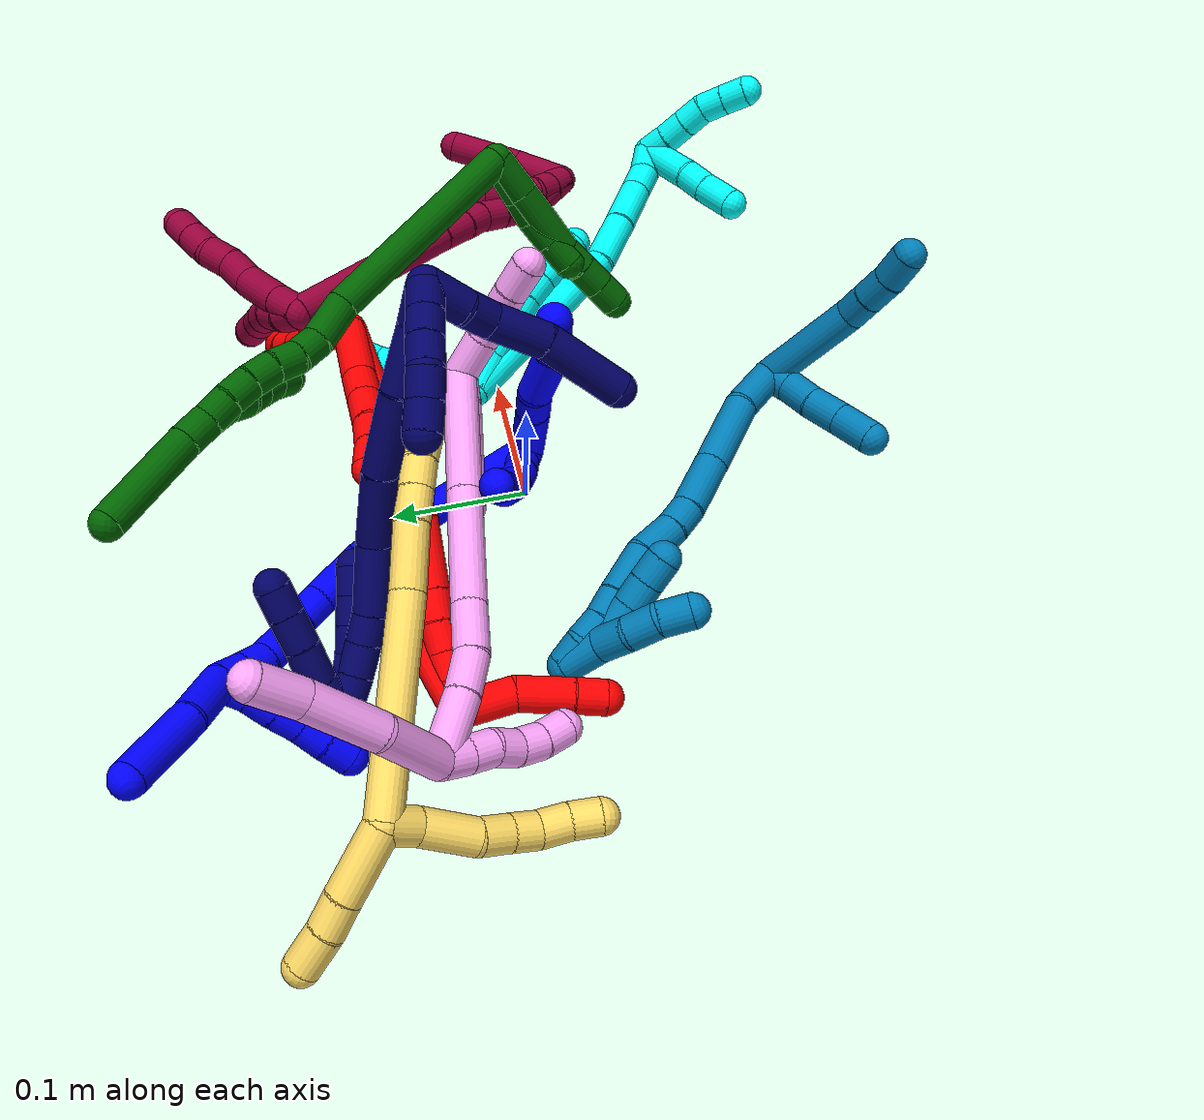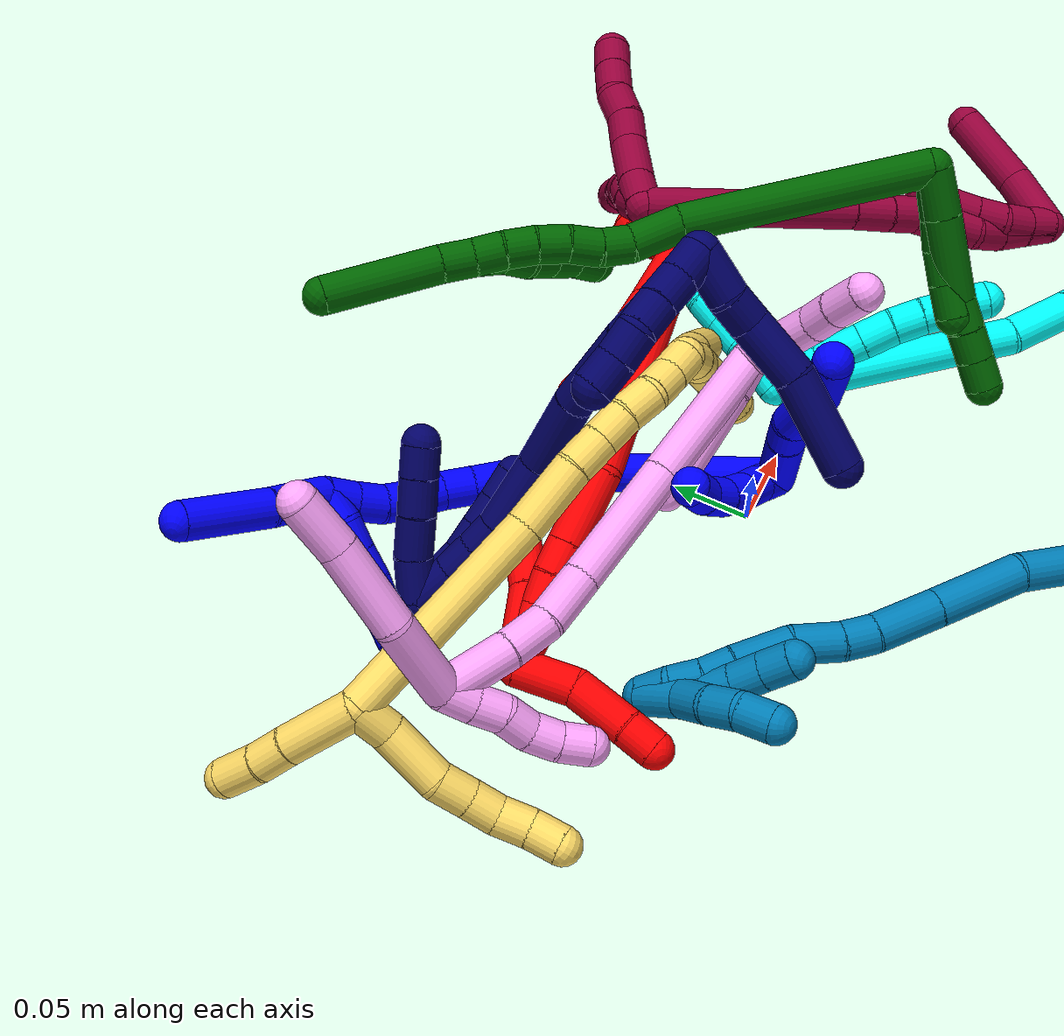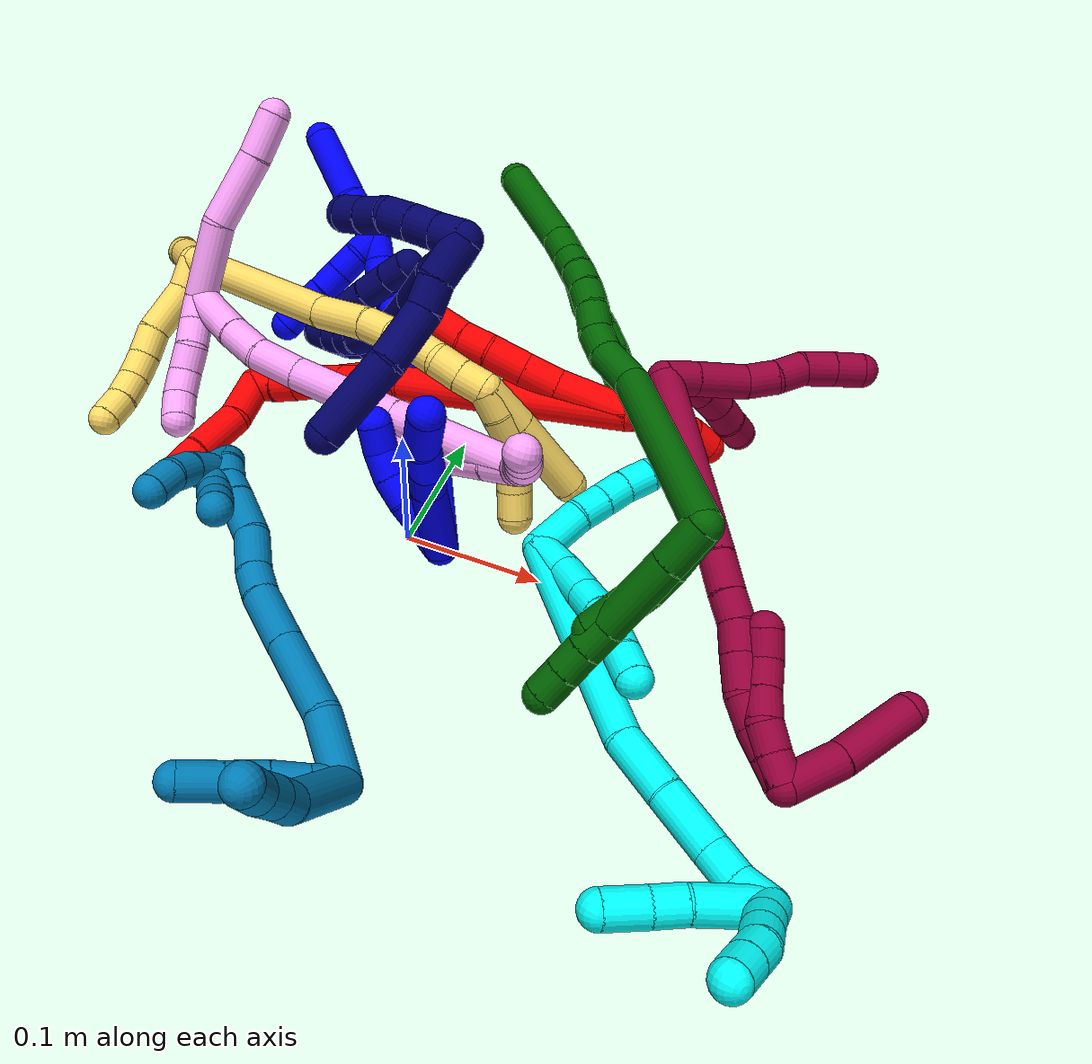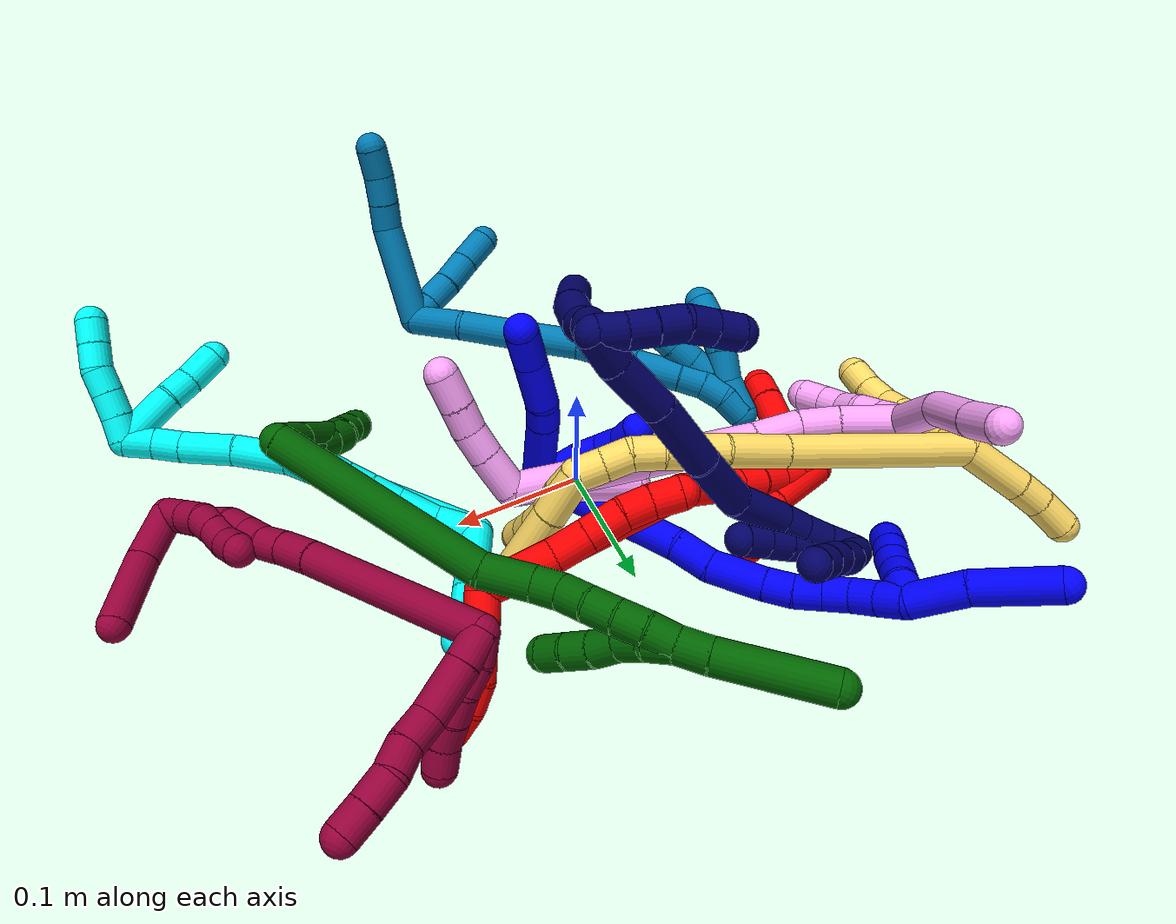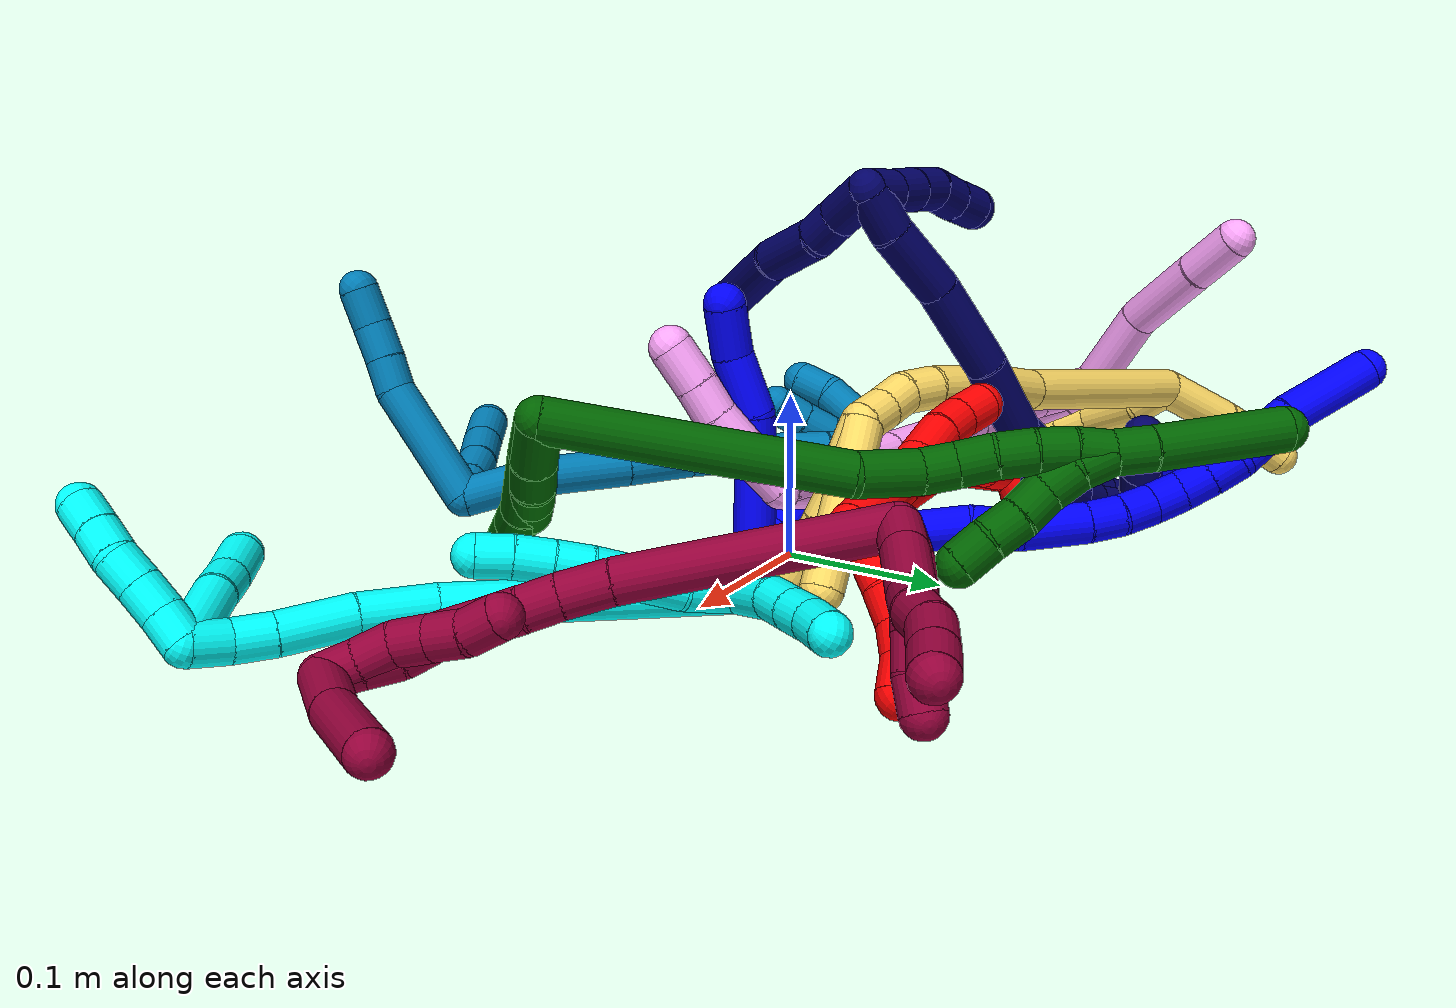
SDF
<sdf version="1.7">
 <world name="default">
  <plugin name="TubeGeneratorPlugin" filename="libtube_generator_plugin.so"/>
  <model name="photoneo_s_sensor">
   <static>1</static>
   <pose>0 0 2 1.57079 1.57079 3.14159</pose>
   <link name="link">
    <inertial><mass>0.1</mass></inertial>
    <sensor name="sensor" type="depth">
     <update_rate>30</update_rate>
     <camera>
      <horizontal_fov>1.22</horizontal_fov>
      <image><width>1920</width><height>1200</height><format>B8G8R8</format></image>
      <clip><near>0.1</near><far>4</far></clip>
      <depth_camera><output>points</output></depth_camera>
     </camera>
     <plugin name="camera_plugin" filename="libgazebo_ros_depth_camera.so">
      <baseline>0.2</baseline>
      <alwaysOn>1</alwaysOn>
      <updateRate>0.0</updateRate>
      <cameraName>camera_ir</cameraName>
      <imageTopicName>/camera/color/image_raw</imageTopicName>
      <cameraInfoTopicName>/camera/color/camera_info</cameraInfoTopicName>
      <depthImageTopicName>/camera/depth/image_raw</depthImageTopicName>
      <depthImageCameraInfoTopicName>/camera/depth/camera_info</depthImageCameraInfoTopicName>
      <pointCloudTopicName>/camera/depth/points</pointCloudTopicName>
      <frameName>fr_optical</frameName>
      <pointCloudCutoff>0.1</pointCloudCutoff>
      <pointCloudCutoffMax>2.0</pointCloudCutoffMax>
      <distortionK1>0</distortionK1>
      <distortionK2>0</distortionK2>
      <distortionK3>0</distortionK3>
      <distortionT1>0</distortionT1>
      <distortionT2>0</distortionT2>
      <CxPrime>0</CxPrime>
      <Cx>0</Cx>
      <Cy>0</Cy>
      <focalLength>0</focalLength>
      <hackBaseline>0</hackBaseline>
     </plugin>
    </sensor>
   </link>
  </model>
  <gravity>0 0 -9.8</gravity>
  <magnetic_field>6e-06 2.3e-05 -4.2e-05</magnetic_field>
  <atmosphere type="adiabatic"/>
  <physics name="default_physics" default="0" type="ode">
   <max_step_size>0.003</max_step_size>
   <real_time_factor>1</real_time_factor>
   <real_time_update_rate>1000</real_time_update_rate>
   <max_contacts>10000</max_contacts>
   <ode>
    <solver>
     <type>quick</type>
     <iters>100</iters>
     <sor>1.3</sor>
     <use_dynamic_moi_rescaling>0</use_dynamic_moi_rescaling>
    </solver>
    <constraints>
     <contact_max_correcting_vel>0</contact_max_correcting_vel>
     <contact_surface_layer>0.001</contact_surface_layer>
     <cfm>0</cfm>
     <erp>0.2</erp>
    </constraints>
   </ode>
  </physics>
  <scene><ambient>0.4 0.4 0.4 1</ambient><background>0.7 0.7 0.7 1</background><shadows>0</shadows></scene>
  <audio><device>default</device></audio>
  <spherical_coordinates>
   <surface_model>EARTH_WGS84</surface_model>
   <latitude_deg>0</latitude_deg>
   <longitude_deg>0</longitude_deg>
   <elevation>0</elevation>
   <heading_deg>0</heading_deg>
  </spherical_coordinates>
  <model name="bin">
   <static>1</static>
   <link name="bottom">
    <collision name="collision-bottom">
     <pose>0 0 -0.01 0 -0 0</pose>
     <geometry><box><size>0.8 0.6 0.02</size></box></geometry>
     <surface>
      <friction><ode><mu>100</mu><mu2>100</mu2></ode></friction>
      <contact><collide_bitmask>65535</collide_bitmask></contact>
     </surface>
    </collision>
   </link>
   <link name="west_wall">
    <collision name="collision-west_wall">
     <pose>-0.41 0 0.1 0 -0 0</pose>
     <geometry><box><size>0.02 0.6 0.2</size></box></geometry>
     <surface>
      <friction><ode><mu>100</mu><mu2>100</mu2></ode></friction>
      <contact><collide_bitmask>65535</collide_bitmask></contact>
     </surface>
    </collision>
   </link>
   <link name="east_wall">
    <collision name="collision-east_wall">
     <pose>0.41 0 0.1 0 -0 0</pose>
     <geometry><box><size>0.02 0.6 0.2</size></box></geometry>
     <surface>
      <friction><ode><mu>100</mu><mu2>100</mu2></ode></friction>
      <contact><collide_bitmask>65535</collide_bitmask></contact>
     </surface>
    </collision>
   </link>
   <link name="south_wall">
    <collision name="collision-south_wall">
     <pose>0 -0.31 0.1 0 -0 0</pose>
     <geometry><box><size>0.8 0.02 0.2</size></box></geometry>
     <surface>
      <friction><ode><mu>100</mu><mu2>100</mu2></ode></friction>
      <contact><collide_bitmask>65535</collide_bitmask></contact>
     </surface>
    </collision>
   </link>
   <link name="north_wall">
    <collision name="collision-north_wall">
     <pose>0 0.31 0.1 0 -0 0</pose>
     <geometry><box><size>0.8 0.02 0.2</size></box></geometry>
     <surface>
      <friction><ode><mu>100</mu><mu2>100</mu2></ode></friction>
      <contact><collide_bitmask>65535</collide_bitmask></contact>
     </surface>
    </collision>
   </link>
  </model>
  <model name="1">
   <static>0</static>
   <link name="1">
    <collision name="collision-cylinder-e_1_2_8">
     <pose>-0.010558 -0.025011 -0.01399 2.0808 -0.352967 -0.590428</pose>
     <geometry><cylinder><radius>0.0125</radius><length>0.061082</length></cylinder></geometry>
     <surface>
      <friction><ode><mu>1.16</mu><mu2>1.16</mu2><slip1>0</slip1><slip2>0</slip2></ode></friction>
      <contact><ode><kp>1e+06</kp><kd>1</kd><max_vel>0</max_vel><min_depth>0.001</min_depth></ode></contact>
     </surface>
    </collision>
    <visual name="visual-cylinder-e_1_2_8">
     <pose>-0.010558 -0.025011 -0.01399 2.0808 -0.352967 -0.590428</pose>
     <geometry><cylinder><radius>0.0125</radius><length>0.061082</length></cylinder></geometry>
     <material><ambient>0 0 1 1</ambient></material>
    </visual>
    <collision name="collision-cylinder-e_2_8_9">
     <pose>-0.024606 -0.058751 -0.031688 1.97246 -0.352715 -0.526142</pose>
     <geometry><cylinder><radius>0.0125</radius><length>0.020211</length></cylinder></geometry>
     <surface>
      <friction><ode><mu>1.16</mu><mu2>1.16</mu2><slip1>0</slip1><slip2>0</slip2></ode></friction>
      <contact><ode><kp>1e+06</kp><kd>1</kd><max_vel>0</max_vel><min_depth>0.001</min_depth></ode></contact>
     </surface>
    </collision>
    <visual name="visual-cylinder-e_2_8_9">
     <pose>-0.024606 -0.058751 -0.031688 1.97246 -0.352715 -0.526142</pose>
     <geometry><cylinder><radius>0.0125</radius><length>0.020211</length></cylinder></geometry>
     <material><ambient>0 0 1 1</ambient></material>
    </visual>
    <collision name="collision-cylinder-e_3_9_10">
     <pose>-0.028955 -0.085187 -0.041303 1.8928 -0.045964 -0.063777</pose>
     <geometry><cylinder><radius>0.0125</radius><length>0.037373</length></cylinder></geometry>
     <surface>
      <friction><ode><mu>1.16</mu><mu2>1.16</mu2><slip1>0</slip1><slip2>0</slip2></ode></friction>
      <contact><ode><kp>1e+06</kp><kd>1</kd><max_vel>0</max_vel><min_depth>0.001</min_depth></ode></contact>
     </surface>
    </collision>
    <visual name="visual-cylinder-e_3_9_10">
     <pose>-0.028955 -0.085187 -0.041303 1.8928 -0.045964 -0.063777</pose>
     <geometry><cylinder><radius>0.0125</radius><length>0.037373</length></cylinder></geometry>
     <material><ambient>0 0 1 1</ambient></material>
    </visual>
    <collision name="collision-cylinder-e_4_10_6">
     <pose>-0.034738 -0.117397 -0.050512 1.7946 -0.319737 -0.398772</pose>
     <geometry><cylinder><radius>0.0125</radius><length>0.031334</length></cylinder></geometry>
     <surface>
      <friction><ode><mu>1.16</mu><mu2>1.16</mu2><slip1>0</slip1><slip2>0</slip2></ode></friction>
      <contact><ode><kp>1e+06</kp><kd>1</kd><max_vel>0</max_vel><min_depth>0.001</min_depth></ode></contact>
     </surface>
    </collision>
    <visual name="visual-cylinder-e_4_10_6">
     <pose>-0.034738 -0.117397 -0.050512 1.7946 -0.319737 -0.398772</pose>
     <geometry><cylinder><radius>0.0125</radius><length>0.031334</length></cylinder></geometry>
     <material><ambient>0 0 1 1</ambient></material>
    </visual>
    <collision name="collision-cylinder-e_1_2_11">
     <pose>-0.005594 0.000137 -0.008288 -3.12511 -0.593708 3.08773</pose>
     <geometry><cylinder><radius>0.0125</radius><length>0.02</length></cylinder></geometry>
     <surface>
      <friction><ode><mu>1.16</mu><mu2>1.16</mu2><slip1>0</slip1><slip2>0</slip2></ode></friction>
      <contact><ode><kp>1e+06</kp><kd>1</kd><max_vel>0</max_vel><min_depth>0.001</min_depth></ode></contact>
     </surface>
    </collision>
    <visual name="visual-cylinder-e_1_2_11">
     <pose>-0.005594 0.000137 -0.008288 -3.12511 -0.593708 3.08773</pose>
     <geometry><cylinder><radius>0.0125</radius><length>0.02</length></cylinder></geometry>
     <material><ambient>0 0 1 1</ambient></material>
    </visual>
    <collision name="collision-cylinder-e_2_11_12">
     <pose>-0.016034 -0.00071 -0.025268 3.02895 -0.505769 -2.71196</pose>
     <geometry><cylinder><radius>0.0125</radius><length>0.02</length></cylinder></geometry>
     <surface>
      <friction><ode><mu>1.16</mu><mu2>1.16</mu2><slip1>0</slip1><slip2>0</slip2></ode></friction>
      <contact><ode><kp>1e+06</kp><kd>1</kd><max_vel>0</max_vel><min_depth>0.001</min_depth></ode></contact>
     </surface>
    </collision>
    <visual name="visual-cylinder-e_2_11_12">
     <pose>-0.016034 -0.00071 -0.025268 3.02895 -0.505769 -2.71196</pose>
     <geometry><cylinder><radius>0.0125</radius><length>0.02</length></cylinder></geometry>
     <material><ambient>0 0 1 1</ambient></material>
    </visual>
    <collision name="collision-cylinder-e_3_12_13">
     <pose>-0.026916 -0.002003 -0.041926 3.10282 -0.648195 -3.02628</pose>
     <geometry><cylinder><radius>0.0125</radius><length>0.02</length></cylinder></geometry>
     <surface>
      <friction><ode><mu>1.16</mu><mu2>1.16</mu2><slip1>0</slip1><slip2>0</slip2></ode></friction>
      <contact><ode><kp>1e+06</kp><kd>1</kd><max_vel>0</max_vel><min_depth>0.001</min_depth></ode></contact>
     </surface>
    </collision>
    <visual name="visual-cylinder-e_3_12_13">
     <pose>-0.026916 -0.002003 -0.041926 3.10282 -0.648195 -3.02628</pose>
     <geometry><cylinder><radius>0.0125</radius><length>0.02</length></cylinder></geometry>
     <material><ambient>0 0 1 1</ambient></material>
    </visual>
    <collision name="collision-cylinder-e_4_13_14">
     <pose>-0.040135 -0.00409 -0.05662 2.88318 -0.801165 -2.54619</pose>
     <geometry><cylinder><radius>0.0125</radius><length>0.02</length></cylinder></geometry>
     <surface>
      <friction><ode><mu>1.16</mu><mu2>1.16</mu2><slip1>0</slip1><slip2>0</slip2></ode></friction>
      <contact><ode><kp>1e+06</kp><kd>1</kd><max_vel>0</max_vel><min_depth>0.001</min_depth></ode></contact>
     </surface>
    </collision>
    <visual name="visual-cylinder-e_4_13_14">
     <pose>-0.040135 -0.00409 -0.05662 2.88318 -0.801165 -2.54619</pose>
     <geometry><cylinder><radius>0.0125</radius><length>0.02</length></cylinder></geometry>
     <material><ambient>0 0 1 1</ambient></material>
    </visual>
    <collision name="collision-cylinder-e_5_14_5">
     <pose>-0.053954 -0.010656 -0.069094 2.44695 -0.72576 -1.61851</pose>
     <geometry><cylinder><radius>0.0125</radius><length>0.02</length></cylinder></geometry>
     <surface>
      <friction><ode><mu>1.16</mu><mu2>1.16</mu2><slip1>0</slip1><slip2>0</slip2></ode></friction>
      <contact><ode><kp>1e+06</kp><kd>1</kd><max_vel>0</max_vel><min_depth>0.001</min_depth></ode></contact>
     </surface>
    </collision>
    <visual name="visual-cylinder-e_5_14_5">
     <pose>-0.053954 -0.010656 -0.069094 2.44695 -0.72576 -1.61851</pose>
     <geometry><cylinder><radius>0.0125</radius><length>0.02</length></cylinder></geometry>
     <material><ambient>0 0 1 1</ambient></material>
    </visual>
    <collision name="collision-cylinder-e_1_2_15">
     <pose>-0.056056 0.024057 -0.019562 -2.25351 -1.06555 1.78385</pose>
     <geometry><cylinder><radius>0.0125</radius><length>0.12812</length></cylinder></geometry>
     <surface>
      <friction><ode><mu>1.16</mu><mu2>1.16</mu2><slip1>0</slip1><slip2>0</slip2></ode></friction>
      <contact><ode><kp>1e+06</kp><kd>1</kd><max_vel>0</max_vel><min_depth>0.001</min_depth></ode></contact>
     </surface>
    </collision>
    <visual name="visual-cylinder-e_1_2_15">
     <pose>-0.056056 0.024057 -0.019562 -2.25351 -1.06555 1.78385</pose>
     <geometry><cylinder><radius>0.0125</radius><length>0.12812</length></cylinder></geometry>
     <material><ambient>0 0 1 1</ambient></material>
    </visual>
    <collision name="collision-cylinder-e_2_15_16">
     <pose>-0.123654 0.055934 -0.042285 -1.95489 -0.939712 1.29073</pose>
     <geometry><cylinder><radius>0.0125</radius><length>0.028592</length></cylinder></geometry>
     <surface>
      <friction><ode><mu>1.16</mu><mu2>1.16</mu2><slip1>0</slip1><slip2>0</slip2></ode></friction>
      <contact><ode><kp>1e+06</kp><kd>1</kd><max_vel>0</max_vel><min_depth>0.001</min_depth></ode></contact>
     </surface>
    </collision>
    <visual name="visual-cylinder-e_2_15_16">
     <pose>-0.123654 0.055934 -0.042285 -1.95489 -0.939712 1.29073</pose>
     <geometry><cylinder><radius>0.0125</radius><length>0.028592</length></cylinder></geometry>
     <material><ambient>0 0 1 1</ambient></material>
    </visual>
    <collision name="collision-cylinder-e_3_16_17">
     <pose>-0.150896 0.073434 -0.054911 -2.34499 -0.859172 1.65568</pose>
     <geometry><cylinder><radius>0.0125</radius><length>0.041462</length></cylinder></geometry>
     <surface>
      <friction><ode><mu>1.16</mu><mu2>1.16</mu2><slip1>0</slip1><slip2>0</slip2></ode></friction>
      <contact><ode><kp>1e+06</kp><kd>1</kd><max_vel>0</max_vel><min_depth>0.001</min_depth></ode></contact>
     </surface>
    </collision>
    <visual name="visual-cylinder-e_3_16_17">
     <pose>-0.150896 0.073434 -0.054911 -2.34499 -0.859172 1.65568</pose>
     <geometry><cylinder><radius>0.0125</radius><length>0.041462</length></cylinder></geometry>
     <material><ambient>0 0 1 1</ambient></material>
    </visual>
    <collision name="collision-cylinder-e_4_17_18">
     <pose>-0.174623 0.087275 -0.069814 -2.4885 -0.864609 1.87524</pose>
     <geometry><cylinder><radius>0.0125</radius><length>0.021101</length></cylinder></geometry>
     <surface>
      <friction><ode><mu>1.16</mu><mu2>1.16</mu2><slip1>0</slip1><slip2>0</slip2></ode></friction>
      <contact><ode><kp>1e+06</kp><kd>1</kd><max_vel>0</max_vel><min_depth>0.001</min_depth></ode></contact>
     </surface>
    </collision>
    <visual name="visual-cylinder-e_4_17_18">
     <pose>-0.174623 0.087275 -0.069814 -2.4885 -0.864609 1.87524</pose>
     <geometry><cylinder><radius>0.0125</radius><length>0.021101</length></cylinder></geometry>
     <material><ambient>0 0 1 1</ambient></material>
    </visual>
    <collision name="collision-cylinder-e_5_18_19">
     <pose>-0.189574 0.094857 -0.082002 -2.67247 -0.740994 2.03858</pose>
     <geometry><cylinder><radius>0.0125</radius><length>0.020516</length></cylinder></geometry>
     <surface>
      <friction><ode><mu>1.16</mu><mu2>1.16</mu2><slip1>0</slip1><slip2>0</slip2></ode></friction>
      <contact><ode><kp>1e+06</kp><kd>1</kd><max_vel>0</max_vel><min_depth>0.001</min_depth></ode></contact>
     </surface>
    </collision>
    <visual name="visual-cylinder-e_5_18_19">
     <pose>-0.189574 0.094857 -0.082002 -2.67247 -0.740994 2.03858</pose>
     <geometry><cylinder><radius>0.0125</radius><length>0.020516</length></cylinder></geometry>
     <material><ambient>0 0 1 1</ambient></material>
    </visual>
    <collision name="collision-cylinder-e_6_19_20">
     <pose>-0.204034 0.100605 -0.095008 -2.78553 -0.845918 2.38102</pose>
     <geometry><cylinder><radius>0.0125</radius><length>0.020132</length></cylinder></geometry>
     <surface>
      <friction><ode><mu>1.16</mu><mu2>1.16</mu2><slip1>0</slip1><slip2>0</slip2></ode></friction>
      <contact><ode><kp>1e+06</kp><kd>1</kd><max_vel>0</max_vel><min_depth>0.001</min_depth></ode></contact>
     </surface>
    </collision>
    <visual name="visual-cylinder-e_6_19_20">
     <pose>-0.204034 0.100605 -0.095008 -2.78553 -0.845918 2.38102</pose>
     <geometry><cylinder><radius>0.0125</radius><length>0.020132</length></cylinder></geometry>
     <material><ambient>0 0 1 1</ambient></material>
    </visual>
    <collision name="collision-cylinder-e_7_20_21">
     <pose>-0.220286 0.103395 -0.106185 -3.04775 -1.05492 2.98072</pose>
     <geometry><cylinder><radius>0.0125</radius><length>0.020042</length></cylinder></geometry>
     <surface>
      <friction><ode><mu>1.16</mu><mu2>1.16</mu2><slip1>0</slip1><slip2>0</slip2></ode></friction>
      <contact><ode><kp>1e+06</kp><kd>1</kd><max_vel>0</max_vel><min_depth>0.001</min_depth></ode></contact>
     </surface>
    </collision>
    <visual name="visual-cylinder-e_7_20_21">
     <pose>-0.220286 0.103395 -0.106185 -3.04775 -1.05492 2.98072</pose>
     <geometry><cylinder><radius>0.0125</radius><length>0.020042</length></cylinder></geometry>
     <material><ambient>0 0 1 1</ambient></material>
    </visual>
    <collision name="collision-cylinder-e_8_21_1">
     <pose>-0.237764 0.10362 -0.115959 3.09257 -1.06448 -3.05838</pose>
     <geometry><cylinder><radius>0.0125</radius><length>0.020036</length></cylinder></geometry>
     <surface>
      <friction><ode><mu>1.16</mu><mu2>1.16</mu2><slip1>0</slip1><slip2>0</slip2></ode></friction>
      <contact><ode><kp>1e+06</kp><kd>1</kd><max_vel>0</max_vel><min_depth>0.001</min_depth></ode></contact>
     </surface>
    </collision>
    <visual name="visual-cylinder-e_8_21_1">
     <pose>-0.237764 0.10362 -0.115959 3.09257 -1.06448 -3.05838</pose>
     <geometry><cylinder><radius>0.0125</radius><length>0.020036</length></cylinder></geometry>
     <material><ambient>0 0 1 1</ambient></material>
    </visual>
    <collision name="collision-cylinder-e_1_1_22">
     <pose>-0.237713 0.105385 -0.125094 -2.70408 1.07835 -2.43007</pose>
     <geometry><cylinder><radius>0.0125</radius><length>0.02</length></cylinder></geometry>
     <surface>
      <friction><ode><mu>1.16</mu><mu2>1.16</mu2><slip1>0</slip1><slip2>0</slip2></ode></friction>
      <contact><ode><kp>1e+06</kp><kd>1</kd><max_vel>0</max_vel><min_depth>0.001</min_depth></ode></contact>
     </surface>
    </collision>
    <visual name="visual-cylinder-e_1_1_22">
     <pose>-0.237713 0.105385 -0.125094 -2.70408 1.07835 -2.43007</pose>
     <geometry><cylinder><radius>0.0125</radius><length>0.02</length></cylinder></geometry>
     <material><ambient>0 0 1 1</ambient></material>
    </visual>
    <collision name="collision-cylinder-e_2_22_23">
     <pose>-0.220748 0.111715 -0.133224 -2.29763 0.953261 -1.71019</pose>
     <geometry><cylinder><radius>0.0125</radius><length>0.02</length></cylinder></geometry>
     <surface>
      <friction><ode><mu>1.16</mu><mu2>1.16</mu2><slip1>0</slip1><slip2>0</slip2></ode></friction>
      <contact><ode><kp>1e+06</kp><kd>1</kd><max_vel>0</max_vel><min_depth>0.001</min_depth></ode></contact>
     </surface>
    </collision>
    <visual name="visual-cylinder-e_2_22_23">
     <pose>-0.220748 0.111715 -0.133224 -2.29763 0.953261 -1.71019</pose>
     <geometry><cylinder><radius>0.0125</radius><length>0.02</length></cylinder></geometry>
     <material><ambient>0 0 1 1</ambient></material>
    </visual>
    <collision name="collision-cylinder-e_3_23_24">
     <pose>-0.204031 0.119733 -0.140681 -2.34493 1.0283 -1.86092</pose>
     <geometry><cylinder><radius>0.0125</radius><length>0.02</length></cylinder></geometry>
     <surface>
      <friction><ode><mu>1.16</mu><mu2>1.16</mu2><slip1>0</slip1><slip2>0</slip2></ode></friction>
      <contact><ode><kp>1e+06</kp><kd>1</kd><max_vel>0</max_vel><min_depth>0.001</min_depth></ode></contact>
     </surface>
    </collision>
    <visual name="visual-cylinder-e_3_23_24">
     <pose>-0.204031 0.119733 -0.140681 -2.34493 1.0283 -1.86092</pose>
     <geometry><cylinder><radius>0.0125</radius><length>0.02</length></cylinder></geometry>
     <material><ambient>0 0 1 1</ambient></material>
    </visual>
    <collision name="collision-cylinder-e_4_24_25">
     <pose>-0.187602 0.127732 -0.148716 -2.36973 0.905106 -1.74937</pose>
     <geometry><cylinder><radius>0.0125</radius><length>0.02</length></cylinder></geometry>
     <surface>
      <friction><ode><mu>1.16</mu><mu2>1.16</mu2><slip1>0</slip1><slip2>0</slip2></ode></friction>
      <contact><ode><kp>1e+06</kp><kd>1</kd><max_vel>0</max_vel><min_depth>0.001</min_depth></ode></contact>
     </surface>
    </collision>
    <visual name="visual-cylinder-e_4_24_25">
     <pose>-0.187602 0.127732 -0.148716 -2.36973 0.905106 -1.74937</pose>
     <geometry><cylinder><radius>0.0125</radius><length>0.02</length></cylinder></geometry>
     <material><ambient>0 0 1 1</ambient></material>
    </visual>
    <collision name="collision-cylinder-e_5_25_4">
     <pose>-0.171449 0.136285 -0.156788 -2.28043 0.976923 -1.71606</pose>
     <geometry><cylinder><radius>0.0125</radius><length>0.02</length></cylinder></geometry>
     <surface>
      <friction><ode><mu>1.16</mu><mu2>1.16</mu2><slip1>0</slip1><slip2>0</slip2></ode></friction>
      <contact><ode><kp>1e+06</kp><kd>1</kd><max_vel>0</max_vel><min_depth>0.001</min_depth></ode></contact>
     </surface>
    </collision>
    <visual name="visual-cylinder-e_5_25_4">
     <pose>-0.171449 0.136285 -0.156788 -2.28043 0.976923 -1.71606</pose>
     <geometry><cylinder><radius>0.0125</radius><length>0.02</length></cylinder></geometry>
     <material><ambient>0 0 1 1</ambient></material>
    </visual>
    <collision name="collision-cylinder-e_1_1_26">
     <pose>-0.259589 0.103577 -0.136925 -3.12949 -0.68122 3.10746</pose>
     <geometry><cylinder><radius>0.0125</radius><length>0.04149</length></cylinder></geometry>
     <surface>
      <friction><ode><mu>1.16</mu><mu2>1.16</mu2><slip1>0</slip1><slip2>0</slip2></ode></friction>
      <contact><ode><kp>1e+06</kp><kd>1</kd><max_vel>0</max_vel><min_depth>0.001</min_depth></ode></contact>
     </surface>
    </collision>
    <visual name="visual-cylinder-e_1_1_26">
     <pose>-0.259589 0.103577 -0.136925 -3.12949 -0.68122 3.10746</pose>
     <geometry><cylinder><radius>0.0125</radius><length>0.04149</length></cylinder></geometry>
     <material><ambient>0 0 1 1</ambient></material>
    </visual>
    <collision name="collision-cylinder-e_2_26_3">
     <pose>-0.293929 0.107722 -0.172726 -2.94354 -0.814324 2.68874</pose>
     <geometry><cylinder><radius>0.0125</radius><length>0.05851</length></cylinder></geometry>
     <surface>
      <friction><ode><mu>1.16</mu><mu2>1.16</mu2><slip1>0</slip1><slip2>0</slip2></ode></friction>
      <contact><ode><kp>1e+06</kp><kd>1</kd><max_vel>0</max_vel><min_depth>0.001</min_depth></ode></contact>
     </surface>
    </collision>
    <visual name="visual-cylinder-e_2_26_3">
     <pose>-0.293929 0.107722 -0.172726 -2.94354 -0.814324 2.68874</pose>
     <geometry><cylinder><radius>0.0125</radius><length>0.05851</length></cylinder></geometry>
     <material><ambient>0 0 1 1</ambient></material>
    </visual>
    <collision name="collision-sphere-3">
     <pose>-0.315205 0.111673 -0.192413 0 -0 0</pose>
     <geometry><sphere><radius>0.0125</radius></sphere></geometry>
     <surface>
      <friction><ode><mu>1.16</mu><mu2>1.16</mu2><slip1>0</slip1><slip2>0</slip2></ode></friction>
      <contact><ode><kp>1e+06</kp><kd>1</kd><max_vel>0</max_vel><min_depth>0.001</min_depth></ode></contact>
     </surface>
    </collision>
    <visual name="visual-sphere-3">
     <pose>-0.315205 0.111673 -0.192413 0 -0 0</pose>
     <geometry><sphere><radius>0.0125</radius></sphere></geometry>
     <material><ambient>0 0 1 1</ambient></material>
    </visual>
    <collision name="collision-sphere-26">
     <pose>-0.272653 0.103772 -0.153039 0 -0 0</pose>
     <geometry><sphere><radius>0.0125</radius></sphere></geometry>
     <surface>
      <friction><ode><mu>1.16</mu><mu2>1.16</mu2><slip1>0</slip1><slip2>0</slip2></ode></friction>
      <contact><ode><kp>1e+06</kp><kd>1</kd><max_vel>0</max_vel><min_depth>0.001</min_depth></ode></contact>
     </surface>
    </collision>
    <visual name="visual-sphere-26">
     <pose>-0.272653 0.103772 -0.153039 0 -0 0</pose>
     <geometry><sphere><radius>0.0125</radius></sphere></geometry>
     <material><ambient>0 0 1 1</ambient></material>
    </visual>
    <collision name="collision-sphere-4">
     <pose>-0.163161 0.14053 -0.160434 0 -0 0</pose>
     <geometry><sphere><radius>0.0125</radius></sphere></geometry>
     <surface>
      <friction><ode><mu>1.16</mu><mu2>1.16</mu2><slip1>0</slip1><slip2>0</slip2></ode></friction>
      <contact><ode><kp>1e+06</kp><kd>1</kd><max_vel>0</max_vel><min_depth>0.001</min_depth></ode></contact>
     </surface>
    </collision>
    <visual name="visual-sphere-4">
     <pose>-0.163161 0.14053 -0.160434 0 -0 0</pose>
     <geometry><sphere><radius>0.0125</radius></sphere></geometry>
     <material><ambient>0 0 1 1</ambient></material>
    </visual>
    <collision name="collision-sphere-25">
     <pose>-0.179737 0.13204 -0.153142 0 -0 0</pose>
     <geometry><sphere><radius>0.0125</radius></sphere></geometry>
     <surface>
      <friction><ode><mu>1.16</mu><mu2>1.16</mu2><slip1>0</slip1><slip2>0</slip2></ode></friction>
      <contact><ode><kp>1e+06</kp><kd>1</kd><max_vel>0</max_vel><min_depth>0.001</min_depth></ode></contact>
     </surface>
    </collision>
    <visual name="visual-sphere-25">
     <pose>-0.179737 0.13204 -0.153142 0 -0 0</pose>
     <geometry><sphere><radius>0.0125</radius></sphere></geometry>
     <material><ambient>0 0 1 1</ambient></material>
    </visual>
    <collision name="collision-sphere-24">
     <pose>-0.195467 0.123425 -0.14429 0 -0 0</pose>
     <geometry><sphere><radius>0.0125</radius></sphere></geometry>
     <surface>
      <friction><ode><mu>1.16</mu><mu2>1.16</mu2><slip1>0</slip1><slip2>0</slip2></ode></friction>
      <contact><ode><kp>1e+06</kp><kd>1</kd><max_vel>0</max_vel><min_depth>0.001</min_depth></ode></contact>
     </surface>
    </collision>
    <visual name="visual-sphere-24">
     <pose>-0.195467 0.123425 -0.14429 0 -0 0</pose>
     <geometry><sphere><radius>0.0125</radius></sphere></geometry>
     <material><ambient>0 0 1 1</ambient></material>
    </visual>
    <collision name="collision-sphere-23">
     <pose>-0.212595 0.116042 -0.137072 0 -0 0</pose>
     <geometry><sphere><radius>0.0125</radius></sphere></geometry>
     <surface>
      <friction><ode><mu>1.16</mu><mu2>1.16</mu2><slip1>0</slip1><slip2>0</slip2></ode></friction>
      <contact><ode><kp>1e+06</kp><kd>1</kd><max_vel>0</max_vel><min_depth>0.001</min_depth></ode></contact>
     </surface>
    </collision>
    <visual name="visual-sphere-23">
     <pose>-0.212595 0.116042 -0.137072 0 -0 0</pose>
     <geometry><sphere><radius>0.0125</radius></sphere></geometry>
     <material><ambient>0 0 1 1</ambient></material>
    </visual>
    <collision name="collision-sphere-22">
     <pose>-0.228901 0.107388 -0.129377 0 -0 0</pose>
     <geometry><sphere><radius>0.0125</radius></sphere></geometry>
     <surface>
      <friction><ode><mu>1.16</mu><mu2>1.16</mu2><slip1>0</slip1><slip2>0</slip2></ode></friction>
      <contact><ode><kp>1e+06</kp><kd>1</kd><max_vel>0</max_vel><min_depth>0.001</min_depth></ode></contact>
     </surface>
    </collision>
    <visual name="visual-sphere-22">
     <pose>-0.228901 0.107388 -0.129377 0 -0 0</pose>
     <geometry><sphere><radius>0.0125</radius></sphere></geometry>
     <material><ambient>0 0 1 1</ambient></material>
    </visual>
    <collision name="collision-sphere-1">
     <pose>-0.246525 0.103382 -0.120812 0 -0 0</pose>
     <geometry><sphere><radius>0.0125</radius></sphere></geometry>
     <surface>
      <friction><ode><mu>1.16</mu><mu2>1.16</mu2><slip1>0</slip1><slip2>0</slip2></ode></friction>
      <contact><ode><kp>1e+06</kp><kd>1</kd><max_vel>0</max_vel><min_depth>0.001</min_depth></ode></contact>
     </surface>
    </collision>
    <visual name="visual-sphere-1">
     <pose>-0.246525 0.103382 -0.120812 0 -0 0</pose>
     <geometry><sphere><radius>0.0125</radius></sphere></geometry>
     <material><ambient>0 0 1 1</ambient></material>
    </visual>
    <collision name="collision-sphere-21">
     <pose>-0.229003 0.103858 -0.111107 0 -0 0</pose>
     <geometry><sphere><radius>0.0125</radius></sphere></geometry>
     <surface>
      <friction><ode><mu>1.16</mu><mu2>1.16</mu2><slip1>0</slip1><slip2>0</slip2></ode></friction>
      <contact><ode><kp>1e+06</kp><kd>1</kd><max_vel>0</max_vel><min_depth>0.001</min_depth></ode></contact>
     </surface>
    </collision>
    <visual name="visual-sphere-21">
     <pose>-0.229003 0.103858 -0.111107 0 -0 0</pose>
     <geometry><sphere><radius>0.0125</radius></sphere></geometry>
     <material><ambient>0 0 1 1</ambient></material>
    </visual>
    <collision name="collision-sphere-11">
     <pose>-0.011189 0.000273 -0.016575 0 -0 0</pose>
     <geometry><sphere><radius>0.0125</radius></sphere></geometry>
     <surface>
      <friction><ode><mu>1.16</mu><mu2>1.16</mu2><slip1>0</slip1><slip2>0</slip2></ode></friction>
      <contact><ode><kp>1e+06</kp><kd>1</kd><max_vel>0</max_vel><min_depth>0.001</min_depth></ode></contact>
     </surface>
    </collision>
    <visual name="visual-sphere-11">
     <pose>-0.011189 0.000273 -0.016575 0 -0 0</pose>
     <geometry><sphere><radius>0.0125</radius></sphere></geometry>
     <material><ambient>0 0 1 1</ambient></material>
    </visual>
    <collision name="collision-sphere-6">
     <pose>-0.039663 -0.131898 -0.053812 0 -0 0</pose>
     <geometry><sphere><radius>0.0125</radius></sphere></geometry>
     <surface>
      <friction><ode><mu>1.16</mu><mu2>1.16</mu2><slip1>0</slip1><slip2>0</slip2></ode></friction>
      <contact><ode><kp>1e+06</kp><kd>1</kd><max_vel>0</max_vel><min_depth>0.001</min_depth></ode></contact>
     </surface>
    </collision>
    <visual name="visual-sphere-6">
     <pose>-0.039663 -0.131898 -0.053812 0 -0 0</pose>
     <geometry><sphere><radius>0.0125</radius></sphere></geometry>
     <material><ambient>0 0 1 1</ambient></material>
    </visual>
    <collision name="collision-sphere-10">
     <pose>-0.029814 -0.102895 -0.047211 0 -0 0</pose>
     <geometry><sphere><radius>0.0125</radius></sphere></geometry>
     <surface>
      <friction><ode><mu>1.16</mu><mu2>1.16</mu2><slip1>0</slip1><slip2>0</slip2></ode></friction>
      <contact><ode><kp>1e+06</kp><kd>1</kd><max_vel>0</max_vel><min_depth>0.001</min_depth></ode></contact>
     </surface>
    </collision>
    <visual name="visual-sphere-10">
     <pose>-0.029814 -0.102895 -0.047211 0 -0 0</pose>
     <geometry><sphere><radius>0.0125</radius></sphere></geometry>
     <material><ambient>0 0 1 1</ambient></material>
    </visual>
    <collision name="collision-sphere-9">
     <pose>-0.028097 -0.06748 -0.035396 0 -0 0</pose>
     <geometry><sphere><radius>0.0125</radius></sphere></geometry>
     <surface>
      <friction><ode><mu>1.16</mu><mu2>1.16</mu2><slip1>0</slip1><slip2>0</slip2></ode></friction>
      <contact><ode><kp>1e+06</kp><kd>1</kd><max_vel>0</max_vel><min_depth>0.001</min_depth></ode></contact>
     </surface>
    </collision>
    <visual name="visual-sphere-9">
     <pose>-0.028097 -0.06748 -0.035396 0 -0 0</pose>
     <geometry><sphere><radius>0.0125</radius></sphere></geometry>
     <material><ambient>0 0 1 1</ambient></material>
    </visual>
    <collision name="collision-sphere-2">
     <geometry><sphere><radius>0.0125</radius></sphere></geometry>
     <surface>
      <friction><ode><mu>1.16</mu><mu2>1.16</mu2><slip1>0</slip1><slip2>0</slip2></ode></friction>
      <contact><ode><kp>1e+06</kp><kd>1</kd><max_vel>0</max_vel><min_depth>0.001</min_depth></ode></contact>
     </surface>
    </collision>
    <visual name="visual-sphere-2">
     <geometry><sphere><radius>0.0125</radius></sphere></geometry>
     <material><ambient>0 0 1 1</ambient></material>
    </visual>
    <collision name="collision-sphere-19">
     <pose>-0.196499 0.098278 -0.088753 0 -0 0</pose>
     <geometry><sphere><radius>0.0125</radius></sphere></geometry>
     <surface>
      <friction><ode><mu>1.16</mu><mu2>1.16</mu2><slip1>0</slip1><slip2>0</slip2></ode></friction>
      <contact><ode><kp>1e+06</kp><kd>1</kd><max_vel>0</max_vel><min_depth>0.001</min_depth></ode></contact>
     </surface>
    </collision>
    <visual name="visual-sphere-19">
     <pose>-0.196499 0.098278 -0.088753 0 -0 0</pose>
     <geometry><sphere><radius>0.0125</radius></sphere></geometry>
     <material><ambient>0 0 1 1</ambient></material>
    </visual>
    <collision name="collision-sphere-8">
     <pose>-0.021115 -0.050022 -0.027981 0 -0 0</pose>
     <geometry><sphere><radius>0.0125</radius></sphere></geometry>
     <surface>
      <friction><ode><mu>1.16</mu><mu2>1.16</mu2><slip1>0</slip1><slip2>0</slip2></ode></friction>
      <contact><ode><kp>1e+06</kp><kd>1</kd><max_vel>0</max_vel><min_depth>0.001</min_depth></ode></contact>
     </surface>
    </collision>
    <visual name="visual-sphere-8">
     <pose>-0.021115 -0.050022 -0.027981 0 -0 0</pose>
     <geometry><sphere><radius>0.0125</radius></sphere></geometry>
     <material><ambient>0 0 1 1</ambient></material>
    </visual>
    <collision name="collision-sphere-12">
     <pose>-0.020878 -0.001694 -0.03396 0 -0 0</pose>
     <geometry><sphere><radius>0.0125</radius></sphere></geometry>
     <surface>
      <friction><ode><mu>1.16</mu><mu2>1.16</mu2><slip1>0</slip1><slip2>0</slip2></ode></friction>
      <contact><ode><kp>1e+06</kp><kd>1</kd><max_vel>0</max_vel><min_depth>0.001</min_depth></ode></contact>
     </surface>
    </collision>
    <visual name="visual-sphere-12">
     <pose>-0.020878 -0.001694 -0.03396 0 -0 0</pose>
     <geometry><sphere><radius>0.0125</radius></sphere></geometry>
     <material><ambient>0 0 1 1</ambient></material>
    </visual>
    <collision name="collision-sphere-13">
     <pose>-0.032953 -0.002312 -0.049892 0 -0 0</pose>
     <geometry><sphere><radius>0.0125</radius></sphere></geometry>
     <surface>
      <friction><ode><mu>1.16</mu><mu2>1.16</mu2><slip1>0</slip1><slip2>0</slip2></ode></friction>
      <contact><ode><kp>1e+06</kp><kd>1</kd><max_vel>0</max_vel><min_depth>0.001</min_depth></ode></contact>
     </surface>
    </collision>
    <visual name="visual-sphere-13">
     <pose>-0.032953 -0.002312 -0.049892 0 -0 0</pose>
     <geometry><sphere><radius>0.0125</radius></sphere></geometry>
     <material><ambient>0 0 1 1</ambient></material>
    </visual>
    <collision name="collision-sphere-14">
     <pose>-0.047317 -0.005868 -0.063347 0 -0 0</pose>
     <geometry><sphere><radius>0.0125</radius></sphere></geometry>
     <surface>
      <friction><ode><mu>1.16</mu><mu2>1.16</mu2><slip1>0</slip1><slip2>0</slip2></ode></friction>
      <contact><ode><kp>1e+06</kp><kd>1</kd><max_vel>0</max_vel><min_depth>0.001</min_depth></ode></contact>
     </surface>
    </collision>
    <visual name="visual-sphere-14">
     <pose>-0.047317 -0.005868 -0.063347 0 -0 0</pose>
     <geometry><sphere><radius>0.0125</radius></sphere></geometry>
     <material><ambient>0 0 1 1</ambient></material>
    </visual>
    <collision name="collision-sphere-5">
     <pose>-0.060591 -0.015444 -0.074841 0 -0 0</pose>
     <geometry><sphere><radius>0.0125</radius></sphere></geometry>
     <surface>
      <friction><ode><mu>1.16</mu><mu2>1.16</mu2><slip1>0</slip1><slip2>0</slip2></ode></friction>
      <contact><ode><kp>1e+06</kp><kd>1</kd><max_vel>0</max_vel><min_depth>0.001</min_depth></ode></contact>
     </surface>
    </collision>
    <visual name="visual-sphere-5">
     <pose>-0.060591 -0.015444 -0.074841 0 -0 0</pose>
     <geometry><sphere><radius>0.0125</radius></sphere></geometry>
     <material><ambient>0 0 1 1</ambient></material>
    </visual>
    <collision name="collision-sphere-15">
     <pose>-0.112112 0.048114 -0.039124 0 -0 0</pose>
     <geometry><sphere><radius>0.0125</radius></sphere></geometry>
     <surface>
      <friction><ode><mu>1.16</mu><mu2>1.16</mu2><slip1>0</slip1><slip2>0</slip2></ode></friction>
      <contact><ode><kp>1e+06</kp><kd>1</kd><max_vel>0</max_vel><min_depth>0.001</min_depth></ode></contact>
     </surface>
    </collision>
    <visual name="visual-sphere-15">
     <pose>-0.112112 0.048114 -0.039124 0 -0 0</pose>
     <geometry><sphere><radius>0.0125</radius></sphere></geometry>
     <material><ambient>0 0 1 1</ambient></material>
    </visual>
    <collision name="collision-sphere-16">
     <pose>-0.135196 0.063754 -0.045445 0 -0 0</pose>
     <geometry><sphere><radius>0.0125</radius></sphere></geometry>
     <surface>
      <friction><ode><mu>1.16</mu><mu2>1.16</mu2><slip1>0</slip1><slip2>0</slip2></ode></friction>
      <contact><ode><kp>1e+06</kp><kd>1</kd><max_vel>0</max_vel><min_depth>0.001</min_depth></ode></contact>
     </surface>
    </collision>
    <visual name="visual-sphere-16">
     <pose>-0.135196 0.063754 -0.045445 0 -0 0</pose>
     <geometry><sphere><radius>0.0125</radius></sphere></geometry>
     <material><ambient>0 0 1 1</ambient></material>
    </visual>
    <collision name="collision-sphere-17">
     <pose>-0.166596 0.083114 -0.064376 0 -0 0</pose>
     <geometry><sphere><radius>0.0125</radius></sphere></geometry>
     <surface>
      <friction><ode><mu>1.16</mu><mu2>1.16</mu2><slip1>0</slip1><slip2>0</slip2></ode></friction>
      <contact><ode><kp>1e+06</kp><kd>1</kd><max_vel>0</max_vel><min_depth>0.001</min_depth></ode></contact>
     </surface>
    </collision>
    <visual name="visual-sphere-17">
     <pose>-0.166596 0.083114 -0.064376 0 -0 0</pose>
     <geometry><sphere><radius>0.0125</radius></sphere></geometry>
     <material><ambient>0 0 1 1</ambient></material>
    </visual>
    <collision name="collision-sphere-18">
     <pose>-0.18265 0.091435 -0.075251 0 -0 0</pose>
     <geometry><sphere><radius>0.0125</radius></sphere></geometry>
     <surface>
      <friction><ode><mu>1.16</mu><mu2>1.16</mu2><slip1>0</slip1><slip2>0</slip2></ode></friction>
      <contact><ode><kp>1e+06</kp><kd>1</kd><max_vel>0</max_vel><min_depth>0.001</min_depth></ode></contact>
     </surface>
    </collision>
    <visual name="visual-sphere-18">
     <pose>-0.18265 0.091435 -0.075251 0 -0 0</pose>
     <geometry><sphere><radius>0.0125</radius></sphere></geometry>
     <material><ambient>0 0 1 1</ambient></material>
    </visual>
    <collision name="collision-sphere-20">
     <pose>-0.211569 0.102931 -0.101264 0 -0 0</pose>
     <geometry><sphere><radius>0.0125</radius></sphere></geometry>
     <surface>
      <friction><ode><mu>1.16</mu><mu2>1.16</mu2><slip1>0</slip1><slip2>0</slip2></ode></friction>
      <contact><ode><kp>1e+06</kp><kd>1</kd><max_vel>0</max_vel><min_depth>0.001</min_depth></ode></contact>
     </surface>
    </collision>
    <visual name="visual-sphere-20">
     <pose>-0.211569 0.102931 -0.101264 0 -0 0</pose>
     <geometry><sphere><radius>0.0125</radius></sphere></geometry>
     <material><ambient>0 0 1 1</ambient></material>
    </visual>
    <inertial>
     <pose>-0.123198 0.040508 -0.072046 0 -0 0</pose>
     <mass>0.75</mass>
     <inertia>
      <ixx>3.8e-05</ixx>
      <ixy>0</ixy>
      <ixz>0</ixz>
      <iyy>0.000267</iyy>
      <iyz>0</iyz>
      <izz>0.000119</izz>
     </inertia>
    </inertial>
   </link>
   <pose>0.02937 -0.007349 0.011412 -1.96187 0.399153 -1.51611</pose>
  </model>
  <model name="2">
   <static>0</static>
   <link name="2">
    <collision name="collision-cylinder-e_1_2_8">
     <pose>-0.016824 -0.011611 0.016488 0.613524 -0.695293 -0.228565</pose>
     <geometry><cylinder><radius>0.0125</radius><length>0.052525</length></cylinder></geometry>
     <surface>
      <friction><ode><mu>1.16</mu><mu2>1.16</mu2><slip1>0</slip1><slip2>0</slip2></ode></friction>
      <contact><ode><kp>1e+06</kp><kd>1</kd><max_vel>0</max_vel><min_depth>0.001</min_depth></ode></contact>
     </surface>
    </collision>
    <visual name="visual-cylinder-e_1_2_8">
     <pose>-0.016824 -0.011611 0.016488 0.613524 -0.695293 -0.228565</pose>
     <geometry><cylinder><radius>0.0125</radius><length>0.052525</length></cylinder></geometry>
     <material><ambient>1 0 0 1</ambient></material>
    </visual>
    <collision name="collision-cylinder-e_2_8_9">
     <pose>-0.042197 -0.027312 0.042206 0.41721 -0.702673 -0.154873</pose>
     <geometry><cylinder><radius>0.0125</radius><length>0.026457</length></cylinder></geometry>
     <surface>
      <friction><ode><mu>1.16</mu><mu2>1.16</mu2><slip1>0</slip1><slip2>0</slip2></ode></friction>
      <contact><ode><kp>1e+06</kp><kd>1</kd><max_vel>0</max_vel><min_depth>0.001</min_depth></ode></contact>
     </surface>
    </collision>
    <visual name="visual-cylinder-e_2_8_9">
     <pose>-0.042197 -0.027312 0.042206 0.41721 -0.702673 -0.154873</pose>
     <geometry><cylinder><radius>0.0125</radius><length>0.026457</length></cylinder></geometry>
     <material><ambient>1 0 0 1</ambient></material>
    </visual>
    <collision name="collision-cylinder-e_3_9_10">
     <pose>-0.059893 -0.035481 0.061266 0.393206 -0.709922 -0.147386</pose>
     <geometry><cylinder><radius>0.0125</radius><length>0.028067</length></cylinder></geometry>
     <surface>
      <friction><ode><mu>1.16</mu><mu2>1.16</mu2><slip1>0</slip1><slip2>0</slip2></ode></friction>
      <contact><ode><kp>1e+06</kp><kd>1</kd><max_vel>0</max_vel><min_depth>0.001</min_depth></ode></contact>
     </surface>
    </collision>
    <visual name="visual-cylinder-e_3_9_10">
     <pose>-0.059893 -0.035481 0.061266 0.393206 -0.709922 -0.147386</pose>
     <geometry><cylinder><radius>0.0125</radius><length>0.028067</length></cylinder></geometry>
     <material><ambient>1 0 0 1</ambient></material>
    </visual>
    <collision name="collision-cylinder-e_4_10_11">
     <pose>-0.076432 -0.043883 0.077353 0.604814 -0.771228 -0.251944</pose>
     <geometry><cylinder><radius>0.0125</radius><length>0.021211</length></cylinder></geometry>
     <surface>
      <friction><ode><mu>1.16</mu><mu2>1.16</mu2><slip1>0</slip1><slip2>0</slip2></ode></friction>
      <contact><ode><kp>1e+06</kp><kd>1</kd><max_vel>0</max_vel><min_depth>0.001</min_depth></ode></contact>
     </surface>
    </collision>
    <visual name="visual-cylinder-e_4_10_11">
     <pose>-0.076432 -0.043883 0.077353 0.604814 -0.771228 -0.251944</pose>
     <geometry><cylinder><radius>0.0125</radius><length>0.021211</length></cylinder></geometry>
     <material><ambient>1 0 0 1</ambient></material>
    </visual>
    <collision name="collision-cylinder-e_5_11_6">
     <pose>-0.092471 -0.052153 0.088883 0.642361 -0.91973 -0.326625</pose>
     <geometry><cylinder><radius>0.0125</radius><length>0.021739</length></cylinder></geometry>
     <surface>
      <friction><ode><mu>1.16</mu><mu2>1.16</mu2><slip1>0</slip1><slip2>0</slip2></ode></friction>
      <contact><ode><kp>1e+06</kp><kd>1</kd><max_vel>0</max_vel><min_depth>0.001</min_depth></ode></contact>
     </surface>
    </collision>
    <visual name="visual-cylinder-e_5_11_6">
     <pose>-0.092471 -0.052153 0.088883 0.642361 -0.91973 -0.326625</pose>
     <geometry><cylinder><radius>0.0125</radius><length>0.021739</length></cylinder></geometry>
     <material><ambient>1 0 0 1</ambient></material>
    </visual>
    <collision name="collision-cylinder-e_1_2_12">
     <pose>-0.001869 -0.000963 -0.009776 3.04336 -0.187986 -2.18029</pose>
     <geometry><cylinder><radius>0.0125</radius><length>0.02</length></cylinder></geometry>
     <surface>
      <friction><ode><mu>1.16</mu><mu2>1.16</mu2><slip1>0</slip1><slip2>0</slip2></ode></friction>
      <contact><ode><kp>1e+06</kp><kd>1</kd><max_vel>0</max_vel><min_depth>0.001</min_depth></ode></contact>
     </surface>
    </collision>
    <visual name="visual-cylinder-e_1_2_12">
     <pose>-0.001869 -0.000963 -0.009776 3.04336 -0.187986 -2.18029</pose>
     <geometry><cylinder><radius>0.0125</radius><length>0.02</length></cylinder></geometry>
     <material><ambient>1 0 0 1</ambient></material>
    </visual>
    <collision name="collision-cylinder-e_2_12_13">
     <pose>-0.004227 -0.003866 -0.029351 2.94618 -0.048956 -0.489536</pose>
     <geometry><cylinder><radius>0.0125</radius><length>0.02</length></cylinder></geometry>
     <surface>
      <friction><ode><mu>1.16</mu><mu2>1.16</mu2><slip1>0</slip1><slip2>0</slip2></ode></friction>
      <contact><ode><kp>1e+06</kp><kd>1</kd><max_vel>0</max_vel><min_depth>0.001</min_depth></ode></contact>
     </surface>
    </collision>
    <visual name="visual-cylinder-e_2_12_13">
     <pose>-0.004227 -0.003866 -0.029351 2.94618 -0.048956 -0.489536</pose>
     <geometry><cylinder><radius>0.0125</radius><length>0.02</length></cylinder></geometry>
     <material><ambient>1 0 0 1</ambient></material>
    </visual>
    <collision name="collision-cylinder-e_3_13_14">
     <pose>-0.004924 -0.009109 -0.048585 2.80492 -0.020751 -0.121959</pose>
     <geometry><cylinder><radius>0.0125</radius><length>0.02</length></cylinder></geometry>
     <surface>
      <friction><ode><mu>1.16</mu><mu2>1.16</mu2><slip1>0</slip1><slip2>0</slip2></ode></friction>
      <contact><ode><kp>1e+06</kp><kd>1</kd><max_vel>0</max_vel><min_depth>0.001</min_depth></ode></contact>
     </surface>
    </collision>
    <visual name="visual-cylinder-e_3_13_14">
     <pose>-0.004924 -0.009109 -0.048585 2.80492 -0.020751 -0.121959</pose>
     <geometry><cylinder><radius>0.0125</radius><length>0.02</length></cylinder></geometry>
     <material><ambient>1 0 0 1</ambient></material>
    </visual>
    <collision name="collision-cylinder-e_4_14_15">
     <pose>-0.003092 -0.013571 -0.067743 3.02289 0.205402 2.09557</pose>
     <geometry><cylinder><radius>0.0125</radius><length>0.02</length></cylinder></geometry>
     <surface>
      <friction><ode><mu>1.16</mu><mu2>1.16</mu2><slip1>0</slip1><slip2>0</slip2></ode></friction>
      <contact><ode><kp>1e+06</kp><kd>1</kd><max_vel>0</max_vel><min_depth>0.001</min_depth></ode></contact>
     </surface>
    </collision>
    <visual name="visual-cylinder-e_4_14_15">
     <pose>-0.003092 -0.013571 -0.067743 3.02289 0.205402 2.09557</pose>
     <geometry><cylinder><radius>0.0125</radius><length>0.02</length></cylinder></geometry>
     <material><ambient>1 0 0 1</ambient></material>
    </visual>
    <collision name="collision-cylinder-e_5_15_5">
     <pose>0.003521 -0.015949 -0.086273 3.00409 0.474925 2.58721</pose>
     <geometry><cylinder><radius>0.0125</radius><length>0.02</length></cylinder></geometry>
     <surface>
      <friction><ode><mu>1.16</mu><mu2>1.16</mu2><slip1>0</slip1><slip2>0</slip2></ode></friction>
      <contact><ode><kp>1e+06</kp><kd>1</kd><max_vel>0</max_vel><min_depth>0.001</min_depth></ode></contact>
     </surface>
    </collision>
    <visual name="visual-cylinder-e_5_15_5">
     <pose>0.003521 -0.015949 -0.086273 3.00409 0.474925 2.58721</pose>
     <geometry><cylinder><radius>0.0125</radius><length>0.02</length></cylinder></geometry>
     <material><ambient>1 0 0 1</ambient></material>
    </visual>
    <collision name="collision-cylinder-e_1_2_16">
     <pose>-0.040256 -0.052582 0.051061 0.800075 -0.502252 -0.216106</pose>
     <geometry><cylinder><radius>0.0125</radius><length>0.167244</length></cylinder></geometry>
     <surface>
      <friction><ode><mu>1.16</mu><mu2>1.16</mu2><slip1>0</slip1><slip2>0</slip2></ode></friction>
      <contact><ode><kp>1e+06</kp><kd>1</kd><max_vel>0</max_vel><min_depth>0.001</min_depth></ode></contact>
     </surface>
    </collision>
    <visual name="visual-cylinder-e_1_2_16">
     <pose>-0.040256 -0.052582 0.051061 0.800075 -0.502252 -0.216106</pose>
     <geometry><cylinder><radius>0.0125</radius><length>0.167244</length></cylinder></geometry>
     <material><ambient>1 0 0 1</ambient></material>
    </visual>
    <collision name="collision-cylinder-e_2_16_17">
     <pose>-0.092924 -0.125341 0.110535 1.17576 -0.516423 -0.348479</pose>
     <geometry><cylinder><radius>0.0125</radius><length>0.050275</length></cylinder></geometry>
     <surface>
      <friction><ode><mu>1.16</mu><mu2>1.16</mu2><slip1>0</slip1><slip2>0</slip2></ode></friction>
      <contact><ode><kp>1e+06</kp><kd>1</kd><max_vel>0</max_vel><min_depth>0.001</min_depth></ode></contact>
     </surface>
    </collision>
    <visual name="visual-cylinder-e_2_16_17">
     <pose>-0.092924 -0.125341 0.110535 1.17576 -0.516423 -0.348479</pose>
     <geometry><cylinder><radius>0.0125</radius><length>0.050275</length></cylinder></geometry>
     <material><ambient>1 0 0 1</ambient></material>
    </visual>
    <collision name="collision-cylinder-e_3_17_18">
     <pose>-0.110626 -0.154119 0.122564 1.17278 -0.515711 -0.346888</pose>
     <geometry><cylinder><radius>0.0125</radius><length>0.021453</length></cylinder></geometry>
     <surface>
      <friction><ode><mu>1.16</mu><mu2>1.16</mu2><slip1>0</slip1><slip2>0</slip2></ode></friction>
      <contact><ode><kp>1e+06</kp><kd>1</kd><max_vel>0</max_vel><min_depth>0.001</min_depth></ode></contact>
     </surface>
    </collision>
    <visual name="visual-cylinder-e_3_17_18">
     <pose>-0.110626 -0.154119 0.122564 1.17278 -0.515711 -0.346888</pose>
     <geometry><cylinder><radius>0.0125</radius><length>0.021453</length></cylinder></geometry>
     <material><ambient>1 0 0 1</ambient></material>
    </visual>
    <collision name="collision-cylinder-e_4_18_19">
     <pose>-0.119934 -0.171642 0.130001 1.16619 -0.392575 -0.26083</pose>
     <geometry><cylinder><radius>0.0125</radius><length>0.021007</length></cylinder></geometry>
     <surface>
      <friction><ode><mu>1.16</mu><mu2>1.16</mu2><slip1>0</slip1><slip2>0</slip2></ode></friction>
      <contact><ode><kp>1e+06</kp><kd>1</kd><max_vel>0</max_vel><min_depth>0.001</min_depth></ode></contact>
     </surface>
    </collision>
    <visual name="visual-cylinder-e_4_18_19">
     <pose>-0.119934 -0.171642 0.130001 1.16619 -0.392575 -0.26083</pose>
     <geometry><cylinder><radius>0.0125</radius><length>0.021007</length></cylinder></geometry>
     <material><ambient>1 0 0 1</ambient></material>
    </visual>
    <collision name="collision-cylinder-e_5_19_20">
     <pose>-0.127938 -0.188668 0.138117 1.08342 -0.409852 -0.248851</pose>
     <geometry><cylinder><radius>0.0125</radius><length>0.020002</length></cylinder></geometry>
     <surface>
      <friction><ode><mu>1.16</mu><mu2>1.16</mu2><slip1>0</slip1><slip2>0</slip2></ode></friction>
      <contact><ode><kp>1e+06</kp><kd>1</kd><max_vel>0</max_vel><min_depth>0.001</min_depth></ode></contact>
     </surface>
    </collision>
    <visual name="visual-cylinder-e_5_19_20">
     <pose>-0.127938 -0.188668 0.138117 1.08342 -0.409852 -0.248851</pose>
     <geometry><cylinder><radius>0.0125</radius><length>0.020002</length></cylinder></geometry>
     <material><ambient>1 0 0 1</ambient></material>
    </visual>
    <collision name="collision-cylinder-e_6_20_1">
     <pose>-0.137035 -0.204337 0.146514 1.07406 -0.536029 -0.324151</pose>
     <geometry><cylinder><radius>0.0125</radius><length>0.020018</length></cylinder></geometry>
     <surface>
      <friction><ode><mu>1.16</mu><mu2>1.16</mu2><slip1>0</slip1><slip2>0</slip2></ode></friction>
      <contact><ode><kp>1e+06</kp><kd>1</kd><max_vel>0</max_vel><min_depth>0.001</min_depth></ode></contact>
     </surface>
    </collision>
    <visual name="visual-cylinder-e_6_20_1">
     <pose>-0.137035 -0.204337 0.146514 1.07406 -0.536029 -0.324151</pose>
     <geometry><cylinder><radius>0.0125</radius><length>0.020018</length></cylinder></geometry>
     <material><ambient>1 0 0 1</ambient></material>
    </visual>
    <collision name="collision-cylinder-e_1_1_21">
     <pose>-0.133679 -0.194723 0.133266 -2.36108 0.333831 -0.777476</pose>
     <geometry><cylinder><radius>0.0125</radius><length>0.051684</length></cylinder></geometry>
     <surface>
      <friction><ode><mu>1.16</mu><mu2>1.16</mu2><slip1>0</slip1><slip2>0</slip2></ode></friction>
      <contact><ode><kp>1e+06</kp><kd>1</kd><max_vel>0</max_vel><min_depth>0.001</min_depth></ode></contact>
     </surface>
    </collision>
    <visual name="visual-cylinder-e_1_1_21">
     <pose>-0.133679 -0.194723 0.133266 -2.36108 0.333831 -0.777476</pose>
     <geometry><cylinder><radius>0.0125</radius><length>0.051684</length></cylinder></geometry>
     <material><ambient>1 0 0 1</ambient></material>
    </visual>
    <collision name="collision-cylinder-e_2_21_4">
     <pose>-0.123001 -0.165067 0.095349 -2.59636 0.091635 -0.325097</pose>
     <geometry><cylinder><radius>0.0125</radius><length>0.048316</length></cylinder></geometry>
     <surface>
      <friction><ode><mu>1.16</mu><mu2>1.16</mu2><slip1>0</slip1><slip2>0</slip2></ode></friction>
      <contact><ode><kp>1e+06</kp><kd>1</kd><max_vel>0</max_vel><min_depth>0.001</min_depth></ode></contact>
     </surface>
    </collision>
    <visual name="visual-cylinder-e_2_21_4">
     <pose>-0.123001 -0.165067 0.095349 -2.59636 0.091635 -0.325097</pose>
     <geometry><cylinder><radius>0.0125</radius><length>0.048316</length></cylinder></geometry>
     <material><ambient>1 0 0 1</ambient></material>
    </visual>
    <collision name="collision-cylinder-e_1_1_22">
     <pose>-0.12646 -0.213807 0.162098 0.164392 0.932384 0.082859</pose>
     <geometry><cylinder><radius>0.0125</radius><length>0.039068</length></cylinder></geometry>
     <surface>
      <friction><ode><mu>1.16</mu><mu2>1.16</mu2><slip1>0</slip1><slip2>0</slip2></ode></friction>
      <contact><ode><kp>1e+06</kp><kd>1</kd><max_vel>0</max_vel><min_depth>0.001</min_depth></ode></contact>
     </surface>
    </collision>
    <visual name="visual-cylinder-e_1_1_22">
     <pose>-0.12646 -0.213807 0.162098 0.164392 0.932384 0.082859</pose>
     <geometry><cylinder><radius>0.0125</radius><length>0.039068</length></cylinder></geometry>
     <material><ambient>1 0 0 1</ambient></material>
    </visual>
    <collision name="collision-cylinder-e_2_22_23">
     <pose>-0.099049 -0.221734 0.188467 0.384406 0.630706 0.126806</pose>
     <geometry><cylinder><radius>0.0125</radius><length>0.039762</length></cylinder></geometry>
     <surface>
      <friction><ode><mu>1.16</mu><mu2>1.16</mu2><slip1>0</slip1><slip2>0</slip2></ode></friction>
      <contact><ode><kp>1e+06</kp><kd>1</kd><max_vel>0</max_vel><min_depth>0.001</min_depth></ode></contact>
     </surface>
    </collision>
    <visual name="visual-cylinder-e_2_22_23">
     <pose>-0.099049 -0.221734 0.188467 0.384406 0.630706 0.126806</pose>
     <geometry><cylinder><radius>0.0125</radius><length>0.039762</length></cylinder></geometry>
     <material><ambient>1 0 0 1</ambient></material>
    </visual>
    <collision name="collision-cylinder-e_3_23_3">
     <pose>-0.08073 -0.231692 0.210635 0.495594 0.672547 0.176411</pose>
     <geometry><cylinder><radius>0.0125</radius><length>0.021169</length></cylinder></geometry>
     <surface>
      <friction><ode><mu>1.16</mu><mu2>1.16</mu2><slip1>0</slip1><slip2>0</slip2></ode></friction>
      <contact><ode><kp>1e+06</kp><kd>1</kd><max_vel>0</max_vel><min_depth>0.001</min_depth></ode></contact>
     </surface>
    </collision>
    <visual name="visual-cylinder-e_3_23_3">
     <pose>-0.08073 -0.231692 0.210635 0.495594 0.672547 0.176411</pose>
     <geometry><cylinder><radius>0.0125</radius><length>0.021169</length></cylinder></geometry>
     <material><ambient>1 0 0 1</ambient></material>
    </visual>
    <collision name="collision-sphere-3">
     <pose>-0.074136 -0.23563 0.217918 0 -0 0</pose>
     <geometry><sphere><radius>0.0125</radius></sphere></geometry>
     <surface>
      <friction><ode><mu>1.16</mu><mu2>1.16</mu2><slip1>0</slip1><slip2>0</slip2></ode></friction>
      <contact><ode><kp>1e+06</kp><kd>1</kd><max_vel>0</max_vel><min_depth>0.001</min_depth></ode></contact>
     </surface>
    </collision>
    <visual name="visual-sphere-3">
     <pose>-0.074136 -0.23563 0.217918 0 -0 0</pose>
     <geometry><sphere><radius>0.0125</radius></sphere></geometry>
     <material><ambient>1 0 0 1</ambient></material>
    </visual>
    <collision name="collision-sphere-23">
     <pose>-0.087324 -0.227755 0.203351 0 -0 0</pose>
     <geometry><sphere><radius>0.0125</radius></sphere></geometry>
     <surface>
      <friction><ode><mu>1.16</mu><mu2>1.16</mu2><slip1>0</slip1><slip2>0</slip2></ode></friction>
      <contact><ode><kp>1e+06</kp><kd>1</kd><max_vel>0</max_vel><min_depth>0.001</min_depth></ode></contact>
     </surface>
    </collision>
    <visual name="visual-sphere-23">
     <pose>-0.087324 -0.227755 0.203351 0 -0 0</pose>
     <geometry><sphere><radius>0.0125</radius></sphere></geometry>
     <material><ambient>1 0 0 1</ambient></material>
    </visual>
    <collision name="collision-sphere-22">
     <pose>-0.110773 -0.215712 0.173582 0 -0 0</pose>
     <geometry><sphere><radius>0.0125</radius></sphere></geometry>
     <surface>
      <friction><ode><mu>1.16</mu><mu2>1.16</mu2><slip1>0</slip1><slip2>0</slip2></ode></friction>
      <contact><ode><kp>1e+06</kp><kd>1</kd><max_vel>0</max_vel><min_depth>0.001</min_depth></ode></contact>
     </surface>
    </collision>
    <visual name="visual-sphere-22">
     <pose>-0.110773 -0.215712 0.173582 0 -0 0</pose>
     <geometry><sphere><radius>0.0125</radius></sphere></geometry>
     <material><ambient>1 0 0 1</ambient></material>
    </visual>
    <collision name="collision-sphere-4">
     <pose>-0.12079 -0.15259 0.07478 0 -0 0</pose>
     <geometry><sphere><radius>0.0125</radius></sphere></geometry>
     <surface>
      <friction><ode><mu>1.16</mu><mu2>1.16</mu2><slip1>0</slip1><slip2>0</slip2></ode></friction>
      <contact><ode><kp>1e+06</kp><kd>1</kd><max_vel>0</max_vel><min_depth>0.001</min_depth></ode></contact>
     </surface>
    </collision>
    <visual name="visual-sphere-4">
     <pose>-0.12079 -0.15259 0.07478 0 -0 0</pose>
     <geometry><sphere><radius>0.0125</radius></sphere></geometry>
     <material><ambient>1 0 0 1</ambient></material>
    </visual>
    <collision name="collision-sphere-21">
     <pose>-0.125211 -0.177543 0.115917 0 -0 0</pose>
     <geometry><sphere><radius>0.0125</radius></sphere></geometry>
     <surface>
      <friction><ode><mu>1.16</mu><mu2>1.16</mu2><slip1>0</slip1><slip2>0</slip2></ode></friction>
      <contact><ode><kp>1e+06</kp><kd>1</kd><max_vel>0</max_vel><min_depth>0.001</min_depth></ode></contact>
     </surface>
    </collision>
    <visual name="visual-sphere-21">
     <pose>-0.125211 -0.177543 0.115917 0 -0 0</pose>
     <geometry><sphere><radius>0.0125</radius></sphere></geometry>
     <material><ambient>1 0 0 1</ambient></material>
    </visual>
    <collision name="collision-sphere-1">
     <pose>-0.142146 -0.211902 0.150614 0 -0 0</pose>
     <geometry><sphere><radius>0.0125</radius></sphere></geometry>
     <surface>
      <friction><ode><mu>1.16</mu><mu2>1.16</mu2><slip1>0</slip1><slip2>0</slip2></ode></friction>
      <contact><ode><kp>1e+06</kp><kd>1</kd><max_vel>0</max_vel><min_depth>0.001</min_depth></ode></contact>
     </surface>
    </collision>
    <visual name="visual-sphere-1">
     <pose>-0.142146 -0.211902 0.150614 0 -0 0</pose>
     <geometry><sphere><radius>0.0125</radius></sphere></geometry>
     <material><ambient>1 0 0 1</ambient></material>
    </visual>
    <collision name="collision-sphere-6">
     <pose>-0.101117 -0.0561 0.094157 0 -0 0</pose>
     <geometry><sphere><radius>0.0125</radius></sphere></geometry>
     <surface>
      <friction><ode><mu>1.16</mu><mu2>1.16</mu2><slip1>0</slip1><slip2>0</slip2></ode></friction>
      <contact><ode><kp>1e+06</kp><kd>1</kd><max_vel>0</max_vel><min_depth>0.001</min_depth></ode></contact>
     </surface>
    </collision>
    <visual name="visual-sphere-6">
     <pose>-0.101117 -0.0561 0.094157 0 -0 0</pose>
     <geometry><sphere><radius>0.0125</radius></sphere></geometry>
     <material><ambient>1 0 0 1</ambient></material>
    </visual>
    <collision name="collision-sphere-11">
     <pose>-0.083824 -0.048207 0.083608 0 -0 0</pose>
     <geometry><sphere><radius>0.0125</radius></sphere></geometry>
     <surface>
      <friction><ode><mu>1.16</mu><mu2>1.16</mu2><slip1>0</slip1><slip2>0</slip2></ode></friction>
      <contact><ode><kp>1e+06</kp><kd>1</kd><max_vel>0</max_vel><min_depth>0.001</min_depth></ode></contact>
     </surface>
    </collision>
    <visual name="visual-sphere-11">
     <pose>-0.083824 -0.048207 0.083608 0 -0 0</pose>
     <geometry><sphere><radius>0.0125</radius></sphere></geometry>
     <material><ambient>1 0 0 1</ambient></material>
    </visual>
    <collision name="collision-sphere-10">
     <pose>-0.06904 -0.039559 0.071097 0 -0 0</pose>
     <geometry><sphere><radius>0.0125</radius></sphere></geometry>
     <surface>
      <friction><ode><mu>1.16</mu><mu2>1.16</mu2><slip1>0</slip1><slip2>0</slip2></ode></friction>
      <contact><ode><kp>1e+06</kp><kd>1</kd><max_vel>0</max_vel><min_depth>0.001</min_depth></ode></contact>
     </surface>
    </collision>
    <visual name="visual-sphere-10">
     <pose>-0.06904 -0.039559 0.071097 0 -0 0</pose>
     <geometry><sphere><radius>0.0125</radius></sphere></geometry>
     <material><ambient>1 0 0 1</ambient></material>
    </visual>
    <collision name="collision-sphere-9">
     <pose>-0.050746 -0.031403 0.051435 0 -0 0</pose>
     <geometry><sphere><radius>0.0125</radius></sphere></geometry>
     <surface>
      <friction><ode><mu>1.16</mu><mu2>1.16</mu2><slip1>0</slip1><slip2>0</slip2></ode></friction>
      <contact><ode><kp>1e+06</kp><kd>1</kd><max_vel>0</max_vel><min_depth>0.001</min_depth></ode></contact>
     </surface>
    </collision>
    <visual name="visual-sphere-9">
     <pose>-0.050746 -0.031403 0.051435 0 -0 0</pose>
     <geometry><sphere><radius>0.0125</radius></sphere></geometry>
     <material><ambient>1 0 0 1</ambient></material>
    </visual>
    <collision name="collision-sphere-2">
     <geometry><sphere><radius>0.0125</radius></sphere></geometry>
     <surface>
      <friction><ode><mu>1.16</mu><mu2>1.16</mu2><slip1>0</slip1><slip2>0</slip2></ode></friction>
      <contact><ode><kp>1e+06</kp><kd>1</kd><max_vel>0</max_vel><min_depth>0.001</min_depth></ode></contact>
     </surface>
    </collision>
    <visual name="visual-sphere-2">
     <geometry><sphere><radius>0.0125</radius></sphere></geometry>
     <material><ambient>1 0 0 1</ambient></material>
    </visual>
    <collision name="collision-sphere-19">
     <pose>-0.123953 -0.180563 0.133821 0 -0 0</pose>
     <geometry><sphere><radius>0.0125</radius></sphere></geometry>
     <surface>
      <friction><ode><mu>1.16</mu><mu2>1.16</mu2><slip1>0</slip1><slip2>0</slip2></ode></friction>
      <contact><ode><kp>1e+06</kp><kd>1</kd><max_vel>0</max_vel><min_depth>0.001</min_depth></ode></contact>
     </surface>
    </collision>
    <visual name="visual-sphere-19">
     <pose>-0.123953 -0.180563 0.133821 0 -0 0</pose>
     <geometry><sphere><radius>0.0125</radius></sphere></geometry>
     <material><ambient>1 0 0 1</ambient></material>
    </visual>
    <collision name="collision-sphere-8">
     <pose>-0.033648 -0.023222 0.032977 0 -0 0</pose>
     <geometry><sphere><radius>0.0125</radius></sphere></geometry>
     <surface>
      <friction><ode><mu>1.16</mu><mu2>1.16</mu2><slip1>0</slip1><slip2>0</slip2></ode></friction>
      <contact><ode><kp>1e+06</kp><kd>1</kd><max_vel>0</max_vel><min_depth>0.001</min_depth></ode></contact>
     </surface>
    </collision>
    <visual name="visual-sphere-8">
     <pose>-0.033648 -0.023222 0.032977 0 -0 0</pose>
     <geometry><sphere><radius>0.0125</radius></sphere></geometry>
     <material><ambient>1 0 0 1</ambient></material>
    </visual>
    <collision name="collision-sphere-12">
     <pose>-0.003738 -0.001927 -0.019553 0 -0 0</pose>
     <geometry><sphere><radius>0.0125</radius></sphere></geometry>
     <surface>
      <friction><ode><mu>1.16</mu><mu2>1.16</mu2><slip1>0</slip1><slip2>0</slip2></ode></friction>
      <contact><ode><kp>1e+06</kp><kd>1</kd><max_vel>0</max_vel><min_depth>0.001</min_depth></ode></contact>
     </surface>
    </collision>
    <visual name="visual-sphere-12">
     <pose>-0.003738 -0.001927 -0.019553 0 -0 0</pose>
     <geometry><sphere><radius>0.0125</radius></sphere></geometry>
     <material><ambient>1 0 0 1</ambient></material>
    </visual>
    <collision name="collision-sphere-13">
     <pose>-0.004716 -0.005806 -0.039149 0 -0 0</pose>
     <geometry><sphere><radius>0.0125</radius></sphere></geometry>
     <surface>
      <friction><ode><mu>1.16</mu><mu2>1.16</mu2><slip1>0</slip1><slip2>0</slip2></ode></friction>
      <contact><ode><kp>1e+06</kp><kd>1</kd><max_vel>0</max_vel><min_depth>0.001</min_depth></ode></contact>
     </surface>
    </collision>
    <visual name="visual-sphere-13">
     <pose>-0.004716 -0.005806 -0.039149 0 -0 0</pose>
     <geometry><sphere><radius>0.0125</radius></sphere></geometry>
     <material><ambient>1 0 0 1</ambient></material>
    </visual>
    <collision name="collision-sphere-14">
     <pose>-0.005131 -0.012411 -0.058022 0 -0 0</pose>
     <geometry><sphere><radius>0.0125</radius></sphere></geometry>
     <surface>
      <friction><ode><mu>1.16</mu><mu2>1.16</mu2><slip1>0</slip1><slip2>0</slip2></ode></friction>
      <contact><ode><kp>1e+06</kp><kd>1</kd><max_vel>0</max_vel><min_depth>0.001</min_depth></ode></contact>
     </surface>
    </collision>
    <visual name="visual-sphere-14">
     <pose>-0.005131 -0.012411 -0.058022 0 -0 0</pose>
     <geometry><sphere><radius>0.0125</radius></sphere></geometry>
     <material><ambient>1 0 0 1</ambient></material>
    </visual>
    <collision name="collision-sphere-15">
     <pose>-0.001052 -0.01473 -0.077464 0 -0 0</pose>
     <geometry><sphere><radius>0.0125</radius></sphere></geometry>
     <surface>
      <friction><ode><mu>1.16</mu><mu2>1.16</mu2><slip1>0</slip1><slip2>0</slip2></ode></friction>
      <contact><ode><kp>1e+06</kp><kd>1</kd><max_vel>0</max_vel><min_depth>0.001</min_depth></ode></contact>
     </surface>
    </collision>
    <visual name="visual-sphere-15">
     <pose>-0.001052 -0.01473 -0.077464 0 -0 0</pose>
     <geometry><sphere><radius>0.0125</radius></sphere></geometry>
     <material><ambient>1 0 0 1</ambient></material>
    </visual>
    <collision name="collision-sphere-5">
     <pose>0.008093 -0.017168 -0.095082 0 -0 0</pose>
     <geometry><sphere><radius>0.0125</radius></sphere></geometry>
     <surface>
      <friction><ode><mu>1.16</mu><mu2>1.16</mu2><slip1>0</slip1><slip2>0</slip2></ode></friction>
      <contact><ode><kp>1e+06</kp><kd>1</kd><max_vel>0</max_vel><min_depth>0.001</min_depth></ode></contact>
     </surface>
    </collision>
    <visual name="visual-sphere-5">
     <pose>0.008093 -0.017168 -0.095082 0 -0 0</pose>
     <geometry><sphere><radius>0.0125</radius></sphere></geometry>
     <material><ambient>1 0 0 1</ambient></material>
    </visual>
    <collision name="collision-sphere-16">
     <pose>-0.080511 -0.105165 0.102122 0 -0 0</pose>
     <geometry><sphere><radius>0.0125</radius></sphere></geometry>
     <surface>
      <friction><ode><mu>1.16</mu><mu2>1.16</mu2><slip1>0</slip1><slip2>0</slip2></ode></friction>
      <contact><ode><kp>1e+06</kp><kd>1</kd><max_vel>0</max_vel><min_depth>0.001</min_depth></ode></contact>
     </surface>
    </collision>
    <visual name="visual-sphere-16">
     <pose>-0.080511 -0.105165 0.102122 0 -0 0</pose>
     <geometry><sphere><radius>0.0125</radius></sphere></geometry>
     <material><ambient>1 0 0 1</ambient></material>
    </visual>
    <collision name="collision-sphere-17">
     <pose>-0.105336 -0.145517 0.118947 0 -0 0</pose>
     <geometry><sphere><radius>0.0125</radius></sphere></geometry>
     <surface>
      <friction><ode><mu>1.16</mu><mu2>1.16</mu2><slip1>0</slip1><slip2>0</slip2></ode></friction>
      <contact><ode><kp>1e+06</kp><kd>1</kd><max_vel>0</max_vel><min_depth>0.001</min_depth></ode></contact>
     </surface>
    </collision>
    <visual name="visual-sphere-17">
     <pose>-0.105336 -0.145517 0.118947 0 -0 0</pose>
     <geometry><sphere><radius>0.0125</radius></sphere></geometry>
     <material><ambient>1 0 0 1</ambient></material>
    </visual>
    <collision name="collision-sphere-18">
     <pose>-0.115916 -0.162721 0.126181 0 -0 0</pose>
     <geometry><sphere><radius>0.0125</radius></sphere></geometry>
     <surface>
      <friction><ode><mu>1.16</mu><mu2>1.16</mu2><slip1>0</slip1><slip2>0</slip2></ode></friction>
      <contact><ode><kp>1e+06</kp><kd>1</kd><max_vel>0</max_vel><min_depth>0.001</min_depth></ode></contact>
     </surface>
    </collision>
    <visual name="visual-sphere-18">
     <pose>-0.115916 -0.162721 0.126181 0 -0 0</pose>
     <geometry><sphere><radius>0.0125</radius></sphere></geometry>
     <material><ambient>1 0 0 1</ambient></material>
    </visual>
    <collision name="collision-sphere-20">
     <pose>-0.131923 -0.196772 0.142413 0 -0 0</pose>
     <geometry><sphere><radius>0.0125</radius></sphere></geometry>
     <surface>
      <friction><ode><mu>1.16</mu><mu2>1.16</mu2><slip1>0</slip1><slip2>0</slip2></ode></friction>
      <contact><ode><kp>1e+06</kp><kd>1</kd><max_vel>0</max_vel><min_depth>0.001</min_depth></ode></contact>
     </surface>
    </collision>
    <visual name="visual-sphere-20">
     <pose>-0.131923 -0.196772 0.142413 0 -0 0</pose>
     <geometry><sphere><radius>0.0125</radius></sphere></geometry>
     <material><ambient>1 0 0 1</ambient></material>
    </visual>
    <inertial>
     <pose>-0.070085 -0.10033 0.076498 0 -0 0</pose>
     <mass>0.75</mass>
     <inertia>
      <ixx>0.000296</ixx>
      <ixy>0</ixy>
      <ixz>0</ixz>
      <iyy>0.000216</iyy>
      <iyz>0</iyz>
      <izz>0.000473</izz>
     </inertia>
    </inertial>
   </link>
   <pose>0.121741 0.106675 0.075237 1.02466 0.284718 -0.881479</pose>
  </model>
  <model name="3">
   <static>0</static>
   <link name="3">
    <collision name="collision-cylinder-e_1_2_8">
     <pose>0.004162 -0.001148 0.01567 0.073124 0.258926 0.009524</pose>
     <geometry><cylinder><radius>0.0125</radius><length>0.032507</length></cylinder></geometry>
     <surface>
      <friction><ode><mu>1.16</mu><mu2>1.16</mu2><slip1>0</slip1><slip2>0</slip2></ode></friction>
      <contact><ode><kp>1e+06</kp><kd>1</kd><max_vel>0</max_vel><min_depth>0.001</min_depth></ode></contact>
     </surface>
    </collision>
    <visual name="visual-cylinder-e_1_2_8">
     <pose>0.004162 -0.001148 0.01567 0.073124 0.258926 0.009524</pose>
     <geometry><cylinder><radius>0.0125</radius><length>0.032507</length></cylinder></geometry>
     <material><ambient>0.003922 1 0.996078 1</ambient></material>
    </visual>
    <collision name="collision-cylinder-e_2_8_9">
     <pose>0.009996 -0.005446 0.046694 0.202334 0.106334 0.010804</pose>
     <geometry><cylinder><radius>0.0125</radius><length>0.031526</length></cylinder></geometry>
     <surface>
      <friction><ode><mu>1.16</mu><mu2>1.16</mu2><slip1>0</slip1><slip2>0</slip2></ode></friction>
      <contact><ode><kp>1e+06</kp><kd>1</kd><max_vel>0</max_vel><min_depth>0.001</min_depth></ode></contact>
     </surface>
    </collision>
    <visual name="visual-cylinder-e_2_8_9">
     <pose>0.009996 -0.005446 0.046694 0.202334 0.106334 0.010804</pose>
     <geometry><cylinder><radius>0.0125</radius><length>0.031526</length></cylinder></geometry>
     <material><ambient>0.003922 1 0.996078 1</ambient></material>
    </visual>
    <collision name="collision-cylinder-e_3_9_10">
     <pose>0.012866 -0.010863 0.073121 0.202011 0.105535 0.010706</pose>
     <geometry><cylinder><radius>0.0125</radius><length>0.022731</length></cylinder></geometry>
     <surface>
      <friction><ode><mu>1.16</mu><mu2>1.16</mu2><slip1>0</slip1><slip2>0</slip2></ode></friction>
      <contact><ode><kp>1e+06</kp><kd>1</kd><max_vel>0</max_vel><min_depth>0.001</min_depth></ode></contact>
     </surface>
    </collision>
    <visual name="visual-cylinder-e_3_9_10">
     <pose>0.012866 -0.010863 0.073121 0.202011 0.105535 0.010706</pose>
     <geometry><cylinder><radius>0.0125</radius><length>0.022731</length></cylinder></geometry>
     <material><ambient>0.003922 1 0.996078 1</ambient></material>
    </visual>
    <collision name="collision-cylinder-e_4_10_11">
     <pose>0.015843 -0.016122 0.09388 0.299511 0.173721 0.026277</pose>
     <geometry><cylinder><radius>0.0125</radius><length>0.020586</length></cylinder></geometry>
     <surface>
      <friction><ode><mu>1.16</mu><mu2>1.16</mu2><slip1>0</slip1><slip2>0</slip2></ode></friction>
      <contact><ode><kp>1e+06</kp><kd>1</kd><max_vel>0</max_vel><min_depth>0.001</min_depth></ode></contact>
     </surface>
    </collision>
    <visual name="visual-cylinder-e_4_10_11">
     <pose>0.015843 -0.016122 0.09388 0.299511 0.173721 0.026277</pose>
     <geometry><cylinder><radius>0.0125</radius><length>0.020586</length></cylinder></geometry>
     <material><ambient>0.003922 1 0.996078 1</ambient></material>
    </visual>
    <collision name="collision-cylinder-e_5_11_12">
     <pose>0.019804 -0.02298 0.113503 0.371079 0.201863 0.038014</pose>
     <geometry><cylinder><radius>0.0125</radius><length>0.021766</length></cylinder></geometry>
     <surface>
      <friction><ode><mu>1.16</mu><mu2>1.16</mu2><slip1>0</slip1><slip2>0</slip2></ode></friction>
      <contact><ode><kp>1e+06</kp><kd>1</kd><max_vel>0</max_vel><min_depth>0.001</min_depth></ode></contact>
     </surface>
    </collision>
    <visual name="visual-cylinder-e_5_11_12">
     <pose>0.019804 -0.02298 0.113503 0.371079 0.201863 0.038014</pose>
     <geometry><cylinder><radius>0.0125</radius><length>0.021766</length></cylinder></geometry>
     <material><ambient>0.003922 1 0.996078 1</ambient></material>
    </visual>
    <collision name="collision-cylinder-e_6_12_6">
     <pose>0.025115 -0.030485 0.132713 0.373929 0.304329 0.058003</pose>
     <geometry><cylinder><radius>0.0125</radius><length>0.020884</length></cylinder></geometry>
     <surface>
      <friction><ode><mu>1.16</mu><mu2>1.16</mu2><slip1>0</slip1><slip2>0</slip2></ode></friction>
      <contact><ode><kp>1e+06</kp><kd>1</kd><max_vel>0</max_vel><min_depth>0.001</min_depth></ode></contact>
     </surface>
    </collision>
    <visual name="visual-cylinder-e_6_12_6">
     <pose>0.025115 -0.030485 0.132713 0.373929 0.304329 0.058003</pose>
     <geometry><cylinder><radius>0.0125</radius><length>0.020884</length></cylinder></geometry>
     <material><ambient>0.003922 1 0.996078 1</ambient></material>
    </visual>
    <collision name="collision-cylinder-e_1_2_13">
     <pose>-0.001393 0.018336 -0.000245 -1.58414 -0.075818 0.076835</pose>
     <geometry><cylinder><radius>0.0125</radius><length>0.036781</length></cylinder></geometry>
     <surface>
      <friction><ode><mu>1.16</mu><mu2>1.16</mu2><slip1>0</slip1><slip2>0</slip2></ode></friction>
      <contact><ode><kp>1e+06</kp><kd>1</kd><max_vel>0</max_vel><min_depth>0.001</min_depth></ode></contact>
     </surface>
    </collision>
    <visual name="visual-cylinder-e_1_2_13">
     <pose>-0.001393 0.018336 -0.000245 -1.58414 -0.075818 0.076835</pose>
     <geometry><cylinder><radius>0.0125</radius><length>0.036781</length></cylinder></geometry>
     <material><ambient>0.003922 1 0.996078 1</ambient></material>
    </visual>
    <collision name="collision-cylinder-e_2_13_14">
     <pose>-0.001532 0.047379 -0.001112 -1.62891 0.116382 -0.123333</pose>
     <geometry><cylinder><radius>0.0125</radius><length>0.021597</length></cylinder></geometry>
     <surface>
      <friction><ode><mu>1.16</mu><mu2>1.16</mu2><slip1>0</slip1><slip2>0</slip2></ode></friction>
      <contact><ode><kp>1e+06</kp><kd>1</kd><max_vel>0</max_vel><min_depth>0.001</min_depth></ode></contact>
     </surface>
    </collision>
    <visual name="visual-cylinder-e_2_13_14">
     <pose>-0.001532 0.047379 -0.001112 -1.62891 0.116382 -0.123333</pose>
     <geometry><cylinder><radius>0.0125</radius><length>0.021597</length></cylinder></geometry>
     <material><ambient>0.003922 1 0.996078 1</ambient></material>
    </visual>
    <collision name="collision-cylinder-e_3_14_15">
     <pose>0.000711 0.06807 -0.002321 -1.62943 0.098586 -0.104532</pose>
     <geometry><cylinder><radius>0.0125</radius><length>0.020099</length></cylinder></geometry>
     <surface>
      <friction><ode><mu>1.16</mu><mu2>1.16</mu2><slip1>0</slip1><slip2>0</slip2></ode></friction>
      <contact><ode><kp>1e+06</kp><kd>1</kd><max_vel>0</max_vel><min_depth>0.001</min_depth></ode></contact>
     </surface>
    </collision>
    <visual name="visual-cylinder-e_3_14_15">
     <pose>0.000711 0.06807 -0.002321 -1.62943 0.098586 -0.104532</pose>
     <geometry><cylinder><radius>0.0125</radius><length>0.020099</length></cylinder></geometry>
     <material><ambient>0.003922 1 0.996078 1</ambient></material>
    </visual>
    <collision name="collision-cylinder-e_4_15_5">
     <pose>0.003407 0.088655 -0.002201 -1.50431 0.159313 -0.149098</pose>
     <geometry><cylinder><radius>0.0125</radius><length>0.021523</length></cylinder></geometry>
     <surface>
      <friction><ode><mu>1.16</mu><mu2>1.16</mu2><slip1>0</slip1><slip2>0</slip2></ode></friction>
      <contact><ode><kp>1e+06</kp><kd>1</kd><max_vel>0</max_vel><min_depth>0.001</min_depth></ode></contact>
     </surface>
    </collision>
    <visual name="visual-cylinder-e_4_15_5">
     <pose>0.003407 0.088655 -0.002201 -1.50431 0.159313 -0.149098</pose>
     <geometry><cylinder><radius>0.0125</radius><length>0.021523</length></cylinder></geometry>
     <material><ambient>0.003922 1 0.996078 1</ambient></material>
    </visual>
    <collision name="collision-cylinder-e_1_2_16">
     <pose>0.030232 -0.028797 0.070867 0.385974 0.376373 0.074397</pose>
     <geometry><cylinder><radius>0.0125</radius><length>0.164505</length></cylinder></geometry>
     <surface>
      <friction><ode><mu>1.16</mu><mu2>1.16</mu2><slip1>0</slip1><slip2>0</slip2></ode></friction>
      <contact><ode><kp>1e+06</kp><kd>1</kd><max_vel>0</max_vel><min_depth>0.001</min_depth></ode></contact>
     </surface>
    </collision>
    <visual name="visual-cylinder-e_1_2_16">
     <pose>0.030232 -0.028797 0.070867 0.385974 0.376373 0.074397</pose>
     <geometry><cylinder><radius>0.0125</radius><length>0.164505</length></cylinder></geometry>
     <material><ambient>0.003922 1 0.996078 1</ambient></material>
    </visual>
    <collision name="collision-cylinder-e_2_16_17">
     <pose>0.069743 -0.06012 0.161935 0.124349 0.427682 0.027037</pose>
     <geometry><cylinder><radius>0.0125</radius><length>0.044745</length></cylinder></geometry>
     <surface>
      <friction><ode><mu>1.16</mu><mu2>1.16</mu2><slip1>0</slip1><slip2>0</slip2></ode></friction>
      <contact><ode><kp>1e+06</kp><kd>1</kd><max_vel>0</max_vel><min_depth>0.001</min_depth></ode></contact>
     </surface>
    </collision>
    <visual name="visual-cylinder-e_2_16_17">
     <pose>0.069743 -0.06012 0.161935 0.124349 0.427682 0.027037</pose>
     <geometry><cylinder><radius>0.0125</radius><length>0.044745</length></cylinder></geometry>
     <material><ambient>0.003922 1 0.996078 1</ambient></material>
    </visual>
    <collision name="collision-cylinder-e_3_17_18">
     <pose>0.09016 -0.064356 0.200766 0.091585 0.536953 0.025213</pose>
     <geometry><cylinder><radius>0.0125</radius><length>0.043547</length></cylinder></geometry>
     <surface>
      <friction><ode><mu>1.16</mu><mu2>1.16</mu2><slip1>0</slip1><slip2>0</slip2></ode></friction>
      <contact><ode><kp>1e+06</kp><kd>1</kd><max_vel>0</max_vel><min_depth>0.001</min_depth></ode></contact>
     </surface>
    </collision>
    <visual name="visual-cylinder-e_3_17_18">
     <pose>0.09016 -0.064356 0.200766 0.091585 0.536953 0.025213</pose>
     <geometry><cylinder><radius>0.0125</radius><length>0.043547</length></cylinder></geometry>
     <material><ambient>0.003922 1 0.996078 1</ambient></material>
    </visual>
    <collision name="collision-cylinder-e_4_18_19">
     <pose>0.106527 -0.067195 0.229994 0.106083 0.456253 0.024651</pose>
     <geometry><cylinder><radius>0.0125</radius><length>0.023741</length></cylinder></geometry>
     <surface>
      <friction><ode><mu>1.16</mu><mu2>1.16</mu2><slip1>0</slip1><slip2>0</slip2></ode></friction>
      <contact><ode><kp>1e+06</kp><kd>1</kd><max_vel>0</max_vel><min_depth>0.001</min_depth></ode></contact>
     </surface>
    </collision>
    <visual name="visual-cylinder-e_4_18_19">
     <pose>0.106527 -0.067195 0.229994 0.106083 0.456253 0.024651</pose>
     <geometry><cylinder><radius>0.0125</radius><length>0.023741</length></cylinder></geometry>
     <material><ambient>0.003922 1 0.996078 1</ambient></material>
    </visual>
    <collision name="collision-cylinder-e_5_19_1">
     <pose>0.115568 -0.066985 0.251604 -0.120961 0.330805 -0.020216</pose>
     <geometry><cylinder><radius>0.0125</radius><length>0.023462</length></cylinder></geometry>
     <surface>
      <friction><ode><mu>1.16</mu><mu2>1.16</mu2><slip1>0</slip1><slip2>0</slip2></ode></friction>
      <contact><ode><kp>1e+06</kp><kd>1</kd><max_vel>0</max_vel><min_depth>0.001</min_depth></ode></contact>
     </surface>
    </collision>
    <visual name="visual-cylinder-e_5_19_1">
     <pose>0.115568 -0.066985 0.251604 -0.120961 0.330805 -0.020216</pose>
     <geometry><cylinder><radius>0.0125</radius><length>0.023462</length></cylinder></geometry>
     <material><ambient>0.003922 1 0.996078 1</ambient></material>
    </visual>
    <collision name="collision-cylinder-e_1_1_20">
     <pose>0.114198 -0.071283 0.269051 0.71956 -0.544568 -0.20929</pose>
     <geometry><cylinder><radius>0.0125</radius><length>0.02</length></cylinder></geometry>
     <surface>
      <friction><ode><mu>1.16</mu><mu2>1.16</mu2><slip1>0</slip1><slip2>0</slip2></ode></friction>
      <contact><ode><kp>1e+06</kp><kd>1</kd><max_vel>0</max_vel><min_depth>0.001</min_depth></ode></contact>
     </surface>
    </collision>
    <visual name="visual-cylinder-e_1_1_20">
     <pose>0.114198 -0.071283 0.269051 0.71956 -0.544568 -0.20929</pose>
     <geometry><cylinder><radius>0.0125</radius><length>0.02</length></cylinder></geometry>
     <material><ambient>0.003922 1 0.996078 1</ambient></material>
    </visual>
    <collision name="collision-cylinder-e_2_20_21">
     <pose>0.104131 -0.082144 0.282472 0.641892 -0.51054 -0.173076</pose>
     <geometry><cylinder><radius>0.0125</radius><length>0.02</length></cylinder></geometry>
     <surface>
      <friction><ode><mu>1.16</mu><mu2>1.16</mu2><slip1>0</slip1><slip2>0</slip2></ode></friction>
      <contact><ode><kp>1e+06</kp><kd>1</kd><max_vel>0</max_vel><min_depth>0.001</min_depth></ode></contact>
     </surface>
    </collision>
    <visual name="visual-cylinder-e_2_20_21">
     <pose>0.104131 -0.082144 0.282472 0.641892 -0.51054 -0.173076</pose>
     <geometry><cylinder><radius>0.0125</radius><length>0.02</length></cylinder></geometry>
     <material><ambient>0.003922 1 0.996078 1</ambient></material>
    </visual>
    <collision name="collision-cylinder-e_3_21_22">
     <pose>0.094575 -0.092573 0.296609 0.629378 -0.485837 -0.16098</pose>
     <geometry><cylinder><radius>0.0125</radius><length>0.02</length></cylinder></geometry>
     <surface>
      <friction><ode><mu>1.16</mu><mu2>1.16</mu2><slip1>0</slip1><slip2>0</slip2></ode></friction>
      <contact><ode><kp>1e+06</kp><kd>1</kd><max_vel>0</max_vel><min_depth>0.001</min_depth></ode></contact>
     </surface>
    </collision>
    <visual name="visual-cylinder-e_3_21_22">
     <pose>0.094575 -0.092573 0.296609 0.629378 -0.485837 -0.16098</pose>
     <geometry><cylinder><radius>0.0125</radius><length>0.02</length></cylinder></geometry>
     <material><ambient>0.003922 1 0.996078 1</ambient></material>
    </visual>
    <collision name="collision-cylinder-e_4_22_23">
     <pose>0.085169 -0.105072 0.308695 0.975705 -0.493354 -0.265659</pose>
     <geometry><cylinder><radius>0.0125</radius><length>0.02</length></cylinder></geometry>
     <surface>
      <friction><ode><mu>1.16</mu><mu2>1.16</mu2><slip1>0</slip1><slip2>0</slip2></ode></friction>
      <contact><ode><kp>1e+06</kp><kd>1</kd><max_vel>0</max_vel><min_depth>0.001</min_depth></ode></contact>
     </surface>
    </collision>
    <visual name="visual-cylinder-e_4_22_23">
     <pose>0.085169 -0.105072 0.308695 0.975705 -0.493354 -0.265659</pose>
     <geometry><cylinder><radius>0.0125</radius><length>0.02</length></cylinder></geometry>
     <material><ambient>0.003922 1 0.996078 1</ambient></material>
    </visual>
    <collision name="collision-cylinder-e_5_23_4">
     <pose>0.075904 -0.119812 0.318534 0.988594 -0.470114 -0.256707</pose>
     <geometry><cylinder><radius>0.0125</radius><length>0.02</length></cylinder></geometry>
     <surface>
      <friction><ode><mu>1.16</mu><mu2>1.16</mu2><slip1>0</slip1><slip2>0</slip2></ode></friction>
      <contact><ode><kp>1e+06</kp><kd>1</kd><max_vel>0</max_vel><min_depth>0.001</min_depth></ode></contact>
     </surface>
    </collision>
    <visual name="visual-cylinder-e_5_23_4">
     <pose>0.075904 -0.119812 0.318534 0.988594 -0.470114 -0.256707</pose>
     <geometry><cylinder><radius>0.0125</radius><length>0.02</length></cylinder></geometry>
     <material><ambient>0.003922 1 0.996078 1</ambient></material>
    </visual>
    <collision name="collision-cylinder-e_1_1_24">
     <pose>0.106398 -0.084514 0.254276 1.98706 -0.561614 -0.833823</pose>
     <geometry><cylinder><radius>0.0125</radius><length>0.048748</length></cylinder></geometry>
     <surface>
      <friction><ode><mu>1.16</mu><mu2>1.16</mu2><slip1>0</slip1><slip2>0</slip2></ode></friction>
      <contact><ode><kp>1e+06</kp><kd>1</kd><max_vel>0</max_vel><min_depth>0.001</min_depth></ode></contact>
     </surface>
    </collision>
    <visual name="visual-cylinder-e_1_1_24">
     <pose>0.106398 -0.084514 0.254276 1.98706 -0.561614 -0.833823</pose>
     <geometry><cylinder><radius>0.0125</radius><length>0.048748</length></cylinder></geometry>
     <material><ambient>0.003922 1 0.996078 1</ambient></material>
    </visual>
    <collision name="collision-cylinder-e_2_24_25">
     <pose>0.089131 -0.112455 0.241604 2.01617 -0.403057 -0.626496</pose>
     <geometry><cylinder><radius>0.0125</radius><length>0.021857</length></cylinder></geometry>
     <surface>
      <friction><ode><mu>1.16</mu><mu2>1.16</mu2><slip1>0</slip1><slip2>0</slip2></ode></friction>
      <contact><ode><kp>1e+06</kp><kd>1</kd><max_vel>0</max_vel><min_depth>0.001</min_depth></ode></contact>
     </surface>
    </collision>
    <visual name="visual-cylinder-e_2_24_25">
     <pose>0.089131 -0.112455 0.241604 2.01617 -0.403057 -0.626496</pose>
     <geometry><cylinder><radius>0.0125</radius><length>0.021857</length></cylinder></geometry>
     <material><ambient>0.003922 1 0.996078 1</ambient></material>
    </visual>
    <collision name="collision-cylinder-e_3_25_3">
     <pose>0.078047 -0.133564 0.23228 1.96402 -0.480773 -0.703595</pose>
     <geometry><cylinder><radius>0.0125</radius><length>0.029395</length></cylinder></geometry>
     <surface>
      <friction><ode><mu>1.16</mu><mu2>1.16</mu2><slip1>0</slip1><slip2>0</slip2></ode></friction>
      <contact><ode><kp>1e+06</kp><kd>1</kd><max_vel>0</max_vel><min_depth>0.001</min_depth></ode></contact>
     </surface>
    </collision>
    <visual name="visual-cylinder-e_3_25_3">
     <pose>0.078047 -0.133564 0.23228 1.96402 -0.480773 -0.703595</pose>
     <geometry><cylinder><radius>0.0125</radius><length>0.029395</length></cylinder></geometry>
     <material><ambient>0.003922 1 0.996078 1</ambient></material>
    </visual>
    <collision name="collision-sphere-3">
     <pose>0.07125 -0.145601 0.227286 0 -0 0</pose>
     <geometry><sphere><radius>0.0125</radius></sphere></geometry>
     <surface>
      <friction><ode><mu>1.16</mu><mu2>1.16</mu2><slip1>0</slip1><slip2>0</slip2></ode></friction>
      <contact><ode><kp>1e+06</kp><kd>1</kd><max_vel>0</max_vel><min_depth>0.001</min_depth></ode></contact>
     </surface>
    </collision>
    <visual name="visual-sphere-3">
     <pose>0.07125 -0.145601 0.227286 0 -0 0</pose>
     <geometry><sphere><radius>0.0125</radius></sphere></geometry>
     <material><ambient>0.003922 1 0.996078 1</ambient></material>
    </visual>
    <collision name="collision-sphere-25">
     <pose>0.084844 -0.121527 0.237273 0 -0 0</pose>
     <geometry><sphere><radius>0.0125</radius></sphere></geometry>
     <surface>
      <friction><ode><mu>1.16</mu><mu2>1.16</mu2><slip1>0</slip1><slip2>0</slip2></ode></friction>
      <contact><ode><kp>1e+06</kp><kd>1</kd><max_vel>0</max_vel><min_depth>0.001</min_depth></ode></contact>
     </surface>
    </collision>
    <visual name="visual-sphere-25">
     <pose>0.084844 -0.121527 0.237273 0 -0 0</pose>
     <geometry><sphere><radius>0.0125</radius></sphere></geometry>
     <material><ambient>0.003922 1 0.996078 1</ambient></material>
    </visual>
    <collision name="collision-sphere-24">
     <pose>0.093417 -0.103382 0.245935 0 -0 0</pose>
     <geometry><sphere><radius>0.0125</radius></sphere></geometry>
     <surface>
      <friction><ode><mu>1.16</mu><mu2>1.16</mu2><slip1>0</slip1><slip2>0</slip2></ode></friction>
      <contact><ode><kp>1e+06</kp><kd>1</kd><max_vel>0</max_vel><min_depth>0.001</min_depth></ode></contact>
     </surface>
    </collision>
    <visual name="visual-sphere-24">
     <pose>0.093417 -0.103382 0.245935 0 -0 0</pose>
     <geometry><sphere><radius>0.0125</radius></sphere></geometry>
     <material><ambient>0.003922 1 0.996078 1</ambient></material>
    </visual>
    <collision name="collision-sphere-4">
     <pose>0.071374 -0.127258 0.323437 0 -0 0</pose>
     <geometry><sphere><radius>0.0125</radius></sphere></geometry>
     <surface>
      <friction><ode><mu>1.16</mu><mu2>1.16</mu2><slip1>0</slip1><slip2>0</slip2></ode></friction>
      <contact><ode><kp>1e+06</kp><kd>1</kd><max_vel>0</max_vel><min_depth>0.001</min_depth></ode></contact>
     </surface>
    </collision>
    <visual name="visual-sphere-4">
     <pose>0.071374 -0.127258 0.323437 0 -0 0</pose>
     <geometry><sphere><radius>0.0125</radius></sphere></geometry>
     <material><ambient>0.003922 1 0.996078 1</ambient></material>
    </visual>
    <collision name="collision-sphere-23">
     <pose>0.080433 -0.112365 0.313632 0 -0 0</pose>
     <geometry><sphere><radius>0.0125</radius></sphere></geometry>
     <surface>
      <friction><ode><mu>1.16</mu><mu2>1.16</mu2><slip1>0</slip1><slip2>0</slip2></ode></friction>
      <contact><ode><kp>1e+06</kp><kd>1</kd><max_vel>0</max_vel><min_depth>0.001</min_depth></ode></contact>
     </surface>
    </collision>
    <visual name="visual-sphere-23">
     <pose>0.080433 -0.112365 0.313632 0 -0 0</pose>
     <geometry><sphere><radius>0.0125</radius></sphere></geometry>
     <material><ambient>0.003922 1 0.996078 1</ambient></material>
    </visual>
    <collision name="collision-sphere-22">
     <pose>0.089905 -0.097778 0.303758 0 -0 0</pose>
     <geometry><sphere><radius>0.0125</radius></sphere></geometry>
     <surface>
      <friction><ode><mu>1.16</mu><mu2>1.16</mu2><slip1>0</slip1><slip2>0</slip2></ode></friction>
      <contact><ode><kp>1e+06</kp><kd>1</kd><max_vel>0</max_vel><min_depth>0.001</min_depth></ode></contact>
     </surface>
    </collision>
    <visual name="visual-sphere-22">
     <pose>0.089905 -0.097778 0.303758 0 -0 0</pose>
     <geometry><sphere><radius>0.0125</radius></sphere></geometry>
     <material><ambient>0.003922 1 0.996078 1</ambient></material>
    </visual>
    <collision name="collision-sphere-21">
     <pose>0.099244 -0.087368 0.289461 0 -0 0</pose>
     <geometry><sphere><radius>0.0125</radius></sphere></geometry>
     <surface>
      <friction><ode><mu>1.16</mu><mu2>1.16</mu2><slip1>0</slip1><slip2>0</slip2></ode></friction>
      <contact><ode><kp>1e+06</kp><kd>1</kd><max_vel>0</max_vel><min_depth>0.001</min_depth></ode></contact>
     </surface>
    </collision>
    <visual name="visual-sphere-21">
     <pose>0.099244 -0.087368 0.289461 0 -0 0</pose>
     <geometry><sphere><radius>0.0125</radius></sphere></geometry>
     <material><ambient>0.003922 1 0.996078 1</ambient></material>
    </visual>
    <collision name="collision-sphere-20">
     <pose>0.109017 -0.07692 0.275484 0 -0 0</pose>
     <geometry><sphere><radius>0.0125</radius></sphere></geometry>
     <surface>
      <friction><ode><mu>1.16</mu><mu2>1.16</mu2><slip1>0</slip1><slip2>0</slip2></ode></friction>
      <contact><ode><kp>1e+06</kp><kd>1</kd><max_vel>0</max_vel><min_depth>0.001</min_depth></ode></contact>
     </surface>
    </collision>
    <visual name="visual-sphere-20">
     <pose>0.109017 -0.07692 0.275484 0 -0 0</pose>
     <geometry><sphere><radius>0.0125</radius></sphere></geometry>
     <material><ambient>0.003922 1 0.996078 1</ambient></material>
    </visual>
    <collision name="collision-sphere-12">
     <pose>0.021986 -0.026846 0.123439 0 -0 0</pose>
     <geometry><sphere><radius>0.0125</radius></sphere></geometry>
     <surface>
      <friction><ode><mu>1.16</mu><mu2>1.16</mu2><slip1>0</slip1><slip2>0</slip2></ode></friction>
      <contact><ode><kp>1e+06</kp><kd>1</kd><max_vel>0</max_vel><min_depth>0.001</min_depth></ode></contact>
     </surface>
    </collision>
    <visual name="visual-sphere-12">
     <pose>0.021986 -0.026846 0.123439 0 -0 0</pose>
     <geometry><sphere><radius>0.0125</radius></sphere></geometry>
     <material><ambient>0.003922 1 0.996078 1</ambient></material>
    </visual>
    <collision name="collision-sphere-11">
     <pose>0.017622 -0.019113 0.103566 0 -0 0</pose>
     <geometry><sphere><radius>0.0125</radius></sphere></geometry>
     <surface>
      <friction><ode><mu>1.16</mu><mu2>1.16</mu2><slip1>0</slip1><slip2>0</slip2></ode></friction>
      <contact><ode><kp>1e+06</kp><kd>1</kd><max_vel>0</max_vel><min_depth>0.001</min_depth></ode></contact>
     </surface>
    </collision>
    <visual name="visual-sphere-11">
     <pose>0.017622 -0.019113 0.103566 0 -0 0</pose>
     <geometry><sphere><radius>0.0125</radius></sphere></geometry>
     <material><ambient>0.003922 1 0.996078 1</ambient></material>
    </visual>
    <collision name="collision-sphere-10">
     <pose>0.014064 -0.013131 0.084193 0 -0 0</pose>
     <geometry><sphere><radius>0.0125</radius></sphere></geometry>
     <surface>
      <friction><ode><mu>1.16</mu><mu2>1.16</mu2><slip1>0</slip1><slip2>0</slip2></ode></friction>
      <contact><ode><kp>1e+06</kp><kd>1</kd><max_vel>0</max_vel><min_depth>0.001</min_depth></ode></contact>
     </surface>
    </collision>
    <visual name="visual-sphere-10">
     <pose>0.014064 -0.013131 0.084193 0 -0 0</pose>
     <geometry><sphere><radius>0.0125</radius></sphere></geometry>
     <material><ambient>0.003922 1 0.996078 1</ambient></material>
    </visual>
    <collision name="collision-sphere-9">
     <pose>0.011669 -0.008595 0.062048 0 -0 0</pose>
     <geometry><sphere><radius>0.0125</radius></sphere></geometry>
     <surface>
      <friction><ode><mu>1.16</mu><mu2>1.16</mu2><slip1>0</slip1><slip2>0</slip2></ode></friction>
      <contact><ode><kp>1e+06</kp><kd>1</kd><max_vel>0</max_vel><min_depth>0.001</min_depth></ode></contact>
     </surface>
    </collision>
    <visual name="visual-sphere-9">
     <pose>0.011669 -0.008595 0.062048 0 -0 0</pose>
     <geometry><sphere><radius>0.0125</radius></sphere></geometry>
     <material><ambient>0.003922 1 0.996078 1</ambient></material>
    </visual>
    <collision name="collision-sphere-2">
     <geometry><sphere><radius>0.0125</radius></sphere></geometry>
     <surface>
      <friction><ode><mu>1.16</mu><mu2>1.16</mu2><slip1>0</slip1><slip2>0</slip2></ode></friction>
      <contact><ode><kp>1e+06</kp><kd>1</kd><max_vel>0</max_vel><min_depth>0.001</min_depth></ode></contact>
     </surface>
    </collision>
    <visual name="visual-sphere-2">
     <geometry><sphere><radius>0.0125</radius></sphere></geometry>
     <material><ambient>0.003922 1 0.996078 1</ambient></material>
    </visual>
    <collision name="collision-sphere-19">
     <pose>0.111758 -0.068324 0.24059 0 -0 0</pose>
     <geometry><sphere><radius>0.0125</radius></sphere></geometry>
     <surface>
      <friction><ode><mu>1.16</mu><mu2>1.16</mu2><slip1>0</slip1><slip2>0</slip2></ode></friction>
      <contact><ode><kp>1e+06</kp><kd>1</kd><max_vel>0</max_vel><min_depth>0.001</min_depth></ode></contact>
     </surface>
    </collision>
    <visual name="visual-sphere-19">
     <pose>0.111758 -0.068324 0.24059 0 -0 0</pose>
     <geometry><sphere><radius>0.0125</radius></sphere></geometry>
     <material><ambient>0.003922 1 0.996078 1</ambient></material>
    </visual>
    <collision name="collision-sphere-8">
     <pose>0.008323 -0.002296 0.031339 0 -0 0</pose>
     <geometry><sphere><radius>0.0125</radius></sphere></geometry>
     <surface>
      <friction><ode><mu>1.16</mu><mu2>1.16</mu2><slip1>0</slip1><slip2>0</slip2></ode></friction>
      <contact><ode><kp>1e+06</kp><kd>1</kd><max_vel>0</max_vel><min_depth>0.001</min_depth></ode></contact>
     </surface>
    </collision>
    <visual name="visual-sphere-8">
     <pose>0.008323 -0.002296 0.031339 0 -0 0</pose>
     <geometry><sphere><radius>0.0125</radius></sphere></geometry>
     <material><ambient>0.003922 1 0.996078 1</ambient></material>
    </visual>
    <collision name="collision-sphere-6">
     <pose>0.028244 -0.034124 0.141986 0 -0 0</pose>
     <geometry><sphere><radius>0.0125</radius></sphere></geometry>
     <surface>
      <friction><ode><mu>1.16</mu><mu2>1.16</mu2><slip1>0</slip1><slip2>0</slip2></ode></friction>
      <contact><ode><kp>1e+06</kp><kd>1</kd><max_vel>0</max_vel><min_depth>0.001</min_depth></ode></contact>
     </surface>
    </collision>
    <visual name="visual-sphere-6">
     <pose>0.028244 -0.034124 0.141986 0 -0 0</pose>
     <geometry><sphere><radius>0.0125</radius></sphere></geometry>
     <material><ambient>0.003922 1 0.996078 1</ambient></material>
    </visual>
    <collision name="collision-sphere-13">
     <pose>-0.002786 0.036672 -0.000489 0 -0 0</pose>
     <geometry><sphere><radius>0.0125</radius></sphere></geometry>
     <surface>
      <friction><ode><mu>1.16</mu><mu2>1.16</mu2><slip1>0</slip1><slip2>0</slip2></ode></friction>
      <contact><ode><kp>1e+06</kp><kd>1</kd><max_vel>0</max_vel><min_depth>0.001</min_depth></ode></contact>
     </surface>
    </collision>
    <visual name="visual-sphere-13">
     <pose>-0.002786 0.036672 -0.000489 0 -0 0</pose>
     <geometry><sphere><radius>0.0125</radius></sphere></geometry>
     <material><ambient>0.003922 1 0.996078 1</ambient></material>
    </visual>
    <collision name="collision-sphere-14">
     <pose>-0.000278 0.058087 -0.001735 0 -0 0</pose>
     <geometry><sphere><radius>0.0125</radius></sphere></geometry>
     <surface>
      <friction><ode><mu>1.16</mu><mu2>1.16</mu2><slip1>0</slip1><slip2>0</slip2></ode></friction>
      <contact><ode><kp>1e+06</kp><kd>1</kd><max_vel>0</max_vel><min_depth>0.001</min_depth></ode></contact>
     </surface>
    </collision>
    <visual name="visual-sphere-14">
     <pose>-0.000278 0.058087 -0.001735 0 -0 0</pose>
     <geometry><sphere><radius>0.0125</radius></sphere></geometry>
     <material><ambient>0.003922 1 0.996078 1</ambient></material>
    </visual>
    <collision name="collision-sphere-15">
     <pose>0.0017 0.078054 -0.002907 0 -0 0</pose>
     <geometry><sphere><radius>0.0125</radius></sphere></geometry>
     <surface>
      <friction><ode><mu>1.16</mu><mu2>1.16</mu2><slip1>0</slip1><slip2>0</slip2></ode></friction>
      <contact><ode><kp>1e+06</kp><kd>1</kd><max_vel>0</max_vel><min_depth>0.001</min_depth></ode></contact>
     </surface>
    </collision>
    <visual name="visual-sphere-15">
     <pose>0.0017 0.078054 -0.002907 0 -0 0</pose>
     <geometry><sphere><radius>0.0125</radius></sphere></geometry>
     <material><ambient>0.003922 1 0.996078 1</ambient></material>
    </visual>
    <collision name="collision-sphere-5">
     <pose>0.005115 0.099257 -0.001495 0 -0 0</pose>
     <geometry><sphere><radius>0.0125</radius></sphere></geometry>
     <surface>
      <friction><ode><mu>1.16</mu><mu2>1.16</mu2><slip1>0</slip1><slip2>0</slip2></ode></friction>
      <contact><ode><kp>1e+06</kp><kd>1</kd><max_vel>0</max_vel><min_depth>0.001</min_depth></ode></contact>
     </surface>
    </collision>
    <visual name="visual-sphere-5">
     <pose>0.005115 0.099257 -0.001495 0 -0 0</pose>
     <geometry><sphere><radius>0.0125</radius></sphere></geometry>
     <material><ambient>0.003922 1 0.996078 1</ambient></material>
    </visual>
    <collision name="collision-sphere-16">
     <pose>0.060464 -0.057595 0.141735 0 -0 0</pose>
     <geometry><sphere><radius>0.0125</radius></sphere></geometry>
     <surface>
      <friction><ode><mu>1.16</mu><mu2>1.16</mu2><slip1>0</slip1><slip2>0</slip2></ode></friction>
      <contact><ode><kp>1e+06</kp><kd>1</kd><max_vel>0</max_vel><min_depth>0.001</min_depth></ode></contact>
     </surface>
    </collision>
    <visual name="visual-sphere-16">
     <pose>0.060464 -0.057595 0.141735 0 -0 0</pose>
     <geometry><sphere><radius>0.0125</radius></sphere></geometry>
     <material><ambient>0.003922 1 0.996078 1</ambient></material>
    </visual>
    <collision name="collision-sphere-17">
     <pose>0.079022 -0.062645 0.182135 0 -0 0</pose>
     <geometry><sphere><radius>0.0125</radius></sphere></geometry>
     <surface>
      <friction><ode><mu>1.16</mu><mu2>1.16</mu2><slip1>0</slip1><slip2>0</slip2></ode></friction>
      <contact><ode><kp>1e+06</kp><kd>1</kd><max_vel>0</max_vel><min_depth>0.001</min_depth></ode></contact>
     </surface>
    </collision>
    <visual name="visual-sphere-17">
     <pose>0.079022 -0.062645 0.182135 0 -0 0</pose>
     <geometry><sphere><radius>0.0125</radius></sphere></geometry>
     <material><ambient>0.003922 1 0.996078 1</ambient></material>
    </visual>
    <collision name="collision-sphere-18">
     <pose>0.101297 -0.066067 0.219397 0 -0 0</pose>
     <geometry><sphere><radius>0.0125</radius></sphere></geometry>
     <surface>
      <friction><ode><mu>1.16</mu><mu2>1.16</mu2><slip1>0</slip1><slip2>0</slip2></ode></friction>
      <contact><ode><kp>1e+06</kp><kd>1</kd><max_vel>0</max_vel><min_depth>0.001</min_depth></ode></contact>
     </surface>
    </collision>
    <visual name="visual-sphere-18">
     <pose>0.101297 -0.066067 0.219397 0 -0 0</pose>
     <geometry><sphere><radius>0.0125</radius></sphere></geometry>
     <material><ambient>0.003922 1 0.996078 1</ambient></material>
    </visual>
    <collision name="collision-sphere-1">
     <pose>0.119378 -0.065646 0.262618 0 -0 0</pose>
     <geometry><sphere><radius>0.0125</radius></sphere></geometry>
     <surface>
      <friction><ode><mu>1.16</mu><mu2>1.16</mu2><slip1>0</slip1><slip2>0</slip2></ode></friction>
      <contact><ode><kp>1e+06</kp><kd>1</kd><max_vel>0</max_vel><min_depth>0.001</min_depth></ode></contact>
     </surface>
    </collision>
    <visual name="visual-sphere-1">
     <pose>0.119378 -0.065646 0.262618 0 -0 0</pose>
     <geometry><sphere><radius>0.0125</radius></sphere></geometry>
     <material><ambient>0.003922 1 0.996078 1</ambient></material>
    </visual>
    <inertial>
     <pose>0.050929 -0.040359 0.138283 0 -0 0</pose>
     <mass>0.75</mass>
     <inertia><ixx>0.00043</ixx><ixy>0</ixy><ixz>0</ixz><iyy>0.000399</iyy><iyz>0</iyz><izz>3.8e-05</izz></inertia>
    </inertial>
   </link>
   <pose>0.093151 0.019727 0.011476 0.338789 1.06537 -0.210524</pose>
  </model>
  <model name="4">
   <static>0</static>
   <link name="4">
    <collision name="collision-cylinder-e_1_2_8">
     <pose>-0.000261 -9.6e-05 0.029581 0.003254 -0.008826 -1.4e-05</pose>
     <geometry><cylinder><radius>0.0125</radius><length>0.059165</length></cylinder></geometry>
     <surface>
      <friction><ode><mu>1.16</mu><mu2>1.16</mu2><slip1>0</slip1><slip2>0</slip2></ode></friction>
      <contact><ode><kp>1e+06</kp><kd>1</kd><max_vel>0</max_vel><min_depth>0.001</min_depth></ode></contact>
     </surface>
    </collision>
    <visual name="visual-cylinder-e_1_2_8">
     <pose>-0.000261 -9.6e-05 0.029581 0.003254 -0.008826 -1.4e-05</pose>
     <geometry><cylinder><radius>0.0125</radius><length>0.059165</length></cylinder></geometry>
     <material><ambient>1 0.65098 0.996078 1</ambient></material>
    </visual>
    <collision name="collision-cylinder-e_2_8_9">
     <pose>0.001993 0.007456 0.085998 -0.277656 0.089906 -0.012571</pose>
     <geometry><cylinder><radius>0.0125</radius><length>0.056036</length></cylinder></geometry>
     <surface>
      <friction><ode><mu>1.16</mu><mu2>1.16</mu2><slip1>0</slip1><slip2>0</slip2></ode></friction>
      <contact><ode><kp>1e+06</kp><kd>1</kd><max_vel>0</max_vel><min_depth>0.001</min_depth></ode></contact>
     </surface>
    </collision>
    <visual name="visual-cylinder-e_2_8_9">
     <pose>0.001993 0.007456 0.085998 -0.277656 0.089906 -0.012571</pose>
     <geometry><cylinder><radius>0.0125</radius><length>0.056036</length></cylinder></geometry>
     <material><ambient>1 0.65098 0.996078 1</ambient></material>
    </visual>
    <collision name="collision-cylinder-e_3_9_6">
     <pose>0.004448 0.019481 0.129675 -0.254205 -0.003488 0.000446</pose>
     <geometry><cylinder><radius>0.0125</radius><length>0.034799</length></cylinder></geometry>
     <surface>
      <friction><ode><mu>1.16</mu><mu2>1.16</mu2><slip1>0</slip1><slip2>0</slip2></ode></friction>
      <contact><ode><kp>1e+06</kp><kd>1</kd><max_vel>0</max_vel><min_depth>0.001</min_depth></ode></contact>
     </surface>
    </collision>
    <visual name="visual-cylinder-e_3_9_6">
     <pose>0.004448 0.019481 0.129675 -0.254205 -0.003488 0.000446</pose>
     <geometry><cylinder><radius>0.0125</radius><length>0.034799</length></cylinder></geometry>
     <material><ambient>1 0.65098 0.996078 1</ambient></material>
    </visual>
    <collision name="collision-cylinder-e_1_2_10">
     <pose>0.003826 -0.003535 -0.008536 2.74898 0.392606 1.57077</pose>
     <geometry><cylinder><radius>0.0125</radius><length>0.02</length></cylinder></geometry>
     <surface>
      <friction><ode><mu>1.16</mu><mu2>1.16</mu2><slip1>0</slip1><slip2>0</slip2></ode></friction>
      <contact><ode><kp>1e+06</kp><kd>1</kd><max_vel>0</max_vel><min_depth>0.001</min_depth></ode></contact>
     </surface>
    </collision>
    <visual name="visual-cylinder-e_1_2_10">
     <pose>0.003826 -0.003535 -0.008536 2.74898 0.392606 1.57077</pose>
     <geometry><cylinder><radius>0.0125</radius><length>0.02</length></cylinder></geometry>
     <material><ambient>1 0.65098 0.996078 1</ambient></material>
    </visual>
    <collision name="collision-cylinder-e_2_10_11">
     <pose>0.012136 -0.010981 -0.02511 2.68876 0.464977 1.5982</pose>
     <geometry><cylinder><radius>0.0125</radius><length>0.02</length></cylinder></geometry>
     <surface>
      <friction><ode><mu>1.16</mu><mu2>1.16</mu2><slip1>0</slip1><slip2>0</slip2></ode></friction>
      <contact><ode><kp>1e+06</kp><kd>1</kd><max_vel>0</max_vel><min_depth>0.001</min_depth></ode></contact>
     </surface>
    </collision>
    <visual name="visual-cylinder-e_2_10_11">
     <pose>0.012136 -0.010981 -0.02511 2.68876 0.464977 1.5982</pose>
     <geometry><cylinder><radius>0.0125</radius><length>0.02</length></cylinder></geometry>
     <material><ambient>1 0.65098 0.996078 1</ambient></material>
    </visual>
    <collision name="collision-cylinder-e_3_11_12">
     <pose>0.018872 -0.017392 -0.042564 2.88198 0.227106 1.43611</pose>
     <geometry><cylinder><radius>0.0125</radius><length>0.02</length></cylinder></geometry>
     <surface>
      <friction><ode><mu>1.16</mu><mu2>1.16</mu2><slip1>0</slip1><slip2>0</slip2></ode></friction>
      <contact><ode><kp>1e+06</kp><kd>1</kd><max_vel>0</max_vel><min_depth>0.001</min_depth></ode></contact>
     </surface>
    </collision>
    <visual name="visual-cylinder-e_3_11_12">
     <pose>0.018872 -0.017392 -0.042564 2.88198 0.227106 1.43611</pose>
     <geometry><cylinder><radius>0.0125</radius><length>0.02</length></cylinder></geometry>
     <material><ambient>1 0.65098 0.996078 1</ambient></material>
    </visual>
    <collision name="collision-cylinder-e_4_12_13">
     <pose>0.025427 -0.024217 -0.059904 2.64209 0.444871 1.45084</pose>
     <geometry><cylinder><radius>0.0125</radius><length>0.02</length></cylinder></geometry>
     <surface>
      <friction><ode><mu>1.16</mu><mu2>1.16</mu2><slip1>0</slip1><slip2>0</slip2></ode></friction>
      <contact><ode><kp>1e+06</kp><kd>1</kd><max_vel>0</max_vel><min_depth>0.001</min_depth></ode></contact>
     </surface>
    </collision>
    <visual name="visual-cylinder-e_4_12_13">
     <pose>0.025427 -0.024217 -0.059904 2.64209 0.444871 1.45084</pose>
     <geometry><cylinder><radius>0.0125</radius><length>0.02</length></cylinder></geometry>
     <material><ambient>1 0.65098 0.996078 1</ambient></material>
    </visual>
    <collision name="collision-cylinder-e_5_13_5">
     <pose>0.035678 -0.032933 -0.074561 2.5635 0.637048 1.67397</pose>
     <geometry><cylinder><radius>0.0125</radius><length>0.02</length></cylinder></geometry>
     <surface>
      <friction><ode><mu>1.16</mu><mu2>1.16</mu2><slip1>0</slip1><slip2>0</slip2></ode></friction>
      <contact><ode><kp>1e+06</kp><kd>1</kd><max_vel>0</max_vel><min_depth>0.001</min_depth></ode></contact>
     </surface>
    </collision>
    <visual name="visual-cylinder-e_5_13_5">
     <pose>0.035678 -0.032933 -0.074561 2.5635 0.637048 1.67397</pose>
     <geometry><cylinder><radius>0.0125</radius><length>0.02</length></cylinder></geometry>
     <material><ambient>1 0.65098 0.996078 1</ambient></material>
    </visual>
    <collision name="collision-cylinder-e_1_2_14">
     <pose>0.022306 -0.002567 -0.005411 2.69856 1.30848 2.57033</pose>
     <geometry><cylinder><radius>0.0125</radius><length>0.046192</length></cylinder></geometry>
     <surface>
      <friction><ode><mu>1.16</mu><mu2>1.16</mu2><slip1>0</slip1><slip2>0</slip2></ode></friction>
      <contact><ode><kp>1e+06</kp><kd>1</kd><max_vel>0</max_vel><min_depth>0.001</min_depth></ode></contact>
     </surface>
    </collision>
    <visual name="visual-cylinder-e_1_2_14">
     <pose>0.022306 -0.002567 -0.005411 2.69856 1.30848 2.57033</pose>
     <geometry><cylinder><radius>0.0125</radius><length>0.046192</length></cylinder></geometry>
     <material><ambient>1 0.65098 0.996078 1</ambient></material>
    </visual>
    <collision name="collision-cylinder-e_2_14_15">
     <pose>0.059463 -0.005469 -0.013778 3.02907 1.37307 3.00436</pose>
     <geometry><cylinder><radius>0.0125</radius><length>0.030292</length></cylinder></geometry>
     <surface>
      <friction><ode><mu>1.16</mu><mu2>1.16</mu2><slip1>0</slip1><slip2>0</slip2></ode></friction>
      <contact><ode><kp>1e+06</kp><kd>1</kd><max_vel>0</max_vel><min_depth>0.001</min_depth></ode></contact>
     </surface>
    </collision>
    <visual name="visual-cylinder-e_2_14_15">
     <pose>0.059463 -0.005469 -0.013778 3.02907 1.37307 3.00436</pose>
     <geometry><cylinder><radius>0.0125</radius><length>0.030292</length></cylinder></geometry>
     <material><ambient>1 0.65098 0.996078 1</ambient></material>
    </visual>
    <collision name="collision-cylinder-e_3_15_16">
     <pose>0.092187 -0.002788 -0.017524 -1.82672 1.39818 -1.65598</pose>
     <geometry><cylinder><radius>0.0125</radius><length>0.036285</length></cylinder></geometry>
     <surface>
      <friction><ode><mu>1.16</mu><mu2>1.16</mu2><slip1>0</slip1><slip2>0</slip2></ode></friction>
      <contact><ode><kp>1e+06</kp><kd>1</kd><max_vel>0</max_vel><min_depth>0.001</min_depth></ode></contact>
     </surface>
    </collision>
    <visual name="visual-cylinder-e_3_15_16">
     <pose>0.092187 -0.002788 -0.017524 -1.82672 1.39818 -1.65598</pose>
     <geometry><cylinder><radius>0.0125</radius><length>0.036285</length></cylinder></geometry>
     <material><ambient>1 0.65098 0.996078 1</ambient></material>
    </visual>
    <collision name="collision-cylinder-e_4_16_17">
     <pose>0.153164 0.004815 -0.017135 -1.31951 1.46132 -1.2149</pose>
     <geometry><cylinder><radius>0.0125</radius><length>0.086729</length></cylinder></geometry>
     <surface>
      <friction><ode><mu>1.16</mu><mu2>1.16</mu2><slip1>0</slip1><slip2>0</slip2></ode></friction>
      <contact><ode><kp>1e+06</kp><kd>1</kd><max_vel>0</max_vel><min_depth>0.001</min_depth></ode></contact>
     </surface>
    </collision>
    <visual name="visual-cylinder-e_4_16_17">
     <pose>0.153164 0.004815 -0.017135 -1.31951 1.46132 -1.2149</pose>
     <geometry><cylinder><radius>0.0125</radius><length>0.086729</length></cylinder></geometry>
     <material><ambient>1 0.65098 0.996078 1</ambient></material>
    </visual>
    <collision name="collision-cylinder-e_5_17_1">
     <pose>0.246226 0.014612 -0.014409 -1.28189 1.46246 -1.17962</pose>
     <geometry><cylinder><radius>0.0125</radius><length>0.100502</length></cylinder></geometry>
     <surface>
      <friction><ode><mu>1.16</mu><mu2>1.16</mu2><slip1>0</slip1><slip2>0</slip2></ode></friction>
      <contact><ode><kp>1e+06</kp><kd>1</kd><max_vel>0</max_vel><min_depth>0.001</min_depth></ode></contact>
     </surface>
    </collision>
    <visual name="visual-cylinder-e_5_17_1">
     <pose>0.246226 0.014612 -0.014409 -1.28189 1.46246 -1.17962</pose>
     <geometry><cylinder><radius>0.0125</radius><length>0.100502</length></cylinder></geometry>
     <material><ambient>1 0.65098 0.996078 1</ambient></material>
    </visual>
    <collision name="collision-cylinder-e_1_1_18">
     <pose>0.30476 0.00703 -0.007581 1.17932 0.554935 0.376602</pose>
     <geometry><cylinder><radius>0.0125</radius><length>0.03256</length></cylinder></geometry>
     <surface>
      <friction><ode><mu>1.16</mu><mu2>1.16</mu2><slip1>0</slip1><slip2>0</slip2></ode></friction>
      <contact><ode><kp>1e+06</kp><kd>1</kd><max_vel>0</max_vel><min_depth>0.001</min_depth></ode></contact>
     </surface>
    </collision>
    <visual name="visual-cylinder-e_1_1_18">
     <pose>0.30476 0.00703 -0.007581 1.17932 0.554935 0.376602</pose>
     <geometry><cylinder><radius>0.0125</radius><length>0.03256</length></cylinder></geometry>
     <material><ambient>1 0.65098 0.996078 1</ambient></material>
    </visual>
    <collision name="collision-cylinder-e_2_18_19">
     <pose>0.318639 -0.014712 0.001621 1.15778 0.496959 0.328668</pose>
     <geometry><cylinder><radius>0.0125</radius><length>0.022238</length></cylinder></geometry>
     <surface>
      <friction><ode><mu>1.16</mu><mu2>1.16</mu2><slip1>0</slip1><slip2>0</slip2></ode></friction>
      <contact><ode><kp>1e+06</kp><kd>1</kd><max_vel>0</max_vel><min_depth>0.001</min_depth></ode></contact>
     </surface>
    </collision>
    <visual name="visual-cylinder-e_2_18_19">
     <pose>0.318639 -0.014712 0.001621 1.15778 0.496959 0.328668</pose>
     <geometry><cylinder><radius>0.0125</radius><length>0.022238</length></cylinder></geometry>
     <material><ambient>1 0.65098 0.996078 1</ambient></material>
    </visual>
    <collision name="collision-cylinder-e_3_19_20">
     <pose>0.327506 -0.032065 0.010224 1.06252 0.355106 0.210109</pose>
     <geometry><cylinder><radius>0.0125</radius><length>0.020512</length></cylinder></geometry>
     <surface>
      <friction><ode><mu>1.16</mu><mu2>1.16</mu2><slip1>0</slip1><slip2>0</slip2></ode></friction>
      <contact><ode><kp>1e+06</kp><kd>1</kd><max_vel>0</max_vel><min_depth>0.001</min_depth></ode></contact>
     </surface>
    </collision>
    <visual name="visual-cylinder-e_3_19_20">
     <pose>0.327506 -0.032065 0.010224 1.06252 0.355106 0.210109</pose>
     <geometry><cylinder><radius>0.0125</radius><length>0.020512</length></cylinder></geometry>
     <material><ambient>1 0.65098 0.996078 1</ambient></material>
    </visual>
    <collision name="collision-cylinder-e_4_20_4">
     <pose>0.335671 -0.050743 0.019966 1.11317 0.381774 0.239319</pose>
     <geometry><cylinder><radius>0.0125</radius><length>0.02469</length></cylinder></geometry>
     <surface>
      <friction><ode><mu>1.16</mu><mu2>1.16</mu2><slip1>0</slip1><slip2>0</slip2></ode></friction>
      <contact><ode><kp>1e+06</kp><kd>1</kd><max_vel>0</max_vel><min_depth>0.001</min_depth></ode></contact>
     </surface>
    </collision>
    <visual name="visual-cylinder-e_4_20_4">
     <pose>0.335671 -0.050743 0.019966 1.11317 0.381774 0.239319</pose>
     <geometry><cylinder><radius>0.0125</radius><length>0.02469</length></cylinder></geometry>
     <material><ambient>1 0.65098 0.996078 1</ambient></material>
    </visual>
    <collision name="collision-cylinder-e_1_1_21">
     <pose>0.284669 0.01911 -0.01595 2.91561 -1.30215 -2.8459</pose>
     <geometry><cylinder><radius>0.0125</radius><length>0.023882</length></cylinder></geometry>
     <surface>
      <friction><ode><mu>1.16</mu><mu2>1.16</mu2><slip1>0</slip1><slip2>0</slip2></ode></friction>
      <contact><ode><kp>1e+06</kp><kd>1</kd><max_vel>0</max_vel><min_depth>0.001</min_depth></ode></contact>
     </surface>
    </collision>
    <visual name="visual-cylinder-e_1_1_21">
     <pose>0.284669 0.01911 -0.01595 2.91561 -1.30215 -2.8459</pose>
     <geometry><cylinder><radius>0.0125</radius><length>0.023882</length></cylinder></geometry>
     <material><ambient>1 0.65098 0.996078 1</ambient></material>
    </visual>
    <collision name="collision-cylinder-e_2_21_3">
     <pose>0.236736 0.020857 -0.029808 -2.9173 -1.27632 2.84021</pose>
     <geometry><cylinder><radius>0.0125</radius><length>0.076118</length></cylinder></geometry>
     <surface>
      <friction><ode><mu>1.16</mu><mu2>1.16</mu2><slip1>0</slip1><slip2>0</slip2></ode></friction>
      <contact><ode><kp>1e+06</kp><kd>1</kd><max_vel>0</max_vel><min_depth>0.001</min_depth></ode></contact>
     </surface>
    </collision>
    <visual name="visual-cylinder-e_2_21_3">
     <pose>0.236736 0.020857 -0.029808 -2.9173 -1.27632 2.84021</pose>
     <geometry><cylinder><radius>0.0125</radius><length>0.076118</length></cylinder></geometry>
     <material><ambient>1 0.65098 0.996078 1</ambient></material>
    </visual>
    <collision name="collision-sphere-3">
     <pose>0.200315 0.023314 -0.040577 0 -0 0</pose>
     <geometry><sphere><radius>0.0125</radius></sphere></geometry>
     <surface>
      <friction><ode><mu>1.16</mu><mu2>1.16</mu2><slip1>0</slip1><slip2>0</slip2></ode></friction>
      <contact><ode><kp>1e+06</kp><kd>1</kd><max_vel>0</max_vel><min_depth>0.001</min_depth></ode></contact>
     </surface>
    </collision>
    <visual name="visual-sphere-3">
     <pose>0.200315 0.023314 -0.040577 0 -0 0</pose>
     <geometry><sphere><radius>0.0125</radius></sphere></geometry>
     <material><ambient>1 0.65098 0.996078 1</ambient></material>
    </visual>
    <collision name="collision-sphere-21">
     <pose>0.273157 0.0184 -0.019038 0 -0 0</pose>
     <geometry><sphere><radius>0.0125</radius></sphere></geometry>
     <surface>
      <friction><ode><mu>1.16</mu><mu2>1.16</mu2><slip1>0</slip1><slip2>0</slip2></ode></friction>
      <contact><ode><kp>1e+06</kp><kd>1</kd><max_vel>0</max_vel><min_depth>0.001</min_depth></ode></contact>
     </surface>
    </collision>
    <visual name="visual-sphere-21">
     <pose>0.273157 0.0184 -0.019038 0 -0 0</pose>
     <geometry><sphere><radius>0.0125</radius></sphere></geometry>
     <material><ambient>1 0.65098 0.996078 1</ambient></material>
    </visual>
    <collision name="collision-sphere-4">
     <pose>0.34027 -0.06102 0.025027 0 -0 0</pose>
     <geometry><sphere><radius>0.0125</radius></sphere></geometry>
     <surface>
      <friction><ode><mu>1.16</mu><mu2>1.16</mu2><slip1>0</slip1><slip2>0</slip2></ode></friction>
      <contact><ode><kp>1e+06</kp><kd>1</kd><max_vel>0</max_vel><min_depth>0.001</min_depth></ode></contact>
     </surface>
    </collision>
    <visual name="visual-sphere-4">
     <pose>0.34027 -0.06102 0.025027 0 -0 0</pose>
     <geometry><sphere><radius>0.0125</radius></sphere></geometry>
     <material><ambient>1 0.65098 0.996078 1</ambient></material>
    </visual>
    <collision name="collision-sphere-20">
     <pose>0.331071 -0.040466 0.014904 0 -0 0</pose>
     <geometry><sphere><radius>0.0125</radius></sphere></geometry>
     <surface>
      <friction><ode><mu>1.16</mu><mu2>1.16</mu2><slip1>0</slip1><slip2>0</slip2></ode></friction>
      <contact><ode><kp>1e+06</kp><kd>1</kd><max_vel>0</max_vel><min_depth>0.001</min_depth></ode></contact>
     </surface>
    </collision>
    <visual name="visual-sphere-20">
     <pose>0.331071 -0.040466 0.014904 0 -0 0</pose>
     <geometry><sphere><radius>0.0125</radius></sphere></geometry>
     <material><ambient>1 0.65098 0.996078 1</ambient></material>
    </visual>
    <collision name="collision-sphere-11">
     <pose>0.01662 -0.014891 -0.033147 0 -0 0</pose>
     <geometry><sphere><radius>0.0125</radius></sphere></geometry>
     <surface>
      <friction><ode><mu>1.16</mu><mu2>1.16</mu2><slip1>0</slip1><slip2>0</slip2></ode></friction>
      <contact><ode><kp>1e+06</kp><kd>1</kd><max_vel>0</max_vel><min_depth>0.001</min_depth></ode></contact>
     </surface>
    </collision>
    <visual name="visual-sphere-11">
     <pose>0.01662 -0.014891 -0.033147 0 -0 0</pose>
     <geometry><sphere><radius>0.0125</radius></sphere></geometry>
     <material><ambient>1 0.65098 0.996078 1</ambient></material>
    </visual>
    <collision name="collision-sphere-10">
     <pose>0.007652 -0.00707 -0.017072 0 -0 0</pose>
     <geometry><sphere><radius>0.0125</radius></sphere></geometry>
     <surface>
      <friction><ode><mu>1.16</mu><mu2>1.16</mu2><slip1>0</slip1><slip2>0</slip2></ode></friction>
      <contact><ode><kp>1e+06</kp><kd>1</kd><max_vel>0</max_vel><min_depth>0.001</min_depth></ode></contact>
     </surface>
    </collision>
    <visual name="visual-sphere-10">
     <pose>0.007652 -0.00707 -0.017072 0 -0 0</pose>
     <geometry><sphere><radius>0.0125</radius></sphere></geometry>
     <material><ambient>1 0.65098 0.996078 1</ambient></material>
    </visual>
    <collision name="collision-sphere-6">
     <pose>0.004388 0.023856 0.146515 0 -0 0</pose>
     <geometry><sphere><radius>0.0125</radius></sphere></geometry>
     <surface>
      <friction><ode><mu>1.16</mu><mu2>1.16</mu2><slip1>0</slip1><slip2>0</slip2></ode></friction>
      <contact><ode><kp>1e+06</kp><kd>1</kd><max_vel>0</max_vel><min_depth>0.001</min_depth></ode></contact>
     </surface>
    </collision>
    <visual name="visual-sphere-6">
     <pose>0.004388 0.023856 0.146515 0 -0 0</pose>
     <geometry><sphere><radius>0.0125</radius></sphere></geometry>
     <material><ambient>1 0.65098 0.996078 1</ambient></material>
    </visual>
    <collision name="collision-sphere-9">
     <pose>0.004509 0.015105 0.112835 0 -0 0</pose>
     <geometry><sphere><radius>0.0125</radius></sphere></geometry>
     <surface>
      <friction><ode><mu>1.16</mu><mu2>1.16</mu2><slip1>0</slip1><slip2>0</slip2></ode></friction>
      <contact><ode><kp>1e+06</kp><kd>1</kd><max_vel>0</max_vel><min_depth>0.001</min_depth></ode></contact>
     </surface>
    </collision>
    <visual name="visual-sphere-9">
     <pose>0.004509 0.015105 0.112835 0 -0 0</pose>
     <geometry><sphere><radius>0.0125</radius></sphere></geometry>
     <material><ambient>1 0.65098 0.996078 1</ambient></material>
    </visual>
    <collision name="collision-sphere-2">
     <geometry><sphere><radius>0.0125</radius></sphere></geometry>
     <surface>
      <friction><ode><mu>1.16</mu><mu2>1.16</mu2><slip1>0</slip1><slip2>0</slip2></ode></friction>
      <contact><ode><kp>1e+06</kp><kd>1</kd><max_vel>0</max_vel><min_depth>0.001</min_depth></ode></contact>
     </surface>
    </collision>
    <visual name="visual-sphere-2">
     <geometry><sphere><radius>0.0125</radius></sphere></geometry>
     <material><ambient>1 0.65098 0.996078 1</ambient></material>
    </visual>
    <collision name="collision-sphere-19">
     <pose>0.32394 -0.023665 0.005544 0 -0 0</pose>
     <geometry><sphere><radius>0.0125</radius></sphere></geometry>
     <surface>
      <friction><ode><mu>1.16</mu><mu2>1.16</mu2><slip1>0</slip1><slip2>0</slip2></ode></friction>
      <contact><ode><kp>1e+06</kp><kd>1</kd><max_vel>0</max_vel><min_depth>0.001</min_depth></ode></contact>
     </surface>
    </collision>
    <visual name="visual-sphere-19">
     <pose>0.32394 -0.023665 0.005544 0 -0 0</pose>
     <geometry><sphere><radius>0.0125</radius></sphere></geometry>
     <material><ambient>1 0.65098 0.996078 1</ambient></material>
    </visual>
    <collision name="collision-sphere-8">
     <pose>-0.000522 -0.000193 0.059162 0 -0 0</pose>
     <geometry><sphere><radius>0.0125</radius></sphere></geometry>
     <surface>
      <friction><ode><mu>1.16</mu><mu2>1.16</mu2><slip1>0</slip1><slip2>0</slip2></ode></friction>
      <contact><ode><kp>1e+06</kp><kd>1</kd><max_vel>0</max_vel><min_depth>0.001</min_depth></ode></contact>
     </surface>
    </collision>
    <visual name="visual-sphere-8">
     <pose>-0.000522 -0.000193 0.059162 0 -0 0</pose>
     <geometry><sphere><radius>0.0125</radius></sphere></geometry>
     <material><ambient>1 0.65098 0.996078 1</ambient></material>
    </visual>
    <collision name="collision-sphere-12">
     <pose>0.021123 -0.019894 -0.051981 0 -0 0</pose>
     <geometry><sphere><radius>0.0125</radius></sphere></geometry>
     <surface>
      <friction><ode><mu>1.16</mu><mu2>1.16</mu2><slip1>0</slip1><slip2>0</slip2></ode></friction>
      <contact><ode><kp>1e+06</kp><kd>1</kd><max_vel>0</max_vel><min_depth>0.001</min_depth></ode></contact>
     </surface>
    </collision>
    <visual name="visual-sphere-12">
     <pose>0.021123 -0.019894 -0.051981 0 -0 0</pose>
     <geometry><sphere><radius>0.0125</radius></sphere></geometry>
     <material><ambient>1 0.65098 0.996078 1</ambient></material>
    </visual>
    <collision name="collision-sphere-13">
     <pose>0.02973 -0.028541 -0.067828 0 -0 0</pose>
     <geometry><sphere><radius>0.0125</radius></sphere></geometry>
     <surface>
      <friction><ode><mu>1.16</mu><mu2>1.16</mu2><slip1>0</slip1><slip2>0</slip2></ode></friction>
      <contact><ode><kp>1e+06</kp><kd>1</kd><max_vel>0</max_vel><min_depth>0.001</min_depth></ode></contact>
     </surface>
    </collision>
    <visual name="visual-sphere-13">
     <pose>0.02973 -0.028541 -0.067828 0 -0 0</pose>
     <geometry><sphere><radius>0.0125</radius></sphere></geometry>
     <material><ambient>1 0.65098 0.996078 1</ambient></material>
    </visual>
    <collision name="collision-sphere-5">
     <pose>0.041627 -0.037326 -0.081293 0 -0 0</pose>
     <geometry><sphere><radius>0.0125</radius></sphere></geometry>
     <surface>
      <friction><ode><mu>1.16</mu><mu2>1.16</mu2><slip1>0</slip1><slip2>0</slip2></ode></friction>
      <contact><ode><kp>1e+06</kp><kd>1</kd><max_vel>0</max_vel><min_depth>0.001</min_depth></ode></contact>
     </surface>
    </collision>
    <visual name="visual-sphere-5">
     <pose>0.041627 -0.037326 -0.081293 0 -0 0</pose>
     <geometry><sphere><radius>0.0125</radius></sphere></geometry>
     <material><ambient>1 0.65098 0.996078 1</ambient></material>
    </visual>
    <collision name="collision-sphere-14">
     <pose>0.044612 -0.005135 -0.010822 0 -0 0</pose>
     <geometry><sphere><radius>0.0125</radius></sphere></geometry>
     <surface>
      <friction><ode><mu>1.16</mu><mu2>1.16</mu2><slip1>0</slip1><slip2>0</slip2></ode></friction>
      <contact><ode><kp>1e+06</kp><kd>1</kd><max_vel>0</max_vel><min_depth>0.001</min_depth></ode></contact>
     </surface>
    </collision>
    <visual name="visual-sphere-14">
     <pose>0.044612 -0.005135 -0.010822 0 -0 0</pose>
     <geometry><sphere><radius>0.0125</radius></sphere></geometry>
     <material><ambient>1 0.65098 0.996078 1</ambient></material>
    </visual>
    <collision name="collision-sphere-15">
     <pose>0.074314 -0.005803 -0.016735 0 -0 0</pose>
     <geometry><sphere><radius>0.0125</radius></sphere></geometry>
     <surface>
      <friction><ode><mu>1.16</mu><mu2>1.16</mu2><slip1>0</slip1><slip2>0</slip2></ode></friction>
      <contact><ode><kp>1e+06</kp><kd>1</kd><max_vel>0</max_vel><min_depth>0.001</min_depth></ode></contact>
     </surface>
    </collision>
    <visual name="visual-sphere-15">
     <pose>0.074314 -0.005803 -0.016735 0 -0 0</pose>
     <geometry><sphere><radius>0.0125</radius></sphere></geometry>
     <material><ambient>1 0.65098 0.996078 1</ambient></material>
    </visual>
    <collision name="collision-sphere-16">
     <pose>0.110059 0.000226 -0.018313 0 -0 0</pose>
     <geometry><sphere><radius>0.0125</radius></sphere></geometry>
     <surface>
      <friction><ode><mu>1.16</mu><mu2>1.16</mu2><slip1>0</slip1><slip2>0</slip2></ode></friction>
      <contact><ode><kp>1e+06</kp><kd>1</kd><max_vel>0</max_vel><min_depth>0.001</min_depth></ode></contact>
     </surface>
    </collision>
    <visual name="visual-sphere-16">
     <pose>0.110059 0.000226 -0.018313 0 -0 0</pose>
     <geometry><sphere><radius>0.0125</radius></sphere></geometry>
     <material><ambient>1 0.65098 0.996078 1</ambient></material>
    </visual>
    <collision name="collision-sphere-17">
     <pose>0.196269 0.009404 -0.015957 0 -0 0</pose>
     <geometry><sphere><radius>0.0125</radius></sphere></geometry>
     <surface>
      <friction><ode><mu>1.16</mu><mu2>1.16</mu2><slip1>0</slip1><slip2>0</slip2></ode></friction>
      <contact><ode><kp>1e+06</kp><kd>1</kd><max_vel>0</max_vel><min_depth>0.001</min_depth></ode></contact>
     </surface>
    </collision>
    <visual name="visual-sphere-17">
     <pose>0.196269 0.009404 -0.015957 0 -0 0</pose>
     <geometry><sphere><radius>0.0125</radius></sphere></geometry>
     <material><ambient>1 0.65098 0.996078 1</ambient></material>
    </visual>
    <collision name="collision-sphere-1">
     <pose>0.296182 0.01982 -0.012861 0 -0 0</pose>
     <geometry><sphere><radius>0.0125</radius></sphere></geometry>
     <surface>
      <friction><ode><mu>1.16</mu><mu2>1.16</mu2><slip1>0</slip1><slip2>0</slip2></ode></friction>
      <contact><ode><kp>1e+06</kp><kd>1</kd><max_vel>0</max_vel><min_depth>0.001</min_depth></ode></contact>
     </surface>
    </collision>
    <visual name="visual-sphere-1">
     <pose>0.296182 0.01982 -0.012861 0 -0 0</pose>
     <geometry><sphere><radius>0.0125</radius></sphere></geometry>
     <material><ambient>1 0.65098 0.996078 1</ambient></material>
    </visual>
    <collision name="collision-sphere-18">
     <pose>0.313337 -0.00576 -0.002302 0 -0 0</pose>
     <geometry><sphere><radius>0.0125</radius></sphere></geometry>
     <surface>
      <friction><ode><mu>1.16</mu><mu2>1.16</mu2><slip1>0</slip1><slip2>0</slip2></ode></friction>
      <contact><ode><kp>1e+06</kp><kd>1</kd><max_vel>0</max_vel><min_depth>0.001</min_depth></ode></contact>
     </surface>
    </collision>
    <visual name="visual-sphere-18">
     <pose>0.313337 -0.00576 -0.002302 0 -0 0</pose>
     <geometry><sphere><radius>0.0125</radius></sphere></geometry>
     <material><ambient>1 0.65098 0.996078 1</ambient></material>
    </visual>
    <inertial>
     <pose>0.137612 0.001126 0.000631 0 -0 0</pose>
     <mass>0.75</mass>
     <inertia>
      <ixx>6.2e-05</ixx>
      <ixy>0</ixy>
      <ixz>0</ixz>
      <iyy>0.000244</iyy>
      <iyz>0</iyz>
      <izz>-0.00014</izz>
     </inertia>
    </inertial>
   </link>
   <pose>-0.220619 0.102957 0.06909 -0.568675 -0.069585 -0.266871</pose>
  </model>
  <model name="5">
   <static>0</static>
   <link name="5">
    <collision name="collision-cylinder-e_1_2_8">
     <pose>-0.001639 0.000311 -0.012149 -3.11599 -0.134028 2.76465</pose>
     <geometry><cylinder><radius>0.0125</radius><length>0.024526</length></cylinder></geometry>
     <surface>
      <friction><ode><mu>1.16</mu><mu2>1.16</mu2><slip1>0</slip1><slip2>0</slip2></ode></friction>
      <contact><ode><kp>1e+06</kp><kd>1</kd><max_vel>0</max_vel><min_depth>0.001</min_depth></ode></contact>
     </surface>
    </collision>
    <visual name="visual-cylinder-e_1_2_8">
     <pose>-0.001639 0.000311 -0.012149 -3.11599 -0.134028 2.76465</pose>
     <geometry><cylinder><radius>0.0125</radius><length>0.024526</length></cylinder></geometry>
     <material><ambient>1 0.858824 0.4 1</ambient></material>
    </visual>
    <collision name="collision-cylinder-e_2_8_9">
     <pose>-0.011551 -0.000785 -0.04265 3.06508 -0.422437 -2.78829</pose>
     <geometry><cylinder><radius>0.0125</radius><length>0.040359</length></cylinder></geometry>
     <surface>
      <friction><ode><mu>1.16</mu><mu2>1.16</mu2><slip1>0</slip1><slip2>0</slip2></ode></friction>
      <contact><ode><kp>1e+06</kp><kd>1</kd><max_vel>0</max_vel><min_depth>0.001</min_depth></ode></contact>
     </surface>
    </collision>
    <visual name="visual-cylinder-e_2_8_9">
     <pose>-0.011551 -0.000785 -0.04265 3.06508 -0.422437 -2.78829</pose>
     <geometry><cylinder><radius>0.0125</radius><length>0.040359</length></cylinder></geometry>
     <material><ambient>1 0.858824 0.4 1</ambient></material>
    </visual>
    <collision name="collision-cylinder-e_3_9_10">
     <pose>-0.021285 -0.003957 -0.071893 2.98088 -0.131655 -1.37195</pose>
     <geometry><cylinder><radius>0.0125</radius><length>0.022258</length></cylinder></geometry>
     <surface>
      <friction><ode><mu>1.16</mu><mu2>1.16</mu2><slip1>0</slip1><slip2>0</slip2></ode></friction>
      <contact><ode><kp>1e+06</kp><kd>1</kd><max_vel>0</max_vel><min_depth>0.001</min_depth></ode></contact>
     </surface>
    </collision>
    <visual name="visual-cylinder-e_3_9_10">
     <pose>-0.021285 -0.003957 -0.071893 2.98088 -0.131655 -1.37195</pose>
     <geometry><cylinder><radius>0.0125</radius><length>0.022258</length></cylinder></geometry>
     <material><ambient>1 0.858824 0.4 1</ambient></material>
    </visual>
    <collision name="collision-cylinder-e_4_10_11">
     <pose>-0.02472 -0.007824 -0.092489 2.92837 -0.196197 -1.48712</pose>
     <geometry><cylinder><radius>0.0125</radius><length>0.020249</length></cylinder></geometry>
     <surface>
      <friction><ode><mu>1.16</mu><mu2>1.16</mu2><slip1>0</slip1><slip2>0</slip2></ode></friction>
      <contact><ode><kp>1e+06</kp><kd>1</kd><max_vel>0</max_vel><min_depth>0.001</min_depth></ode></contact>
     </surface>
    </collision>
    <visual name="visual-cylinder-e_4_10_11">
     <pose>-0.02472 -0.007824 -0.092489 2.92837 -0.196197 -1.48712</pose>
     <geometry><cylinder><radius>0.0125</radius><length>0.020249</length></cylinder></geometry>
     <material><ambient>1 0.858824 0.4 1</ambient></material>
    </visual>
    <collision name="collision-cylinder-e_5_11_12">
     <pose>-0.029106 -0.015103 -0.111445 2.63136 -0.223784 -0.813602</pose>
     <geometry><cylinder><radius>0.0125</radius><length>0.021744</length></cylinder></geometry>
     <surface>
      <friction><ode><mu>1.16</mu><mu2>1.16</mu2><slip1>0</slip1><slip2>0</slip2></ode></friction>
      <contact><ode><kp>1e+06</kp><kd>1</kd><max_vel>0</max_vel><min_depth>0.001</min_depth></ode></contact>
     </surface>
    </collision>
    <visual name="visual-cylinder-e_5_11_12">
     <pose>-0.029106 -0.015103 -0.111445 2.63136 -0.223784 -0.813602</pose>
     <geometry><cylinder><radius>0.0125</radius><length>0.021744</length></cylinder></geometry>
     <material><ambient>1 0.858824 0.4 1</ambient></material>
    </visual>
    <collision name="collision-cylinder-e_6_12_6">
     <pose>-0.035355 -0.02524 -0.129032 2.60487 -0.376629 -1.21202</pose>
     <geometry><cylinder><radius>0.0125</radius><length>0.020863</length></cylinder></geometry>
     <surface>
      <friction><ode><mu>1.16</mu><mu2>1.16</mu2><slip1>0</slip1><slip2>0</slip2></ode></friction>
      <contact><ode><kp>1e+06</kp><kd>1</kd><max_vel>0</max_vel><min_depth>0.001</min_depth></ode></contact>
     </surface>
    </collision>
    <visual name="visual-cylinder-e_6_12_6">
     <pose>-0.035355 -0.02524 -0.129032 2.60487 -0.376629 -1.21202</pose>
     <geometry><cylinder><radius>0.0125</radius><length>0.020863</length></cylinder></geometry>
     <material><ambient>1 0.858824 0.4 1</ambient></material>
    </visual>
    <collision name="collision-cylinder-e_1_2_13">
     <pose>-0.005714 0.023318 0.006621 -1.29413 -0.231513 0.175263</pose>
     <geometry><cylinder><radius>0.0125</radius><length>0.049809</length></cylinder></geometry>
     <surface>
      <friction><ode><mu>1.16</mu><mu2>1.16</mu2><slip1>0</slip1><slip2>0</slip2></ode></friction>
      <contact><ode><kp>1e+06</kp><kd>1</kd><max_vel>0</max_vel><min_depth>0.001</min_depth></ode></contact>
     </surface>
    </collision>
    <visual name="visual-cylinder-e_1_2_13">
     <pose>-0.005714 0.023318 0.006621 -1.29413 -0.231513 0.175263</pose>
     <geometry><cylinder><radius>0.0125</radius><length>0.049809</length></cylinder></geometry>
     <material><ambient>1 0.858824 0.4 1</ambient></material>
    </visual>
    <collision name="collision-cylinder-e_2_13_14">
     <pose>-0.013831 0.057636 0.015617 -1.35817 -0.210365 0.170015</pose>
     <geometry><cylinder><radius>0.0125</radius><length>0.023013</length></cylinder></geometry>
     <surface>
      <friction><ode><mu>1.16</mu><mu2>1.16</mu2><slip1>0</slip1><slip2>0</slip2></ode></friction>
      <contact><ode><kp>1e+06</kp><kd>1</kd><max_vel>0</max_vel><min_depth>0.001</min_depth></ode></contact>
     </surface>
    </collision>
    <visual name="visual-cylinder-e_2_13_14">
     <pose>-0.013831 0.057636 0.015617 -1.35817 -0.210365 0.170015</pose>
     <geometry><cylinder><radius>0.0125</radius><length>0.023013</length></cylinder></geometry>
     <material><ambient>1 0.858824 0.4 1</ambient></material>
    </visual>
    <collision name="collision-cylinder-e_3_14_5">
     <pose>-0.017346 0.081808 0.021137 -1.33644 -0.081903 0.064664</pose>
     <geometry><cylinder><radius>0.0125</radius><length>0.027178</length></cylinder></geometry>
     <surface>
      <friction><ode><mu>1.16</mu><mu2>1.16</mu2><slip1>0</slip1><slip2>0</slip2></ode></friction>
      <contact><ode><kp>1e+06</kp><kd>1</kd><max_vel>0</max_vel><min_depth>0.001</min_depth></ode></contact>
     </surface>
    </collision>
    <visual name="visual-cylinder-e_3_14_5">
     <pose>-0.017346 0.081808 0.021137 -1.33644 -0.081903 0.064664</pose>
     <geometry><cylinder><radius>0.0125</radius><length>0.027178</length></cylinder></geometry>
     <material><ambient>1 0.858824 0.4 1</ambient></material>
    </visual>
    <collision name="collision-cylinder-e_1_2_15">
     <pose>0.052742 -0.046862 -0.017292 1.92429 0.812577 1.10613</pose>
     <geometry><cylinder><radius>0.0125</radius><length>0.145282</length></cylinder></geometry>
     <surface>
      <friction><ode><mu>1.16</mu><mu2>1.16</mu2><slip1>0</slip1><slip2>0</slip2></ode></friction>
      <contact><ode><kp>1e+06</kp><kd>1</kd><max_vel>0</max_vel><min_depth>0.001</min_depth></ode></contact>
     </surface>
    </collision>
    <visual name="visual-cylinder-e_1_2_15">
     <pose>0.052742 -0.046862 -0.017292 1.92429 0.812577 1.10613</pose>
     <geometry><cylinder><radius>0.0125</radius><length>0.145282</length></cylinder></geometry>
     <material><ambient>1 0.858824 0.4 1</ambient></material>
    </visual>
    <collision name="collision-cylinder-e_2_15_16">
     <pose>0.122029 -0.109514 -0.038081 1.78873 0.796745 0.965761</pose>
     <geometry><cylinder><radius>0.0125</radius><length>0.046274</length></cylinder></geometry>
     <surface>
      <friction><ode><mu>1.16</mu><mu2>1.16</mu2><slip1>0</slip1><slip2>0</slip2></ode></friction>
      <contact><ode><kp>1e+06</kp><kd>1</kd><max_vel>0</max_vel><min_depth>0.001</min_depth></ode></contact>
     </surface>
    </collision>
    <visual name="visual-cylinder-e_2_15_16">
     <pose>0.122029 -0.109514 -0.038081 1.78873 0.796745 0.965761</pose>
     <geometry><cylinder><radius>0.0125</radius><length>0.046274</length></cylinder></geometry>
     <material><ambient>1 0.858824 0.4 1</ambient></material>
    </visual>
    <collision name="collision-cylinder-e_3_16_17">
     <pose>0.147468 -0.132731 -0.044861 1.98715 0.8309 1.19079</pose>
     <geometry><cylinder><radius>0.0125</radius><length>0.024085</length></cylinder></geometry>
     <surface>
      <friction><ode><mu>1.16</mu><mu2>1.16</mu2><slip1>0</slip1><slip2>0</slip2></ode></friction>
      <contact><ode><kp>1e+06</kp><kd>1</kd><max_vel>0</max_vel><min_depth>0.001</min_depth></ode></contact>
     </surface>
    </collision>
    <visual name="visual-cylinder-e_3_16_17">
     <pose>0.147468 -0.132731 -0.044861 1.98715 0.8309 1.19079</pose>
     <geometry><cylinder><radius>0.0125</radius><length>0.024085</length></cylinder></geometry>
     <material><ambient>1 0.858824 0.4 1</ambient></material>
    </visual>
    <collision name="collision-cylinder-e_4_17_18">
     <pose>0.164186 -0.147041 -0.05097 1.96024 0.810476 1.13829</pose>
     <geometry><cylinder><radius>0.0125</radius><length>0.021594</length></cylinder></geometry>
     <surface>
      <friction><ode><mu>1.16</mu><mu2>1.16</mu2><slip1>0</slip1><slip2>0</slip2></ode></friction>
      <contact><ode><kp>1e+06</kp><kd>1</kd><max_vel>0</max_vel><min_depth>0.001</min_depth></ode></contact>
     </surface>
    </collision>
    <visual name="visual-cylinder-e_4_17_18">
     <pose>0.164186 -0.147041 -0.05097 1.96024 0.810476 1.13829</pose>
     <geometry><cylinder><radius>0.0125</radius><length>0.021594</length></cylinder></geometry>
     <material><ambient>1 0.858824 0.4 1</ambient></material>
    </visual>
    <collision name="collision-cylinder-e_5_18_19">
     <pose>0.180081 -0.160245 -0.058177 2.17699 0.809562 1.37167</pose>
     <geometry><cylinder><radius>0.0125</radius><length>0.022298</length></cylinder></geometry>
     <surface>
      <friction><ode><mu>1.16</mu><mu2>1.16</mu2><slip1>0</slip1><slip2>0</slip2></ode></friction>
      <contact><ode><kp>1e+06</kp><kd>1</kd><max_vel>0</max_vel><min_depth>0.001</min_depth></ode></contact>
     </surface>
    </collision>
    <visual name="visual-cylinder-e_5_18_19">
     <pose>0.180081 -0.160245 -0.058177 2.17699 0.809562 1.37167</pose>
     <geometry><cylinder><radius>0.0125</radius><length>0.022298</length></cylinder></geometry>
     <material><ambient>1 0.858824 0.4 1</ambient></material>
    </visual>
    <collision name="collision-cylinder-e_6_19_20">
     <pose>0.196993 -0.169205 -0.066736 2.578 1.06108 2.22474</pose>
     <geometry><cylinder><radius>0.0125</radius><length>0.020254</length></cylinder></geometry>
     <surface>
      <friction><ode><mu>1.16</mu><mu2>1.16</mu2><slip1>0</slip1><slip2>0</slip2></ode></friction>
      <contact><ode><kp>1e+06</kp><kd>1</kd><max_vel>0</max_vel><min_depth>0.001</min_depth></ode></contact>
     </surface>
    </collision>
    <visual name="visual-cylinder-e_6_19_20">
     <pose>0.196993 -0.169205 -0.066736 2.578 1.06108 2.22474</pose>
     <geometry><cylinder><radius>0.0125</radius><length>0.020254</length></cylinder></geometry>
     <material><ambient>1 0.858824 0.4 1</ambient></material>
    </visual>
    <collision name="collision-cylinder-e_7_20_1">
     <pose>0.214784 -0.174956 -0.074424 2.41662 1.0881 2.02166</pose>
     <geometry><cylinder><radius>0.0125</radius><length>0.020211</length></cylinder></geometry>
     <surface>
      <friction><ode><mu>1.16</mu><mu2>1.16</mu2><slip1>0</slip1><slip2>0</slip2></ode></friction>
      <contact><ode><kp>1e+06</kp><kd>1</kd><max_vel>0</max_vel><min_depth>0.001</min_depth></ode></contact>
     </surface>
    </collision>
    <visual name="visual-cylinder-e_7_20_1">
     <pose>0.214784 -0.174956 -0.074424 2.41662 1.0881 2.02166</pose>
     <geometry><cylinder><radius>0.0125</radius><length>0.020211</length></cylinder></geometry>
     <material><ambient>1 0.858824 0.4 1</ambient></material>
    </visual>
    <collision name="collision-cylinder-e_1_1_21">
     <pose>0.238021 -0.170612 -0.086651 -2.43405 0.894376 -1.82917</pose>
     <geometry><cylinder><radius>0.0125</radius><length>0.03664</length></cylinder></geometry>
     <surface>
      <friction><ode><mu>1.16</mu><mu2>1.16</mu2><slip1>0</slip1><slip2>0</slip2></ode></friction>
      <contact><ode><kp>1e+06</kp><kd>1</kd><max_vel>0</max_vel><min_depth>0.001</min_depth></ode></contact>
     </surface>
    </collision>
    <visual name="visual-cylinder-e_1_1_21">
     <pose>0.238021 -0.170612 -0.086651 -2.43405 0.894376 -1.82917</pose>
     <geometry><cylinder><radius>0.0125</radius><length>0.03664</length></cylinder></geometry>
     <material><ambient>1 0.858824 0.4 1</ambient></material>
    </visual>
    <collision name="collision-cylinder-e_2_21_4">
     <pose>0.276401 -0.150449 -0.11154 -2.4756 0.864158 -1.85453</pose>
     <geometry><cylinder><radius>0.0125</radius><length>0.06336</length></cylinder></geometry>
     <surface>
      <friction><ode><mu>1.16</mu><mu2>1.16</mu2><slip1>0</slip1><slip2>0</slip2></ode></friction>
      <contact><ode><kp>1e+06</kp><kd>1</kd><max_vel>0</max_vel><min_depth>0.001</min_depth></ode></contact>
     </surface>
    </collision>
    <visual name="visual-cylinder-e_2_21_4">
     <pose>0.276401 -0.150449 -0.11154 -2.4756 0.864158 -1.85453</pose>
     <geometry><cylinder><radius>0.0125</radius><length>0.06336</length></cylinder></geometry>
     <material><ambient>1 0.858824 0.4 1</ambient></material>
    </visual>
    <collision name="collision-cylinder-e_1_1_22">
     <pose>0.230043 -0.17445 -0.0848 -2.65673 0.682636 -1.92529</pose>
     <geometry><cylinder><radius>0.0125</radius><length>0.02</length></cylinder></geometry>
     <surface>
      <friction><ode><mu>1.16</mu><mu2>1.16</mu2><slip1>0</slip1><slip2>0</slip2></ode></friction>
      <contact><ode><kp>1e+06</kp><kd>1</kd><max_vel>0</max_vel><min_depth>0.001</min_depth></ode></contact>
     </surface>
    </collision>
    <visual name="visual-cylinder-e_1_1_22">
     <pose>0.230043 -0.17445 -0.0848 -2.65673 0.682636 -1.92529</pose>
     <geometry><cylinder><radius>0.0125</radius><length>0.02</length></cylinder></geometry>
     <material><ambient>1 0.858824 0.4 1</ambient></material>
    </visual>
    <collision name="collision-cylinder-e_2_22_23">
     <pose>0.242426 -0.165967 -0.097943 -2.4822 0.652902 -1.56016</pose>
     <geometry><cylinder><radius>0.0125</radius><length>0.02</length></cylinder></geometry>
     <surface>
      <friction><ode><mu>1.16</mu><mu2>1.16</mu2><slip1>0</slip1><slip2>0</slip2></ode></friction>
      <contact><ode><kp>1e+06</kp><kd>1</kd><max_vel>0</max_vel><min_depth>0.001</min_depth></ode></contact>
     </surface>
    </collision>
    <visual name="visual-cylinder-e_2_22_23">
     <pose>0.242426 -0.165967 -0.097943 -2.4822 0.652902 -1.56016</pose>
     <geometry><cylinder><radius>0.0125</radius><length>0.02</length></cylinder></geometry>
     <material><ambient>1 0.858824 0.4 1</ambient></material>
    </visual>
    <collision name="collision-cylinder-e_3_23_24">
     <pose>0.252252 -0.15722 -0.112639 -2.70961 0.384456 -1.45123</pose>
     <geometry><cylinder><radius>0.0125</radius><length>0.02</length></cylinder></geometry>
     <surface>
      <friction><ode><mu>1.16</mu><mu2>1.16</mu2><slip1>0</slip1><slip2>0</slip2></ode></friction>
      <contact><ode><kp>1e+06</kp><kd>1</kd><max_vel>0</max_vel><min_depth>0.001</min_depth></ode></contact>
     </surface>
    </collision>
    <visual name="visual-cylinder-e_3_23_24">
     <pose>0.252252 -0.15722 -0.112639 -2.70961 0.384456 -1.45123</pose>
     <geometry><cylinder><radius>0.0125</radius><length>0.02</length></cylinder></geometry>
     <material><ambient>1 0.858824 0.4 1</ambient></material>
    </visual>
    <collision name="collision-cylinder-e_4_24_25">
     <pose>0.258397 -0.149587 -0.130013 -2.74485 0.241794 -1.08727</pose>
     <geometry><cylinder><radius>0.0125</radius><length>0.02</length></cylinder></geometry>
     <surface>
      <friction><ode><mu>1.16</mu><mu2>1.16</mu2><slip1>0</slip1><slip2>0</slip2></ode></friction>
      <contact><ode><kp>1e+06</kp><kd>1</kd><max_vel>0</max_vel><min_depth>0.001</min_depth></ode></contact>
     </surface>
    </collision>
    <visual name="visual-cylinder-e_4_24_25">
     <pose>0.258397 -0.149587 -0.130013 -2.74485 0.241794 -1.08727</pose>
     <geometry><cylinder><radius>0.0125</radius><length>0.02</length></cylinder></geometry>
     <material><ambient>1 0.858824 0.4 1</ambient></material>
    </visual>
    <collision name="collision-cylinder-e_5_25_3">
     <pose>0.263243 -0.142746 -0.148157 -2.81733 0.247678 -1.30102</pose>
     <geometry><cylinder><radius>0.0125</radius><length>0.02</length></cylinder></geometry>
     <surface>
      <friction><ode><mu>1.16</mu><mu2>1.16</mu2><slip1>0</slip1><slip2>0</slip2></ode></friction>
      <contact><ode><kp>1e+06</kp><kd>1</kd><max_vel>0</max_vel><min_depth>0.001</min_depth></ode></contact>
     </surface>
    </collision>
    <visual name="visual-cylinder-e_5_25_3">
     <pose>0.263243 -0.142746 -0.148157 -2.81733 0.247678 -1.30102</pose>
     <geometry><cylinder><radius>0.0125</radius><length>0.02</length></cylinder></geometry>
     <material><ambient>1 0.858824 0.4 1</ambient></material>
    </visual>
    <collision name="collision-sphere-3">
     <pose>0.265694 -0.139657 -0.157347 0 -0 0</pose>
     <geometry><sphere><radius>0.0125</radius></sphere></geometry>
     <surface>
      <friction><ode><mu>1.16</mu><mu2>1.16</mu2><slip1>0</slip1><slip2>0</slip2></ode></friction>
      <contact><ode><kp>1e+06</kp><kd>1</kd><max_vel>0</max_vel><min_depth>0.001</min_depth></ode></contact>
     </surface>
    </collision>
    <visual name="visual-sphere-3">
     <pose>0.265694 -0.139657 -0.157347 0 -0 0</pose>
     <geometry><sphere><radius>0.0125</radius></sphere></geometry>
     <material><ambient>1 0.858824 0.4 1</ambient></material>
    </visual>
    <collision name="collision-sphere-25">
     <pose>0.260791 -0.145835 -0.138968 0 -0 0</pose>
     <geometry><sphere><radius>0.0125</radius></sphere></geometry>
     <surface>
      <friction><ode><mu>1.16</mu><mu2>1.16</mu2><slip1>0</slip1><slip2>0</slip2></ode></friction>
      <contact><ode><kp>1e+06</kp><kd>1</kd><max_vel>0</max_vel><min_depth>0.001</min_depth></ode></contact>
     </surface>
    </collision>
    <visual name="visual-sphere-25">
     <pose>0.260791 -0.145835 -0.138968 0 -0 0</pose>
     <geometry><sphere><radius>0.0125</radius></sphere></geometry>
     <material><ambient>1 0.858824 0.4 1</ambient></material>
    </visual>
    <collision name="collision-sphere-24">
     <pose>0.256002 -0.153338 -0.121058 0 -0 0</pose>
     <geometry><sphere><radius>0.0125</radius></sphere></geometry>
     <surface>
      <friction><ode><mu>1.16</mu><mu2>1.16</mu2><slip1>0</slip1><slip2>0</slip2></ode></friction>
      <contact><ode><kp>1e+06</kp><kd>1</kd><max_vel>0</max_vel><min_depth>0.001</min_depth></ode></contact>
     </surface>
    </collision>
    <visual name="visual-sphere-24">
     <pose>0.256002 -0.153338 -0.121058 0 -0 0</pose>
     <geometry><sphere><radius>0.0125</radius></sphere></geometry>
     <material><ambient>1 0.858824 0.4 1</ambient></material>
    </visual>
    <collision name="collision-sphere-23">
     <pose>0.248501 -0.161101 -0.104221 0 -0 0</pose>
     <geometry><sphere><radius>0.0125</radius></sphere></geometry>
     <surface>
      <friction><ode><mu>1.16</mu><mu2>1.16</mu2><slip1>0</slip1><slip2>0</slip2></ode></friction>
      <contact><ode><kp>1e+06</kp><kd>1</kd><max_vel>0</max_vel><min_depth>0.001</min_depth></ode></contact>
     </surface>
    </collision>
    <visual name="visual-sphere-23">
     <pose>0.248501 -0.161101 -0.104221 0 -0 0</pose>
     <geometry><sphere><radius>0.0125</radius></sphere></geometry>
     <material><ambient>1 0.858824 0.4 1</ambient></material>
    </visual>
    <collision name="collision-sphere-22">
     <pose>0.236351 -0.170833 -0.091665 0 -0 0</pose>
     <geometry><sphere><radius>0.0125</radius></sphere></geometry>
     <surface>
      <friction><ode><mu>1.16</mu><mu2>1.16</mu2><slip1>0</slip1><slip2>0</slip2></ode></friction>
      <contact><ode><kp>1e+06</kp><kd>1</kd><max_vel>0</max_vel><min_depth>0.001</min_depth></ode></contact>
     </surface>
    </collision>
    <visual name="visual-sphere-22">
     <pose>0.236351 -0.170833 -0.091665 0 -0 0</pose>
     <geometry><sphere><radius>0.0125</radius></sphere></geometry>
     <material><ambient>1 0.858824 0.4 1</ambient></material>
    </visual>
    <collision name="collision-sphere-4">
     <pose>0.300496 -0.137741 -0.127714 0 -0 0</pose>
     <geometry><sphere><radius>0.0125</radius></sphere></geometry>
     <surface>
      <friction><ode><mu>1.16</mu><mu2>1.16</mu2><slip1>0</slip1><slip2>0</slip2></ode></friction>
      <contact><ode><kp>1e+06</kp><kd>1</kd><max_vel>0</max_vel><min_depth>0.001</min_depth></ode></contact>
     </surface>
    </collision>
    <visual name="visual-sphere-4">
     <pose>0.300496 -0.137741 -0.127714 0 -0 0</pose>
     <geometry><sphere><radius>0.0125</radius></sphere></geometry>
     <material><ambient>1 0.858824 0.4 1</ambient></material>
    </visual>
    <collision name="collision-sphere-21">
     <pose>0.252307 -0.163158 -0.095366 0 -0 0</pose>
     <geometry><sphere><radius>0.0125</radius></sphere></geometry>
     <surface>
      <friction><ode><mu>1.16</mu><mu2>1.16</mu2><slip1>0</slip1><slip2>0</slip2></ode></friction>
      <contact><ode><kp>1e+06</kp><kd>1</kd><max_vel>0</max_vel><min_depth>0.001</min_depth></ode></contact>
     </surface>
    </collision>
    <visual name="visual-sphere-21">
     <pose>0.252307 -0.163158 -0.095366 0 -0 0</pose>
     <geometry><sphere><radius>0.0125</radius></sphere></geometry>
     <material><ambient>1 0.858824 0.4 1</ambient></material>
    </visual>
    <collision name="collision-sphere-1">
     <pose>0.223735 -0.178066 -0.077935 0 -0 0</pose>
     <geometry><sphere><radius>0.0125</radius></sphere></geometry>
     <surface>
      <friction><ode><mu>1.16</mu><mu2>1.16</mu2><slip1>0</slip1><slip2>0</slip2></ode></friction>
      <contact><ode><kp>1e+06</kp><kd>1</kd><max_vel>0</max_vel><min_depth>0.001</min_depth></ode></contact>
     </surface>
    </collision>
    <visual name="visual-sphere-1">
     <pose>0.223735 -0.178066 -0.077935 0 -0 0</pose>
     <geometry><sphere><radius>0.0125</radius></sphere></geometry>
     <material><ambient>1 0.858824 0.4 1</ambient></material>
    </visual>
    <collision name="collision-sphere-12">
     <pose>-0.031519 -0.02028 -0.120695 0 -0 0</pose>
     <geometry><sphere><radius>0.0125</radius></sphere></geometry>
     <surface>
      <friction><ode><mu>1.16</mu><mu2>1.16</mu2><slip1>0</slip1><slip2>0</slip2></ode></friction>
      <contact><ode><kp>1e+06</kp><kd>1</kd><max_vel>0</max_vel><min_depth>0.001</min_depth></ode></contact>
     </surface>
    </collision>
    <visual name="visual-sphere-12">
     <pose>-0.031519 -0.02028 -0.120695 0 -0 0</pose>
     <geometry><sphere><radius>0.0125</radius></sphere></geometry>
     <material><ambient>1 0.858824 0.4 1</ambient></material>
    </visual>
    <collision name="collision-sphere-11">
     <pose>-0.026693 -0.009925 -0.102194 0 -0 0</pose>
     <geometry><sphere><radius>0.0125</radius></sphere></geometry>
     <surface>
      <friction><ode><mu>1.16</mu><mu2>1.16</mu2><slip1>0</slip1><slip2>0</slip2></ode></friction>
      <contact><ode><kp>1e+06</kp><kd>1</kd><max_vel>0</max_vel><min_depth>0.001</min_depth></ode></contact>
     </surface>
    </collision>
    <visual name="visual-sphere-11">
     <pose>-0.026693 -0.009925 -0.102194 0 -0 0</pose>
     <geometry><sphere><radius>0.0125</radius></sphere></geometry>
     <material><ambient>1 0.858824 0.4 1</ambient></material>
    </visual>
    <collision name="collision-sphere-10">
     <pose>-0.022746 -0.005723 -0.082783 0 -0 0</pose>
     <geometry><sphere><radius>0.0125</radius></sphere></geometry>
     <surface>
      <friction><ode><mu>1.16</mu><mu2>1.16</mu2><slip1>0</slip1><slip2>0</slip2></ode></friction>
      <contact><ode><kp>1e+06</kp><kd>1</kd><max_vel>0</max_vel><min_depth>0.001</min_depth></ode></contact>
     </surface>
    </collision>
    <visual name="visual-sphere-10">
     <pose>-0.022746 -0.005723 -0.082783 0 -0 0</pose>
     <geometry><sphere><radius>0.0125</radius></sphere></geometry>
     <material><ambient>1 0.858824 0.4 1</ambient></material>
    </visual>
    <collision name="collision-sphere-9">
     <pose>-0.019824 -0.002192 -0.061002 0 -0 0</pose>
     <geometry><sphere><radius>0.0125</radius></sphere></geometry>
     <surface>
      <friction><ode><mu>1.16</mu><mu2>1.16</mu2><slip1>0</slip1><slip2>0</slip2></ode></friction>
      <contact><ode><kp>1e+06</kp><kd>1</kd><max_vel>0</max_vel><min_depth>0.001</min_depth></ode></contact>
     </surface>
    </collision>
    <visual name="visual-sphere-9">
     <pose>-0.019824 -0.002192 -0.061002 0 -0 0</pose>
     <geometry><sphere><radius>0.0125</radius></sphere></geometry>
     <material><ambient>1 0.858824 0.4 1</ambient></material>
    </visual>
    <collision name="collision-sphere-2">
     <geometry><sphere><radius>0.0125</radius></sphere></geometry>
     <surface>
      <friction><ode><mu>1.16</mu><mu2>1.16</mu2><slip1>0</slip1><slip2>0</slip2></ode></friction>
      <contact><ode><kp>1e+06</kp><kd>1</kd><max_vel>0</max_vel><min_depth>0.001</min_depth></ode></contact>
     </surface>
    </collision>
    <visual name="visual-sphere-2">
     <geometry><sphere><radius>0.0125</radius></sphere></geometry>
     <material><ambient>1 0.858824 0.4 1</ambient></material>
    </visual>
    <collision name="collision-sphere-19">
     <pose>0.188153 -0.166566 -0.062559 0 -0 0</pose>
     <geometry><sphere><radius>0.0125</radius></sphere></geometry>
     <surface>
      <friction><ode><mu>1.16</mu><mu2>1.16</mu2><slip1>0</slip1><slip2>0</slip2></ode></friction>
      <contact><ode><kp>1e+06</kp><kd>1</kd><max_vel>0</max_vel><min_depth>0.001</min_depth></ode></contact>
     </surface>
    </collision>
    <visual name="visual-sphere-19">
     <pose>0.188153 -0.166566 -0.062559 0 -0 0</pose>
     <geometry><sphere><radius>0.0125</radius></sphere></geometry>
     <material><ambient>1 0.858824 0.4 1</ambient></material>
    </visual>
    <collision name="collision-sphere-8">
     <pose>-0.003277 0.000622 -0.024298 0 -0 0</pose>
     <geometry><sphere><radius>0.0125</radius></sphere></geometry>
     <surface>
      <friction><ode><mu>1.16</mu><mu2>1.16</mu2><slip1>0</slip1><slip2>0</slip2></ode></friction>
      <contact><ode><kp>1e+06</kp><kd>1</kd><max_vel>0</max_vel><min_depth>0.001</min_depth></ode></contact>
     </surface>
    </collision>
    <visual name="visual-sphere-8">
     <pose>-0.003277 0.000622 -0.024298 0 -0 0</pose>
     <geometry><sphere><radius>0.0125</radius></sphere></geometry>
     <material><ambient>1 0.858824 0.4 1</ambient></material>
    </visual>
    <collision name="collision-sphere-6">
     <pose>-0.039192 -0.0302 -0.137368 0 -0 0</pose>
     <geometry><sphere><radius>0.0125</radius></sphere></geometry>
     <surface>
      <friction><ode><mu>1.16</mu><mu2>1.16</mu2><slip1>0</slip1><slip2>0</slip2></ode></friction>
      <contact><ode><kp>1e+06</kp><kd>1</kd><max_vel>0</max_vel><min_depth>0.001</min_depth></ode></contact>
     </surface>
    </collision>
    <visual name="visual-sphere-6">
     <pose>-0.039192 -0.0302 -0.137368 0 -0 0</pose>
     <geometry><sphere><radius>0.0125</radius></sphere></geometry>
     <material><ambient>1 0.858824 0.4 1</ambient></material>
    </visual>
    <collision name="collision-sphere-13">
     <pose>-0.011429 0.046636 0.013242 0 -0 0</pose>
     <geometry><sphere><radius>0.0125</radius></sphere></geometry>
     <surface>
      <friction><ode><mu>1.16</mu><mu2>1.16</mu2><slip1>0</slip1><slip2>0</slip2></ode></friction>
      <contact><ode><kp>1e+06</kp><kd>1</kd><max_vel>0</max_vel><min_depth>0.001</min_depth></ode></contact>
     </surface>
    </collision>
    <visual name="visual-sphere-13">
     <pose>-0.011429 0.046636 0.013242 0 -0 0</pose>
     <geometry><sphere><radius>0.0125</radius></sphere></geometry>
     <material><ambient>1 0.858824 0.4 1</ambient></material>
    </visual>
    <collision name="collision-sphere-14">
     <pose>-0.016234 0.068635 0.017991 0 -0 0</pose>
     <geometry><sphere><radius>0.0125</radius></sphere></geometry>
     <surface>
      <friction><ode><mu>1.16</mu><mu2>1.16</mu2><slip1>0</slip1><slip2>0</slip2></ode></friction>
      <contact><ode><kp>1e+06</kp><kd>1</kd><max_vel>0</max_vel><min_depth>0.001</min_depth></ode></contact>
     </surface>
    </collision>
    <visual name="visual-sphere-14">
     <pose>-0.016234 0.068635 0.017991 0 -0 0</pose>
     <geometry><sphere><radius>0.0125</radius></sphere></geometry>
     <material><ambient>1 0.858824 0.4 1</ambient></material>
    </visual>
    <collision name="collision-sphere-5">
     <pose>-0.018458 0.094982 0.024282 0 -0 0</pose>
     <geometry><sphere><radius>0.0125</radius></sphere></geometry>
     <surface>
      <friction><ode><mu>1.16</mu><mu2>1.16</mu2><slip1>0</slip1><slip2>0</slip2></ode></friction>
      <contact><ode><kp>1e+06</kp><kd>1</kd><max_vel>0</max_vel><min_depth>0.001</min_depth></ode></contact>
     </surface>
    </collision>
    <visual name="visual-sphere-5">
     <pose>-0.018458 0.094982 0.024282 0 -0 0</pose>
     <geometry><sphere><radius>0.0125</radius></sphere></geometry>
     <material><ambient>1 0.858824 0.4 1</ambient></material>
    </visual>
    <collision name="collision-sphere-15">
     <pose>0.105484 -0.093723 -0.034583 0 -0 0</pose>
     <geometry><sphere><radius>0.0125</radius></sphere></geometry>
     <surface>
      <friction><ode><mu>1.16</mu><mu2>1.16</mu2><slip1>0</slip1><slip2>0</slip2></ode></friction>
      <contact><ode><kp>1e+06</kp><kd>1</kd><max_vel>0</max_vel><min_depth>0.001</min_depth></ode></contact>
     </surface>
    </collision>
    <visual name="visual-sphere-15">
     <pose>0.105484 -0.093723 -0.034583 0 -0 0</pose>
     <geometry><sphere><radius>0.0125</radius></sphere></geometry>
     <material><ambient>1 0.858824 0.4 1</ambient></material>
    </visual>
    <collision name="collision-sphere-16">
     <pose>0.138574 -0.125306 -0.041578 0 -0 0</pose>
     <geometry><sphere><radius>0.0125</radius></sphere></geometry>
     <surface>
      <friction><ode><mu>1.16</mu><mu2>1.16</mu2><slip1>0</slip1><slip2>0</slip2></ode></friction>
      <contact><ode><kp>1e+06</kp><kd>1</kd><max_vel>0</max_vel><min_depth>0.001</min_depth></ode></contact>
     </surface>
    </collision>
    <visual name="visual-sphere-16">
     <pose>0.138574 -0.125306 -0.041578 0 -0 0</pose>
     <geometry><sphere><radius>0.0125</radius></sphere></geometry>
     <material><ambient>1 0.858824 0.4 1</ambient></material>
    </visual>
    <collision name="collision-sphere-17">
     <pose>0.156362 -0.140157 -0.048145 0 -0 0</pose>
     <geometry><sphere><radius>0.0125</radius></sphere></geometry>
     <surface>
      <friction><ode><mu>1.16</mu><mu2>1.16</mu2><slip1>0</slip1><slip2>0</slip2></ode></friction>
      <contact><ode><kp>1e+06</kp><kd>1</kd><max_vel>0</max_vel><min_depth>0.001</min_depth></ode></contact>
     </surface>
    </collision>
    <visual name="visual-sphere-17">
     <pose>0.156362 -0.140157 -0.048145 0 -0 0</pose>
     <geometry><sphere><radius>0.0125</radius></sphere></geometry>
     <material><ambient>1 0.858824 0.4 1</ambient></material>
    </visual>
    <collision name="collision-sphere-18">
     <pose>0.172009 -0.153924 -0.053795 0 -0 0</pose>
     <geometry><sphere><radius>0.0125</radius></sphere></geometry>
     <surface>
      <friction><ode><mu>1.16</mu><mu2>1.16</mu2><slip1>0</slip1><slip2>0</slip2></ode></friction>
      <contact><ode><kp>1e+06</kp><kd>1</kd><max_vel>0</max_vel><min_depth>0.001</min_depth></ode></contact>
     </surface>
    </collision>
    <visual name="visual-sphere-18">
     <pose>0.172009 -0.153924 -0.053795 0 -0 0</pose>
     <geometry><sphere><radius>0.0125</radius></sphere></geometry>
     <material><ambient>1 0.858824 0.4 1</ambient></material>
    </visual>
    <collision name="collision-sphere-20">
     <pose>0.205833 -0.171845 -0.070913 0 -0 0</pose>
     <geometry><sphere><radius>0.0125</radius></sphere></geometry>
     <surface>
      <friction><ode><mu>1.16</mu><mu2>1.16</mu2><slip1>0</slip1><slip2>0</slip2></ode></friction>
      <contact><ode><kp>1e+06</kp><kd>1</kd><max_vel>0</max_vel><min_depth>0.001</min_depth></ode></contact>
     </surface>
    </collision>
    <visual name="visual-sphere-20">
     <pose>0.205833 -0.171845 -0.070913 0 -0 0</pose>
     <geometry><sphere><radius>0.0125</radius></sphere></geometry>
     <material><ambient>1 0.858824 0.4 1</ambient></material>
    </visual>
    <inertial>
     <pose>0.106651 -0.075709 -0.055554 0 -0 0</pose>
     <mass>0.75</mass>
     <inertia><ixx>0.000256</ixx><ixy>0</ixy><ixz>0</ixz><iyy>0.0003</iyy><iyz>0</iyz><izz>-9.4e-05</izz></inertia>
    </inertial>
   </link>
   <pose>-0.251172 0.143767 0.064918 -0.886727 0.226301 0.356775</pose>
  </model>
  <model name="6">
   <static>0</static>
   <link name="6">
    <collision name="collision-cylinder-e_1_2_8">
     <pose>0.008156 -0.009314 -0.010416 2.41197 0.528342 1.23251</pose>
     <geometry><cylinder><radius>0.0125</radius><length>0.032358</length></cylinder></geometry>
     <surface>
      <friction><ode><mu>1.16</mu><mu2>1.16</mu2><slip1>0</slip1><slip2>0</slip2></ode></friction>
      <contact><ode><kp>1e+06</kp><kd>1</kd><max_vel>0</max_vel><min_depth>0.001</min_depth></ode></contact>
     </surface>
    </collision>
    <visual name="visual-cylinder-e_1_2_8">
     <pose>0.008156 -0.009314 -0.010416 2.41197 0.528342 1.23251</pose>
     <geometry><cylinder><radius>0.0125</radius><length>0.032358</length></cylinder></geometry>
     <material><ambient>0 0.392157 0.003922 1</ambient></material>
    </visual>
    <collision name="collision-cylinder-e_2_8_9">
     <pose>0.030159 -0.034821 -0.039682 2.4319 0.508389 1.22306</pose>
     <geometry><cylinder><radius>0.0125</radius><length>0.056895</length></cylinder></geometry>
     <surface>
      <friction><ode><mu>1.16</mu><mu2>1.16</mu2><slip1>0</slip1><slip2>0</slip2></ode></friction>
      <contact><ode><kp>1e+06</kp><kd>1</kd><max_vel>0</max_vel><min_depth>0.001</min_depth></ode></contact>
     </surface>
    </collision>
    <visual name="visual-cylinder-e_2_8_9">
     <pose>0.030159 -0.034821 -0.039682 2.4319 0.508389 1.22306</pose>
     <geometry><cylinder><radius>0.0125</radius><length>0.056895</length></cylinder></geometry>
     <material><ambient>0 0.392157 0.003922 1</ambient></material>
    </visual>
    <collision name="collision-cylinder-e_3_9_10">
     <pose>0.048587 -0.058121 -0.064354 2.25701 0.462471 0.92275</pose>
     <geometry><cylinder><radius>0.0125</radius><length>0.020533</length></cylinder></geometry>
     <surface>
      <friction><ode><mu>1.16</mu><mu2>1.16</mu2><slip1>0</slip1><slip2>0</slip2></ode></friction>
      <contact><ode><kp>1e+06</kp><kd>1</kd><max_vel>0</max_vel><min_depth>0.001</min_depth></ode></contact>
     </surface>
    </collision>
    <visual name="visual-cylinder-e_3_9_10">
     <pose>0.048587 -0.058121 -0.064354 2.25701 0.462471 0.92275</pose>
     <geometry><cylinder><radius>0.0125</radius><length>0.020533</length></cylinder></geometry>
     <material><ambient>0 0.392157 0.003922 1</ambient></material>
    </visual>
    <collision name="collision-cylinder-e_4_10_11">
     <pose>0.057916 -0.072051 -0.075833 2.26316 0.491879 0.981395</pose>
     <geometry><cylinder><radius>0.0125</radius><length>0.020108</length></cylinder></geometry>
     <surface>
      <friction><ode><mu>1.16</mu><mu2>1.16</mu2><slip1>0</slip1><slip2>0</slip2></ode></friction>
      <contact><ode><kp>1e+06</kp><kd>1</kd><max_vel>0</max_vel><min_depth>0.001</min_depth></ode></contact>
     </surface>
    </collision>
    <visual name="visual-cylinder-e_4_10_11">
     <pose>0.057916 -0.072051 -0.075833 2.26316 0.491879 0.981395</pose>
     <geometry><cylinder><radius>0.0125</radius><length>0.020108</length></cylinder></geometry>
     <material><ambient>0 0.392157 0.003922 1</ambient></material>
    </visual>
    <collision name="collision-cylinder-e_5_11_6">
     <pose>0.067347 -0.085708 -0.087183 2.26527 0.484535 0.970706</pose>
     <geometry><cylinder><radius>0.0125</radius><length>0.020105</length></cylinder></geometry>
     <surface>
      <friction><ode><mu>1.16</mu><mu2>1.16</mu2><slip1>0</slip1><slip2>0</slip2></ode></friction>
      <contact><ode><kp>1e+06</kp><kd>1</kd><max_vel>0</max_vel><min_depth>0.001</min_depth></ode></contact>
     </surface>
    </collision>
    <visual name="visual-cylinder-e_5_11_6">
     <pose>0.067347 -0.085708 -0.087183 2.26527 0.484535 0.970706</pose>
     <geometry><cylinder><radius>0.0125</radius><length>0.020105</length></cylinder></geometry>
     <material><ambient>0 0.392157 0.003922 1</ambient></material>
    </visual>
    <collision name="collision-cylinder-e_1_2_12">
     <pose>0.009609 -0.008043 -0.011447 2.52909 0.601814 1.55206</pose>
     <geometry><cylinder><radius>0.0125</radius><length>0.033945</length></cylinder></geometry>
     <surface>
      <friction><ode><mu>1.16</mu><mu2>1.16</mu2><slip1>0</slip1><slip2>0</slip2></ode></friction>
      <contact><ode><kp>1e+06</kp><kd>1</kd><max_vel>0</max_vel><min_depth>0.001</min_depth></ode></contact>
     </surface>
    </collision>
    <visual name="visual-cylinder-e_1_2_12">
     <pose>0.009609 -0.008043 -0.011447 2.52909 0.601814 1.55206</pose>
     <geometry><cylinder><radius>0.0125</radius><length>0.033945</length></cylinder></geometry>
     <material><ambient>0 0.392157 0.003922 1</ambient></material>
    </visual>
    <collision name="collision-cylinder-e_2_12_13">
     <pose>0.024556 -0.021216 -0.030395 2.5418 0.531159 1.44291</pose>
     <geometry><cylinder><radius>0.0125</radius><length>0.021078</length></cylinder></geometry>
     <surface>
      <friction><ode><mu>1.16</mu><mu2>1.16</mu2><slip1>0</slip1><slip2>0</slip2></ode></friction>
      <contact><ode><kp>1e+06</kp><kd>1</kd><max_vel>0</max_vel><min_depth>0.001</min_depth></ode></contact>
     </surface>
    </collision>
    <visual name="visual-cylinder-e_2_12_13">
     <pose>0.024556 -0.021216 -0.030395 2.5418 0.531159 1.44291</pose>
     <geometry><cylinder><radius>0.0125</radius><length>0.021078</length></cylinder></geometry>
     <material><ambient>0 0.392157 0.003922 1</ambient></material>
    </visual>
    <collision name="collision-cylinder-e_3_13_14">
     <pose>0.03352 -0.034019 -0.045559 2.35551 0.32266 0.748079</pose>
     <geometry><cylinder><radius>0.0125</radius><length>0.02287</length></cylinder></geometry>
     <surface>
      <friction><ode><mu>1.16</mu><mu2>1.16</mu2><slip1>0</slip1><slip2>0</slip2></ode></friction>
      <contact><ode><kp>1e+06</kp><kd>1</kd><max_vel>0</max_vel><min_depth>0.001</min_depth></ode></contact>
     </surface>
    </collision>
    <visual name="visual-cylinder-e_3_13_14">
     <pose>0.03352 -0.034019 -0.045559 2.35551 0.32266 0.748079</pose>
     <geometry><cylinder><radius>0.0125</radius><length>0.02287</length></cylinder></geometry>
     <material><ambient>0 0.392157 0.003922 1</ambient></material>
    </visual>
    <collision name="collision-cylinder-e_4_14_5">
     <pose>0.04074 -0.049302 -0.06039 2.32627 0.331105 0.738315</pose>
     <geometry><cylinder><radius>0.0125</radius><length>0.022107</length></cylinder></geometry>
     <surface>
      <friction><ode><mu>1.16</mu><mu2>1.16</mu2><slip1>0</slip1><slip2>0</slip2></ode></friction>
      <contact><ode><kp>1e+06</kp><kd>1</kd><max_vel>0</max_vel><min_depth>0.001</min_depth></ode></contact>
     </surface>
    </collision>
    <visual name="visual-cylinder-e_4_14_5">
     <pose>0.04074 -0.049302 -0.06039 2.32627 0.331105 0.738315</pose>
     <geometry><cylinder><radius>0.0125</radius><length>0.022107</length></cylinder></geometry>
     <material><ambient>0 0.392157 0.003922 1</ambient></material>
    </visual>
    <collision name="collision-cylinder-e_1_2_15">
     <pose>-0.032877 0.042838 -0.060709 -2.52711 -0.416584 1.17527</pose>
     <geometry><cylinder><radius>0.0125</radius><length>0.1625</length></cylinder></geometry>
     <surface>
      <friction><ode><mu>1.16</mu><mu2>1.16</mu2><slip1>0</slip1><slip2>0</slip2></ode></friction>
      <contact><ode><kp>1e+06</kp><kd>1</kd><max_vel>0</max_vel><min_depth>0.001</min_depth></ode></contact>
     </surface>
    </collision>
    <visual name="visual-cylinder-e_1_2_15">
     <pose>-0.032877 0.042838 -0.060709 -2.52711 -0.416584 1.17527</pose>
     <geometry><cylinder><radius>0.0125</radius><length>0.1625</length></cylinder></geometry>
     <material><ambient>0 0.392157 0.003922 1</ambient></material>
    </visual>
    <collision name="collision-cylinder-e_2_15_16">
     <pose>-0.075838 0.090269 -0.135453 -2.82524 -0.599145 2.18819</pose>
     <geometry><cylinder><radius>0.0125</radius><length>0.035763</length></cylinder></geometry>
     <surface>
      <friction><ode><mu>1.16</mu><mu2>1.16</mu2><slip1>0</slip1><slip2>0</slip2></ode></friction>
      <contact><ode><kp>1e+06</kp><kd>1</kd><max_vel>0</max_vel><min_depth>0.001</min_depth></ode></contact>
     </surface>
    </collision>
    <visual name="visual-cylinder-e_2_15_16">
     <pose>-0.075838 0.090269 -0.135453 -2.82524 -0.599145 2.18819</pose>
     <geometry><cylinder><radius>0.0125</radius><length>0.035763</length></cylinder></geometry>
     <material><ambient>0 0.392157 0.003922 1</ambient></material>
    </visual>
    <collision name="collision-cylinder-e_3_16_17">
     <pose>-0.092961 0.098877 -0.155568 -2.55812 -0.768139 1.86349</pose>
     <geometry><cylinder><radius>0.0125</radius><length>0.020261</length></cylinder></geometry>
     <surface>
      <friction><ode><mu>1.16</mu><mu2>1.16</mu2><slip1>0</slip1><slip2>0</slip2></ode></friction>
      <contact><ode><kp>1e+06</kp><kd>1</kd><max_vel>0</max_vel><min_depth>0.001</min_depth></ode></contact>
     </surface>
    </collision>
    <visual name="visual-cylinder-e_3_16_17">
     <pose>-0.092961 0.098877 -0.155568 -2.55812 -0.768139 1.86349</pose>
     <geometry><cylinder><radius>0.0125</radius><length>0.020261</length></cylinder></geometry>
     <material><ambient>0 0.392157 0.003922 1</ambient></material>
    </visual>
    <collision name="collision-cylinder-e_4_17_18">
     <pose>-0.107429 0.108766 -0.166038 -2.21255 -0.791918 1.39056</pose>
     <geometry><cylinder><radius>0.0125</radius><length>0.020879</length></cylinder></geometry>
     <surface>
      <friction><ode><mu>1.16</mu><mu2>1.16</mu2><slip1>0</slip1><slip2>0</slip2></ode></friction>
      <contact><ode><kp>1e+06</kp><kd>1</kd><max_vel>0</max_vel><min_depth>0.001</min_depth></ode></contact>
     </surface>
    </collision>
    <visual name="visual-cylinder-e_4_17_18">
     <pose>-0.107429 0.108766 -0.166038 -2.21255 -0.791918 1.39056</pose>
     <geometry><cylinder><radius>0.0125</radius><length>0.020879</length></cylinder></geometry>
     <material><ambient>0 0.392157 0.003922 1</ambient></material>
    </visual>
    <collision name="collision-cylinder-e_5_18_19">
     <pose>-0.121528 0.119877 -0.176221 -2.40657 -0.706822 1.52808</pose>
     <geometry><cylinder><radius>0.0125</radius><length>0.020538</length></cylinder></geometry>
     <surface>
      <friction><ode><mu>1.16</mu><mu2>1.16</mu2><slip1>0</slip1><slip2>0</slip2></ode></friction>
      <contact><ode><kp>1e+06</kp><kd>1</kd><max_vel>0</max_vel><min_depth>0.001</min_depth></ode></contact>
     </surface>
    </collision>
    <visual name="visual-cylinder-e_5_18_19">
     <pose>-0.121528 0.119877 -0.176221 -2.40657 -0.706822 1.52808</pose>
     <geometry><cylinder><radius>0.0125</radius><length>0.020538</length></cylinder></geometry>
     <material><ambient>0 0.392157 0.003922 1</ambient></material>
    </visual>
    <collision name="collision-cylinder-e_6_19_20">
     <pose>-0.134059 0.129755 -0.188697 -2.53463 -0.62425 1.60074</pose>
     <geometry><cylinder><radius>0.0125</radius><length>0.020057</length></cylinder></geometry>
     <surface>
      <friction><ode><mu>1.16</mu><mu2>1.16</mu2><slip1>0</slip1><slip2>0</slip2></ode></friction>
      <contact><ode><kp>1e+06</kp><kd>1</kd><max_vel>0</max_vel><min_depth>0.001</min_depth></ode></contact>
     </surface>
    </collision>
    <visual name="visual-cylinder-e_6_19_20">
     <pose>-0.134059 0.129755 -0.188697 -2.53463 -0.62425 1.60074</pose>
     <geometry><cylinder><radius>0.0125</radius><length>0.020057</length></cylinder></geometry>
     <material><ambient>0 0.392157 0.003922 1</ambient></material>
    </visual>
    <collision name="collision-cylinder-e_7_20_1">
     <pose>-0.144754 0.138982 -0.202839 -2.59029 -0.504471 1.47789</pose>
     <geometry><cylinder><radius>0.0125</radius><length>0.020001</length></cylinder></geometry>
     <surface>
      <friction><ode><mu>1.16</mu><mu2>1.16</mu2><slip1>0</slip1><slip2>0</slip2></ode></friction>
      <contact><ode><kp>1e+06</kp><kd>1</kd><max_vel>0</max_vel><min_depth>0.001</min_depth></ode></contact>
     </surface>
    </collision>
    <visual name="visual-cylinder-e_7_20_1">
     <pose>-0.144754 0.138982 -0.202839 -2.59029 -0.504471 1.47789</pose>
     <geometry><cylinder><radius>0.0125</radius><length>0.020001</length></cylinder></geometry>
     <material><ambient>0 0.392157 0.003922 1</ambient></material>
    </visual>
    <collision name="collision-cylinder-e_1_1_21">
     <pose>-0.156727 0.147912 -0.217788 -2.616 -0.689468 1.85561</pose>
     <geometry><cylinder><radius>0.0125</radius><length>0.022447</length></cylinder></geometry>
     <surface>
      <friction><ode><mu>1.16</mu><mu2>1.16</mu2><slip1>0</slip1><slip2>0</slip2></ode></friction>
      <contact><ode><kp>1e+06</kp><kd>1</kd><max_vel>0</max_vel><min_depth>0.001</min_depth></ode></contact>
     </surface>
    </collision>
    <visual name="visual-cylinder-e_1_1_21">
     <pose>-0.156727 0.147912 -0.217788 -2.616 -0.689468 1.85561</pose>
     <geometry><cylinder><radius>0.0125</radius><length>0.022447</length></cylinder></geometry>
     <material><ambient>0 0.392157 0.003922 1</ambient></material>
    </visual>
    <collision name="collision-cylinder-e_2_21_4">
     <pose>-0.189269 0.16425 -0.252009 -2.71986 -0.71429 2.09998</pose>
     <geometry><cylinder><radius>0.0125</radius><length>0.077553</length></cylinder></geometry>
     <surface>
      <friction><ode><mu>1.16</mu><mu2>1.16</mu2><slip1>0</slip1><slip2>0</slip2></ode></friction>
      <contact><ode><kp>1e+06</kp><kd>1</kd><max_vel>0</max_vel><min_depth>0.001</min_depth></ode></contact>
     </surface>
    </collision>
    <visual name="visual-cylinder-e_2_21_4">
     <pose>-0.189269 0.16425 -0.252009 -2.71986 -0.71429 2.09998</pose>
     <geometry><cylinder><radius>0.0125</radius><length>0.077553</length></cylinder></geometry>
     <material><ambient>0 0.392157 0.003922 1</ambient></material>
    </visual>
    <collision name="collision-cylinder-e_1_1_22">
     <pose>-0.141258 0.141009 -0.20539 0.480624 0.984419 0.261306</pose>
     <geometry><cylinder><radius>0.0125</radius><length>0.02</length></cylinder></geometry>
     <surface>
      <friction><ode><mu>1.16</mu><mu2>1.16</mu2><slip1>0</slip1><slip2>0</slip2></ode></friction>
      <contact><ode><kp>1e+06</kp><kd>1</kd><max_vel>0</max_vel><min_depth>0.001</min_depth></ode></contact>
     </surface>
    </collision>
    <visual name="visual-cylinder-e_1_1_22">
     <pose>-0.141258 0.141009 -0.20539 0.480624 0.984419 0.261306</pose>
     <geometry><cylinder><radius>0.0125</radius><length>0.02</length></cylinder></geometry>
     <material><ambient>0 0.392157 0.003922 1</ambient></material>
    </visual>
    <collision name="collision-cylinder-e_2_22_23">
     <pose>-0.123575 0.135645 -0.198329 0.915957 1.20927 0.656551</pose>
     <geometry><cylinder><radius>0.0125</radius><length>0.02</length></cylinder></geometry>
     <surface>
      <friction><ode><mu>1.16</mu><mu2>1.16</mu2><slip1>0</slip1><slip2>0</slip2></ode></friction>
      <contact><ode><kp>1e+06</kp><kd>1</kd><max_vel>0</max_vel><min_depth>0.001</min_depth></ode></contact>
     </surface>
    </collision>
    <visual name="visual-cylinder-e_2_22_23">
     <pose>-0.123575 0.135645 -0.198329 0.915957 1.20927 0.656551</pose>
     <geometry><cylinder><radius>0.0125</radius><length>0.02</length></cylinder></geometry>
     <material><ambient>0 0.392157 0.003922 1</ambient></material>
    </visual>
    <collision name="collision-cylinder-e_3_23_24">
     <pose>-0.104591 0.132574 -0.193495 0.099046 1.29809 0.075172</pose>
     <geometry><cylinder><radius>0.0125</radius><length>0.02</length></cylinder></geometry>
     <surface>
      <friction><ode><mu>1.16</mu><mu2>1.16</mu2><slip1>0</slip1><slip2>0</slip2></ode></friction>
      <contact><ode><kp>1e+06</kp><kd>1</kd><max_vel>0</max_vel><min_depth>0.001</min_depth></ode></contact>
     </surface>
    </collision>
    <visual name="visual-cylinder-e_3_23_24">
     <pose>-0.104591 0.132574 -0.193495 0.099046 1.29809 0.075172</pose>
     <geometry><cylinder><radius>0.0125</radius><length>0.02</length></cylinder></geometry>
     <material><ambient>0 0.392157 0.003922 1</ambient></material>
    </visual>
    <collision name="collision-cylinder-e_4_24_25">
     <pose>-0.08569 0.130645 -0.187454 0.459236 1.18645 0.312621</pose>
     <geometry><cylinder><radius>0.0125</radius><length>0.02</length></cylinder></geometry>
     <surface>
      <friction><ode><mu>1.16</mu><mu2>1.16</mu2><slip1>0</slip1><slip2>0</slip2></ode></friction>
      <contact><ode><kp>1e+06</kp><kd>1</kd><max_vel>0</max_vel><min_depth>0.001</min_depth></ode></contact>
     </surface>
    </collision>
    <visual name="visual-cylinder-e_4_24_25">
     <pose>-0.08569 0.130645 -0.187454 0.459236 1.18645 0.312621</pose>
     <geometry><cylinder><radius>0.0125</radius><length>0.02</length></cylinder></geometry>
     <material><ambient>0 0.392157 0.003922 1</ambient></material>
    </visual>
    <collision name="collision-cylinder-e_5_25_3">
     <pose>-0.066858 0.126724 -0.18223 0.88132 1.27362 0.671185</pose>
     <geometry><cylinder><radius>0.0125</radius><length>0.02</length></cylinder></geometry>
     <surface>
      <friction><ode><mu>1.16</mu><mu2>1.16</mu2><slip1>0</slip1><slip2>0</slip2></ode></friction>
      <contact><ode><kp>1e+06</kp><kd>1</kd><max_vel>0</max_vel><min_depth>0.001</min_depth></ode></contact>
     </surface>
    </collision>
    <visual name="visual-cylinder-e_5_25_3">
     <pose>-0.066858 0.126724 -0.18223 0.88132 1.27362 0.671185</pose>
     <geometry><cylinder><radius>0.0125</radius><length>0.02</length></cylinder></geometry>
     <material><ambient>0 0.392157 0.003922 1</ambient></material>
    </visual>
    <collision name="collision-sphere-3">
     <pose>-0.057296 0.124465 -0.180367 0 -0 0</pose>
     <geometry><sphere><radius>0.0125</radius></sphere></geometry>
     <surface>
      <friction><ode><mu>1.16</mu><mu2>1.16</mu2><slip1>0</slip1><slip2>0</slip2></ode></friction>
      <contact><ode><kp>1e+06</kp><kd>1</kd><max_vel>0</max_vel><min_depth>0.001</min_depth></ode></contact>
     </surface>
    </collision>
    <visual name="visual-sphere-3">
     <pose>-0.057296 0.124465 -0.180367 0 -0 0</pose>
     <geometry><sphere><radius>0.0125</radius></sphere></geometry>
     <material><ambient>0 0.392157 0.003922 1</ambient></material>
    </visual>
    <collision name="collision-sphere-25">
     <pose>-0.07642 0.128983 -0.184093 0 -0 0</pose>
     <geometry><sphere><radius>0.0125</radius></sphere></geometry>
     <surface>
      <friction><ode><mu>1.16</mu><mu2>1.16</mu2><slip1>0</slip1><slip2>0</slip2></ode></friction>
      <contact><ode><kp>1e+06</kp><kd>1</kd><max_vel>0</max_vel><min_depth>0.001</min_depth></ode></contact>
     </surface>
    </collision>
    <visual name="visual-sphere-25">
     <pose>-0.07642 0.128983 -0.184093 0 -0 0</pose>
     <geometry><sphere><radius>0.0125</radius></sphere></geometry>
     <material><ambient>0 0.392157 0.003922 1</ambient></material>
    </visual>
    <collision name="collision-sphere-24">
     <pose>-0.094961 0.132307 -0.190815 0 -0 0</pose>
     <geometry><sphere><radius>0.0125</radius></sphere></geometry>
     <surface>
      <friction><ode><mu>1.16</mu><mu2>1.16</mu2><slip1>0</slip1><slip2>0</slip2></ode></friction>
      <contact><ode><kp>1e+06</kp><kd>1</kd><max_vel>0</max_vel><min_depth>0.001</min_depth></ode></contact>
     </surface>
    </collision>
    <visual name="visual-sphere-24">
     <pose>-0.094961 0.132307 -0.190815 0 -0 0</pose>
     <geometry><sphere><radius>0.0125</radius></sphere></geometry>
     <material><ambient>0 0.392157 0.003922 1</ambient></material>
    </visual>
    <collision name="collision-sphere-23">
     <pose>-0.114222 0.13284 -0.196175 0 -0 0</pose>
     <geometry><sphere><radius>0.0125</radius></sphere></geometry>
     <surface>
      <friction><ode><mu>1.16</mu><mu2>1.16</mu2><slip1>0</slip1><slip2>0</slip2></ode></friction>
      <contact><ode><kp>1e+06</kp><kd>1</kd><max_vel>0</max_vel><min_depth>0.001</min_depth></ode></contact>
     </surface>
    </collision>
    <visual name="visual-sphere-23">
     <pose>-0.114222 0.13284 -0.196175 0 -0 0</pose>
     <geometry><sphere><radius>0.0125</radius></sphere></geometry>
     <material><ambient>0 0.392157 0.003922 1</ambient></material>
    </visual>
    <collision name="collision-sphere-22">
     <pose>-0.132929 0.138451 -0.200483 0 -0 0</pose>
     <geometry><sphere><radius>0.0125</radius></sphere></geometry>
     <surface>
      <friction><ode><mu>1.16</mu><mu2>1.16</mu2><slip1>0</slip1><slip2>0</slip2></ode></friction>
      <contact><ode><kp>1e+06</kp><kd>1</kd><max_vel>0</max_vel><min_depth>0.001</min_depth></ode></contact>
     </surface>
    </collision>
    <visual name="visual-sphere-22">
     <pose>-0.132929 0.138451 -0.200483 0 -0 0</pose>
     <geometry><sphere><radius>0.0125</radius></sphere></geometry>
     <material><ambient>0 0.392157 0.003922 1</ambient></material>
    </visual>
    <collision name="collision-sphere-4">
     <pose>-0.21467 0.176243 -0.27874 0 -0 0</pose>
     <geometry><sphere><radius>0.0125</radius></sphere></geometry>
     <surface>
      <friction><ode><mu>1.16</mu><mu2>1.16</mu2><slip1>0</slip1><slip2>0</slip2></ode></friction>
      <contact><ode><kp>1e+06</kp><kd>1</kd><max_vel>0</max_vel><min_depth>0.001</min_depth></ode></contact>
     </surface>
    </collision>
    <visual name="visual-sphere-4">
     <pose>-0.21467 0.176243 -0.27874 0 -0 0</pose>
     <geometry><sphere><radius>0.0125</radius></sphere></geometry>
     <material><ambient>0 0.392157 0.003922 1</ambient></material>
    </visual>
    <collision name="collision-sphere-21">
     <pose>-0.163867 0.152257 -0.225279 0 -0 0</pose>
     <geometry><sphere><radius>0.0125</radius></sphere></geometry>
     <surface>
      <friction><ode><mu>1.16</mu><mu2>1.16</mu2><slip1>0</slip1><slip2>0</slip2></ode></friction>
      <contact><ode><kp>1e+06</kp><kd>1</kd><max_vel>0</max_vel><min_depth>0.001</min_depth></ode></contact>
     </surface>
    </collision>
    <visual name="visual-sphere-21">
     <pose>-0.163867 0.152257 -0.225279 0 -0 0</pose>
     <geometry><sphere><radius>0.0125</radius></sphere></geometry>
     <material><ambient>0 0.392157 0.003922 1</ambient></material>
    </visual>
    <collision name="collision-sphere-1">
     <pose>-0.149588 0.143567 -0.210296 0 -0 0</pose>
     <geometry><sphere><radius>0.0125</radius></sphere></geometry>
     <surface>
      <friction><ode><mu>1.16</mu><mu2>1.16</mu2><slip1>0</slip1><slip2>0</slip2></ode></friction>
      <contact><ode><kp>1e+06</kp><kd>1</kd><max_vel>0</max_vel><min_depth>0.001</min_depth></ode></contact>
     </surface>
    </collision>
    <visual name="visual-sphere-1">
     <pose>-0.149588 0.143567 -0.210296 0 -0 0</pose>
     <geometry><sphere><radius>0.0125</radius></sphere></geometry>
     <material><ambient>0 0.392157 0.003922 1</ambient></material>
    </visual>
    <collision name="collision-sphere-6">
     <pose>0.07203 -0.092543 -0.092876 0 -0 0</pose>
     <geometry><sphere><radius>0.0125</radius></sphere></geometry>
     <surface>
      <friction><ode><mu>1.16</mu><mu2>1.16</mu2><slip1>0</slip1><slip2>0</slip2></ode></friction>
      <contact><ode><kp>1e+06</kp><kd>1</kd><max_vel>0</max_vel><min_depth>0.001</min_depth></ode></contact>
     </surface>
    </collision>
    <visual name="visual-sphere-6">
     <pose>0.07203 -0.092543 -0.092876 0 -0 0</pose>
     <geometry><sphere><radius>0.0125</radius></sphere></geometry>
     <material><ambient>0 0.392157 0.003922 1</ambient></material>
    </visual>
    <collision name="collision-sphere-11">
     <pose>0.062665 -0.078872 -0.08149 0 -0 0</pose>
     <geometry><sphere><radius>0.0125</radius></sphere></geometry>
     <surface>
      <friction><ode><mu>1.16</mu><mu2>1.16</mu2><slip1>0</slip1><slip2>0</slip2></ode></friction>
      <contact><ode><kp>1e+06</kp><kd>1</kd><max_vel>0</max_vel><min_depth>0.001</min_depth></ode></contact>
     </surface>
    </collision>
    <visual name="visual-sphere-11">
     <pose>0.062665 -0.078872 -0.08149 0 -0 0</pose>
     <geometry><sphere><radius>0.0125</radius></sphere></geometry>
     <material><ambient>0 0.392157 0.003922 1</ambient></material>
    </visual>
    <collision name="collision-sphere-10">
     <pose>0.053168 -0.065229 -0.070176 0 -0 0</pose>
     <geometry><sphere><radius>0.0125</radius></sphere></geometry>
     <surface>
      <friction><ode><mu>1.16</mu><mu2>1.16</mu2><slip1>0</slip1><slip2>0</slip2></ode></friction>
      <contact><ode><kp>1e+06</kp><kd>1</kd><max_vel>0</max_vel><min_depth>0.001</min_depth></ode></contact>
     </surface>
    </collision>
    <visual name="visual-sphere-10">
     <pose>0.053168 -0.065229 -0.070176 0 -0 0</pose>
     <geometry><sphere><radius>0.0125</radius></sphere></geometry>
     <material><ambient>0 0.392157 0.003922 1</ambient></material>
    </visual>
    <collision name="collision-sphere-9">
     <pose>0.044007 -0.051013 -0.058532 0 -0 0</pose>
     <geometry><sphere><radius>0.0125</radius></sphere></geometry>
     <surface>
      <friction><ode><mu>1.16</mu><mu2>1.16</mu2><slip1>0</slip1><slip2>0</slip2></ode></friction>
      <contact><ode><kp>1e+06</kp><kd>1</kd><max_vel>0</max_vel><min_depth>0.001</min_depth></ode></contact>
     </surface>
    </collision>
    <visual name="visual-sphere-9">
     <pose>0.044007 -0.051013 -0.058532 0 -0 0</pose>
     <geometry><sphere><radius>0.0125</radius></sphere></geometry>
     <material><ambient>0 0.392157 0.003922 1</ambient></material>
    </visual>
    <collision name="collision-sphere-2">
     <geometry><sphere><radius>0.0125</radius></sphere></geometry>
     <surface>
      <friction><ode><mu>1.16</mu><mu2>1.16</mu2><slip1>0</slip1><slip2>0</slip2></ode></friction>
      <contact><ode><kp>1e+06</kp><kd>1</kd><max_vel>0</max_vel><min_depth>0.001</min_depth></ode></contact>
     </surface>
    </collision>
    <visual name="visual-sphere-2">
     <geometry><sphere><radius>0.0125</radius></sphere></geometry>
     <material><ambient>0 0.392157 0.003922 1</ambient></material>
    </visual>
    <collision name="collision-sphere-19">
     <pose>-0.128197 0.125114 -0.182014 0 -0 0</pose>
     <geometry><sphere><radius>0.0125</radius></sphere></geometry>
     <surface>
      <friction><ode><mu>1.16</mu><mu2>1.16</mu2><slip1>0</slip1><slip2>0</slip2></ode></friction>
      <contact><ode><kp>1e+06</kp><kd>1</kd><max_vel>0</max_vel><min_depth>0.001</min_depth></ode></contact>
     </surface>
    </collision>
    <visual name="visual-sphere-19">
     <pose>-0.128197 0.125114 -0.182014 0 -0 0</pose>
     <geometry><sphere><radius>0.0125</radius></sphere></geometry>
     <material><ambient>0 0.392157 0.003922 1</ambient></material>
    </visual>
    <collision name="collision-sphere-8">
     <pose>0.016312 -0.018628 -0.020832 0 -0 0</pose>
     <geometry><sphere><radius>0.0125</radius></sphere></geometry>
     <surface>
      <friction><ode><mu>1.16</mu><mu2>1.16</mu2><slip1>0</slip1><slip2>0</slip2></ode></friction>
      <contact><ode><kp>1e+06</kp><kd>1</kd><max_vel>0</max_vel><min_depth>0.001</min_depth></ode></contact>
     </surface>
    </collision>
    <visual name="visual-sphere-8">
     <pose>0.016312 -0.018628 -0.020832 0 -0 0</pose>
     <geometry><sphere><radius>0.0125</radius></sphere></geometry>
     <material><ambient>0 0.392157 0.003922 1</ambient></material>
    </visual>
    <collision name="collision-sphere-12">
     <pose>0.019218 -0.016087 -0.022895 0 -0 0</pose>
     <geometry><sphere><radius>0.0125</radius></sphere></geometry>
     <surface>
      <friction><ode><mu>1.16</mu><mu2>1.16</mu2><slip1>0</slip1><slip2>0</slip2></ode></friction>
      <contact><ode><kp>1e+06</kp><kd>1</kd><max_vel>0</max_vel><min_depth>0.001</min_depth></ode></contact>
     </surface>
    </collision>
    <visual name="visual-sphere-12">
     <pose>0.019218 -0.016087 -0.022895 0 -0 0</pose>
     <geometry><sphere><radius>0.0125</radius></sphere></geometry>
     <material><ambient>0 0.392157 0.003922 1</ambient></material>
    </visual>
    <collision name="collision-sphere-13">
     <pose>0.029894 -0.026346 -0.037896 0 -0 0</pose>
     <geometry><sphere><radius>0.0125</radius></sphere></geometry>
     <surface>
      <friction><ode><mu>1.16</mu><mu2>1.16</mu2><slip1>0</slip1><slip2>0</slip2></ode></friction>
      <contact><ode><kp>1e+06</kp><kd>1</kd><max_vel>0</max_vel><min_depth>0.001</min_depth></ode></contact>
     </surface>
    </collision>
    <visual name="visual-sphere-13">
     <pose>0.029894 -0.026346 -0.037896 0 -0 0</pose>
     <geometry><sphere><radius>0.0125</radius></sphere></geometry>
     <material><ambient>0 0.392157 0.003922 1</ambient></material>
    </visual>
    <collision name="collision-sphere-14">
     <pose>0.037146 -0.041693 -0.053223 0 -0 0</pose>
     <geometry><sphere><radius>0.0125</radius></sphere></geometry>
     <surface>
      <friction><ode><mu>1.16</mu><mu2>1.16</mu2><slip1>0</slip1><slip2>0</slip2></ode></friction>
      <contact><ode><kp>1e+06</kp><kd>1</kd><max_vel>0</max_vel><min_depth>0.001</min_depth></ode></contact>
     </surface>
    </collision>
    <visual name="visual-sphere-14">
     <pose>0.037146 -0.041693 -0.053223 0 -0 0</pose>
     <geometry><sphere><radius>0.0125</radius></sphere></geometry>
     <material><ambient>0 0.392157 0.003922 1</ambient></material>
    </visual>
    <collision name="collision-sphere-5">
     <pose>0.044333 -0.056912 -0.067557 0 -0 0</pose>
     <geometry><sphere><radius>0.0125</radius></sphere></geometry>
     <surface>
      <friction><ode><mu>1.16</mu><mu2>1.16</mu2><slip1>0</slip1><slip2>0</slip2></ode></friction>
      <contact><ode><kp>1e+06</kp><kd>1</kd><max_vel>0</max_vel><min_depth>0.001</min_depth></ode></contact>
     </surface>
    </collision>
    <visual name="visual-sphere-5">
     <pose>0.044333 -0.056912 -0.067557 0 -0 0</pose>
     <geometry><sphere><radius>0.0125</radius></sphere></geometry>
     <material><ambient>0 0.392157 0.003922 1</ambient></material>
    </visual>
    <collision name="collision-sphere-15">
     <pose>-0.065754 0.085675 -0.121419 0 -0 0</pose>
     <geometry><sphere><radius>0.0125</radius></sphere></geometry>
     <surface>
      <friction><ode><mu>1.16</mu><mu2>1.16</mu2><slip1>0</slip1><slip2>0</slip2></ode></friction>
      <contact><ode><kp>1e+06</kp><kd>1</kd><max_vel>0</max_vel><min_depth>0.001</min_depth></ode></contact>
     </surface>
    </collision>
    <visual name="visual-sphere-15">
     <pose>-0.065754 0.085675 -0.121419 0 -0 0</pose>
     <geometry><sphere><radius>0.0125</radius></sphere></geometry>
     <material><ambient>0 0.392157 0.003922 1</ambient></material>
    </visual>
    <collision name="collision-sphere-16">
     <pose>-0.085922 0.094863 -0.149487 0 -0 0</pose>
     <geometry><sphere><radius>0.0125</radius></sphere></geometry>
     <surface>
      <friction><ode><mu>1.16</mu><mu2>1.16</mu2><slip1>0</slip1><slip2>0</slip2></ode></friction>
      <contact><ode><kp>1e+06</kp><kd>1</kd><max_vel>0</max_vel><min_depth>0.001</min_depth></ode></contact>
     </surface>
    </collision>
    <visual name="visual-sphere-16">
     <pose>-0.085922 0.094863 -0.149487 0 -0 0</pose>
     <geometry><sphere><radius>0.0125</radius></sphere></geometry>
     <material><ambient>0 0.392157 0.003922 1</ambient></material>
    </visual>
    <collision name="collision-sphere-17">
     <pose>-0.1 0.102891 -0.161648 0 -0 0</pose>
     <geometry><sphere><radius>0.0125</radius></sphere></geometry>
     <surface>
      <friction><ode><mu>1.16</mu><mu2>1.16</mu2><slip1>0</slip1><slip2>0</slip2></ode></friction>
      <contact><ode><kp>1e+06</kp><kd>1</kd><max_vel>0</max_vel><min_depth>0.001</min_depth></ode></contact>
     </surface>
    </collision>
    <visual name="visual-sphere-17">
     <pose>-0.1 0.102891 -0.161648 0 -0 0</pose>
     <geometry><sphere><radius>0.0125</radius></sphere></geometry>
     <material><ambient>0 0.392157 0.003922 1</ambient></material>
    </visual>
    <collision name="collision-sphere-18">
     <pose>-0.114859 0.11464 -0.170428 0 -0 0</pose>
     <geometry><sphere><radius>0.0125</radius></sphere></geometry>
     <surface>
      <friction><ode><mu>1.16</mu><mu2>1.16</mu2><slip1>0</slip1><slip2>0</slip2></ode></friction>
      <contact><ode><kp>1e+06</kp><kd>1</kd><max_vel>0</max_vel><min_depth>0.001</min_depth></ode></contact>
     </surface>
    </collision>
    <visual name="visual-sphere-18">
     <pose>-0.114859 0.11464 -0.170428 0 -0 0</pose>
     <geometry><sphere><radius>0.0125</radius></sphere></geometry>
     <material><ambient>0 0.392157 0.003922 1</ambient></material>
    </visual>
    <collision name="collision-sphere-20">
     <pose>-0.13992 0.134396 -0.195381 0 -0 0</pose>
     <geometry><sphere><radius>0.0125</radius></sphere></geometry>
     <surface>
      <friction><ode><mu>1.16</mu><mu2>1.16</mu2><slip1>0</slip1><slip2>0</slip2></ode></friction>
      <contact><ode><kp>1e+06</kp><kd>1</kd><max_vel>0</max_vel><min_depth>0.001</min_depth></ode></contact>
     </surface>
    </collision>
    <visual name="visual-sphere-20">
     <pose>-0.13992 0.134396 -0.195381 0 -0 0</pose>
     <geometry><sphere><radius>0.0125</radius></sphere></geometry>
     <material><ambient>0 0.392157 0.003922 1</ambient></material>
    </visual>
    <inertial>
     <pose>-0.05452 0.056616 -0.116213 0 -0 0</pose>
     <mass>0.75</mass>
     <inertia>
      <ixx>0.000497</ixx>
      <ixy>0</ixy>
      <ixz>0</ixz>
      <iyy>0.000383</iyy>
      <iyz>0</iyz>
      <izz>-6.1e-05</izz>
     </inertia>
    </inertial>
   </link>
   <pose>0.210601 -0.024234 0.134693 -0.131474 0.891395 -0.538038</pose>
  </model>
  <model name="7">
   <static>0</static>
   <link name="7">
    <collision name="collision-cylinder-e_1_2_8">
     <pose>0.003595 -0.011137 -0.009468 2.27536 0.241184 0.512608</pose>
     <geometry><cylinder><radius>0.0125</radius><length>0.030106</length></cylinder></geometry>
     <surface>
      <friction><ode><mu>1.16</mu><mu2>1.16</mu2><slip1>0</slip1><slip2>0</slip2></ode></friction>
      <contact><ode><kp>1e+06</kp><kd>1</kd><max_vel>0</max_vel><min_depth>0.001</min_depth></ode></contact>
     </surface>
    </collision>
    <visual name="visual-cylinder-e_1_2_8">
     <pose>0.003595 -0.011137 -0.009468 2.27536 0.241184 0.512608</pose>
     <geometry><cylinder><radius>0.0125</radius><length>0.030106</length></cylinder></geometry>
     <material><ambient>0.003922 0 0.403922 1</ambient></material>
    </visual>
    <collision name="collision-cylinder-e_2_8_9">
     <pose>0.011805 -0.029249 -0.024823 2.27188 0.468044 0.948306</pose>
     <geometry><cylinder><radius>0.0125</radius><length>0.020456</length></cylinder></geometry>
     <surface>
      <friction><ode><mu>1.16</mu><mu2>1.16</mu2><slip1>0</slip1><slip2>0</slip2></ode></friction>
      <contact><ode><kp>1e+06</kp><kd>1</kd><max_vel>0</max_vel><min_depth>0.001</min_depth></ode></contact>
     </surface>
    </collision>
    <visual name="visual-cylinder-e_2_8_9">
     <pose>0.011805 -0.029249 -0.024823 2.27188 0.468044 0.948306</pose>
     <geometry><cylinder><radius>0.0125</radius><length>0.020456</length></cylinder></geometry>
     <material><ambient>0.003922 0 0.403922 1</ambient></material>
    </visual>
    <collision name="collision-cylinder-e_3_9_10">
     <pose>0.020928 -0.052975 -0.040621 2.10502 0.227632 0.395641</pose>
     <geometry><cylinder><radius>0.0125</radius><length>0.039957</length></cylinder></geometry>
     <surface>
      <friction><ode><mu>1.16</mu><mu2>1.16</mu2><slip1>0</slip1><slip2>0</slip2></ode></friction>
      <contact><ode><kp>1e+06</kp><kd>1</kd><max_vel>0</max_vel><min_depth>0.001</min_depth></ode></contact>
     </surface>
    </collision>
    <visual name="visual-cylinder-e_3_9_10">
     <pose>0.020928 -0.052975 -0.040621 2.10502 0.227632 0.395641</pose>
     <geometry><cylinder><radius>0.0125</radius><length>0.039957</length></cylinder></geometry>
     <material><ambient>0.003922 0 0.403922 1</ambient></material>
    </visual>
    <collision name="collision-cylinder-e_4_10_6">
     <pose>0.029332 -0.091696 -0.070195 2.30088 0.13135 0.292176</pose>
     <geometry><cylinder><radius>0.0125</radius><length>0.059481</length></cylinder></geometry>
     <surface>
      <friction><ode><mu>1.16</mu><mu2>1.16</mu2><slip1>0</slip1><slip2>0</slip2></ode></friction>
      <contact><ode><kp>1e+06</kp><kd>1</kd><max_vel>0</max_vel><min_depth>0.001</min_depth></ode></contact>
     </surface>
    </collision>
    <visual name="visual-cylinder-e_4_10_6">
     <pose>0.029332 -0.091696 -0.070195 2.30088 0.13135 0.292176</pose>
     <geometry><cylinder><radius>0.0125</radius><length>0.059481</length></cylinder></geometry>
     <material><ambient>0.003922 0 0.403922 1</ambient></material>
    </visual>
    <collision name="collision-cylinder-e_1_2_11">
     <pose>-0.007465 0.000268 -0.006648 -3.10129 -0.8428 3.05173</pose>
     <geometry><cylinder><radius>0.0125</radius><length>0.02</length></cylinder></geometry>
     <surface>
      <friction><ode><mu>1.16</mu><mu2>1.16</mu2><slip1>0</slip1><slip2>0</slip2></ode></friction>
      <contact><ode><kp>1e+06</kp><kd>1</kd><max_vel>0</max_vel><min_depth>0.001</min_depth></ode></contact>
     </surface>
    </collision>
    <visual name="visual-cylinder-e_1_2_11">
     <pose>-0.007465 0.000268 -0.006648 -3.10129 -0.8428 3.05173</pose>
     <geometry><cylinder><radius>0.0125</radius><length>0.02</length></cylinder></geometry>
     <material><ambient>0.003922 0 0.403922 1</ambient></material>
    </visual>
    <collision name="collision-cylinder-e_2_11_12">
     <pose>-0.022851 0.000683 -0.019399 -3.11758 -0.914271 3.09278</pose>
     <geometry><cylinder><radius>0.0125</radius><length>0.02</length></cylinder></geometry>
     <surface>
      <friction><ode><mu>1.16</mu><mu2>1.16</mu2><slip1>0</slip1><slip2>0</slip2></ode></friction>
      <contact><ode><kp>1e+06</kp><kd>1</kd><max_vel>0</max_vel><min_depth>0.001</min_depth></ode></contact>
     </surface>
    </collision>
    <visual name="visual-cylinder-e_2_11_12">
     <pose>-0.022851 0.000683 -0.019399 -3.11758 -0.914271 3.09278</pose>
     <geometry><cylinder><radius>0.0125</radius><length>0.02</length></cylinder></geometry>
     <material><ambient>0.003922 0 0.403922 1</ambient></material>
    </visual>
    <collision name="collision-cylinder-e_3_12_13">
     <pose>-0.038457 0.000727 -0.031899 3.12563 -0.876344 -3.10753</pose>
     <geometry><cylinder><radius>0.0125</radius><length>0.02</length></cylinder></geometry>
     <surface>
      <friction><ode><mu>1.16</mu><mu2>1.16</mu2><slip1>0</slip1><slip2>0</slip2></ode></friction>
      <contact><ode><kp>1e+06</kp><kd>1</kd><max_vel>0</max_vel><min_depth>0.001</min_depth></ode></contact>
     </surface>
    </collision>
    <visual name="visual-cylinder-e_3_12_13">
     <pose>-0.038457 0.000727 -0.031899 3.12563 -0.876344 -3.10753</pose>
     <geometry><cylinder><radius>0.0125</radius><length>0.02</length></cylinder></geometry>
     <material><ambient>0.003922 0 0.403922 1</ambient></material>
    </visual>
    <collision name="collision-cylinder-e_4_13_14">
     <pose>-0.051441 0.001381 -0.046744 -3.05233 -0.558648 2.83265</pose>
     <geometry><cylinder><radius>0.0125</radius><length>0.02</length></cylinder></geometry>
     <surface>
      <friction><ode><mu>1.16</mu><mu2>1.16</mu2><slip1>0</slip1><slip2>0</slip2></ode></friction>
      <contact><ode><kp>1e+06</kp><kd>1</kd><max_vel>0</max_vel><min_depth>0.001</min_depth></ode></contact>
     </surface>
    </collision>
    <visual name="visual-cylinder-e_4_13_14">
     <pose>-0.051441 0.001381 -0.046744 -3.05233 -0.558648 2.83265</pose>
     <geometry><cylinder><radius>0.0125</radius><length>0.02</length></cylinder></geometry>
     <material><ambient>0.003922 0 0.403922 1</ambient></material>
    </visual>
    <collision name="collision-cylinder-e_5_14_5">
     <pose>-0.062424 0.00341 -0.063319 -2.9862 -0.604398 2.65213</pose>
     <geometry><cylinder><radius>0.0125</radius><length>0.02</length></cylinder></geometry>
     <surface>
      <friction><ode><mu>1.16</mu><mu2>1.16</mu2><slip1>0</slip1><slip2>0</slip2></ode></friction>
      <contact><ode><kp>1e+06</kp><kd>1</kd><max_vel>0</max_vel><min_depth>0.001</min_depth></ode></contact>
     </surface>
    </collision>
    <visual name="visual-cylinder-e_5_14_5">
     <pose>-0.062424 0.00341 -0.063319 -2.9862 -0.604398 2.65213</pose>
     <geometry><cylinder><radius>0.0125</radius><length>0.02</length></cylinder></geometry>
     <material><ambient>0.003922 0 0.403922 1</ambient></material>
    </visual>
    <collision name="collision-cylinder-e_1_2_15">
     <pose>0.001085 0.004542 -0.013004 -2.80557 0.078625 -0.455746</pose>
     <geometry><cylinder><radius>0.0125</radius><length>0.027634</length></cylinder></geometry>
     <surface>
      <friction><ode><mu>1.16</mu><mu2>1.16</mu2><slip1>0</slip1><slip2>0</slip2></ode></friction>
      <contact><ode><kp>1e+06</kp><kd>1</kd><max_vel>0</max_vel><min_depth>0.001</min_depth></ode></contact>
     </surface>
    </collision>
    <visual name="visual-cylinder-e_1_2_15">
     <pose>0.001085 0.004542 -0.013004 -2.80557 0.078625 -0.455746</pose>
     <geometry><cylinder><radius>0.0125</radius><length>0.027634</length></cylinder></geometry>
     <material><ambient>0.003922 0 0.403922 1</ambient></material>
    </visual>
    <collision name="collision-cylinder-e_2_15_16">
     <pose>0.000324 0.01733 -0.047003 -2.76734 -0.081666 0.425039</pose>
     <geometry><cylinder><radius>0.0125</radius><length>0.045263</length></cylinder></geometry>
     <surface>
      <friction><ode><mu>1.16</mu><mu2>1.16</mu2><slip1>0</slip1><slip2>0</slip2></ode></friction>
      <contact><ode><kp>1e+06</kp><kd>1</kd><max_vel>0</max_vel><min_depth>0.001</min_depth></ode></contact>
     </surface>
    </collision>
    <visual name="visual-cylinder-e_2_15_16">
     <pose>0.000324 0.01733 -0.047003 -2.76734 -0.081666 0.425039</pose>
     <geometry><cylinder><radius>0.0125</radius><length>0.045263</length></cylinder></geometry>
     <material><ambient>0.003922 0 0.403922 1</ambient></material>
    </visual>
    <collision name="collision-cylinder-e_3_16_17">
     <pose>-0.000666 0.03509 -0.095145 -2.80451 0.029743 -0.174367</pose>
     <geometry><cylinder><radius>0.0125</radius><length>0.057558</length></cylinder></geometry>
     <surface>
      <friction><ode><mu>1.16</mu><mu2>1.16</mu2><slip1>0</slip1><slip2>0</slip2></ode></friction>
      <contact><ode><kp>1e+06</kp><kd>1</kd><max_vel>0</max_vel><min_depth>0.001</min_depth></ode></contact>
     </surface>
    </collision>
    <visual name="visual-cylinder-e_3_16_17">
     <pose>-0.000666 0.03509 -0.095145 -2.80451 0.029743 -0.174367</pose>
     <geometry><cylinder><radius>0.0125</radius><length>0.057558</length></cylinder></geometry>
     <material><ambient>0.003922 0 0.403922 1</ambient></material>
    </visual>
    <collision name="collision-cylinder-e_4_17_18">
     <pose>0.000968 0.050078 -0.147643 -2.92893 0.029986 -0.279138</pose>
     <geometry><cylinder><radius>0.0125</radius><length>0.051893</length></cylinder></geometry>
     <surface>
      <friction><ode><mu>1.16</mu><mu2>1.16</mu2><slip1>0</slip1><slip2>0</slip2></ode></friction>
      <contact><ode><kp>1e+06</kp><kd>1</kd><max_vel>0</max_vel><min_depth>0.001</min_depth></ode></contact>
     </surface>
    </collision>
    <visual name="visual-cylinder-e_4_17_18">
     <pose>0.000968 0.050078 -0.147643 -2.92893 0.029986 -0.279138</pose>
     <geometry><cylinder><radius>0.0125</radius><length>0.051893</length></cylinder></geometry>
     <material><ambient>0.003922 0 0.403922 1</ambient></material>
    </visual>
    <collision name="collision-cylinder-e_5_18_19">
     <pose>-0.004941 0.05889 -0.195686 -2.99552 -0.283655 2.19454</pose>
     <geometry><cylinder><radius>0.0125</radius><length>0.047782</length></cylinder></geometry>
     <surface>
      <friction><ode><mu>1.16</mu><mu2>1.16</mu2><slip1>0</slip1><slip2>0</slip2></ode></friction>
      <contact><ode><kp>1e+06</kp><kd>1</kd><max_vel>0</max_vel><min_depth>0.001</min_depth></ode></contact>
     </surface>
    </collision>
    <visual name="visual-cylinder-e_5_18_19">
     <pose>-0.004941 0.05889 -0.195686 -2.99552 -0.283655 2.19454</pose>
     <geometry><cylinder><radius>0.0125</radius><length>0.047782</length></cylinder></geometry>
     <material><ambient>0.003922 0 0.403922 1</ambient></material>
    </visual>
    <collision name="collision-cylinder-e_6_19_20">
     <pose>-0.015075 0.065376 -0.227371 -2.80492 -0.347211 1.60223</pose>
     <geometry><cylinder><radius>0.0125</radius><length>0.020265</length></cylinder></geometry>
     <surface>
      <friction><ode><mu>1.16</mu><mu2>1.16</mu2><slip1>0</slip1><slip2>0</slip2></ode></friction>
      <contact><ode><kp>1e+06</kp><kd>1</kd><max_vel>0</max_vel><min_depth>0.001</min_depth></ode></contact>
     </surface>
    </collision>
    <visual name="visual-cylinder-e_6_19_20">
     <pose>-0.015075 0.065376 -0.227371 -2.80492 -0.347211 1.60223</pose>
     <geometry><cylinder><radius>0.0125</radius><length>0.020265</length></cylinder></geometry>
     <material><ambient>0.003922 0 0.403922 1</ambient></material>
    </visual>
    <collision name="collision-cylinder-e_7_20_21">
     <pose>-0.022956 0.07205 -0.245805 -2.78409 -0.414398 1.72164</pose>
     <geometry><cylinder><radius>0.0125</radius><length>0.022021</length></cylinder></geometry>
     <surface>
      <friction><ode><mu>1.16</mu><mu2>1.16</mu2><slip1>0</slip1><slip2>0</slip2></ode></friction>
      <contact><ode><kp>1e+06</kp><kd>1</kd><max_vel>0</max_vel><min_depth>0.001</min_depth></ode></contact>
     </surface>
    </collision>
    <visual name="visual-cylinder-e_7_20_21">
     <pose>-0.022956 0.07205 -0.245805 -2.78409 -0.414398 1.72164</pose>
     <geometry><cylinder><radius>0.0125</radius><length>0.022021</length></cylinder></geometry>
     <material><ambient>0.003922 0 0.403922 1</ambient></material>
    </visual>
    <collision name="collision-cylinder-e_8_21_1">
     <pose>-0.033899 0.080605 -0.266317 -2.71525 -0.491566 1.71773</pose>
     <geometry><cylinder><radius>0.0125</radius><length>0.027584</length></cylinder></geometry>
     <surface>
      <friction><ode><mu>1.16</mu><mu2>1.16</mu2><slip1>0</slip1><slip2>0</slip2></ode></friction>
      <contact><ode><kp>1e+06</kp><kd>1</kd><max_vel>0</max_vel><min_depth>0.001</min_depth></ode></contact>
     </surface>
    </collision>
    <visual name="visual-cylinder-e_8_21_1">
     <pose>-0.033899 0.080605 -0.266317 -2.71525 -0.491566 1.71773</pose>
     <geometry><cylinder><radius>0.0125</radius><length>0.027584</length></cylinder></geometry>
     <material><ambient>0.003922 0 0.403922 1</ambient></material>
    </visual>
    <collision name="collision-cylinder-e_1_1_22">
     <pose>-0.03948 0.091831 -0.264853 -0.459202 0.066302 -0.015502</pose>
     <geometry><cylinder><radius>0.0125</radius><length>0.028027</length></cylinder></geometry>
     <surface>
      <friction><ode><mu>1.16</mu><mu2>1.16</mu2><slip1>0</slip1><slip2>0</slip2></ode></friction>
      <contact><ode><kp>1e+06</kp><kd>1</kd><max_vel>0</max_vel><min_depth>0.001</min_depth></ode></contact>
     </surface>
    </collision>
    <visual name="visual-cylinder-e_1_1_22">
     <pose>-0.03948 0.091831 -0.264853 -0.459202 0.066302 -0.015502</pose>
     <geometry><cylinder><radius>0.0125</radius><length>0.028027</length></cylinder></geometry>
     <material><ambient>0.003922 0 0.403922 1</ambient></material>
    </visual>
    <collision name="collision-cylinder-e_2_22_23">
     <pose>-0.037208 0.101836 -0.239243 -0.283377 0.098394 -0.014046</pose>
     <geometry><cylinder><radius>0.0125</radius><length>0.027371</length></cylinder></geometry>
     <surface>
      <friction><ode><mu>1.16</mu><mu2>1.16</mu2><slip1>0</slip1><slip2>0</slip2></ode></friction>
      <contact><ode><kp>1e+06</kp><kd>1</kd><max_vel>0</max_vel><min_depth>0.001</min_depth></ode></contact>
     </surface>
    </collision>
    <visual name="visual-cylinder-e_2_22_23">
     <pose>-0.037208 0.101836 -0.239243 -0.283377 0.098394 -0.014046</pose>
     <geometry><cylinder><radius>0.0125</radius><length>0.027371</length></cylinder></geometry>
     <material><ambient>0.003922 0 0.403922 1</ambient></material>
    </visual>
    <collision name="collision-cylinder-e_3_23_24">
     <pose>-0.034135 0.109611 -0.214949 -0.33989 0.144216 -0.024789</pose>
     <geometry><cylinder><radius>0.0125</radius><length>0.024047</length></cylinder></geometry>
     <surface>
      <friction><ode><mu>1.16</mu><mu2>1.16</mu2><slip1>0</slip1><slip2>0</slip2></ode></friction>
      <contact><ode><kp>1e+06</kp><kd>1</kd><max_vel>0</max_vel><min_depth>0.001</min_depth></ode></contact>
     </surface>
    </collision>
    <visual name="visual-cylinder-e_3_23_24">
     <pose>-0.034135 0.109611 -0.214949 -0.33989 0.144216 -0.024789</pose>
     <geometry><cylinder><radius>0.0125</radius><length>0.024047</length></cylinder></geometry>
     <material><ambient>0.003922 0 0.403922 1</ambient></material>
    </visual>
    <collision name="collision-cylinder-e_4_24_4">
     <pose>-0.030773 0.116881 -0.194137 -0.331577 0.159679 -0.026773</pose>
     <geometry><cylinder><radius>0.0125</radius><length>0.020555</length></cylinder></geometry>
     <surface>
      <friction><ode><mu>1.16</mu><mu2>1.16</mu2><slip1>0</slip1><slip2>0</slip2></ode></friction>
      <contact><ode><kp>1e+06</kp><kd>1</kd><max_vel>0</max_vel><min_depth>0.001</min_depth></ode></contact>
     </surface>
    </collision>
    <visual name="visual-cylinder-e_4_24_4">
     <pose>-0.030773 0.116881 -0.194137 -0.331577 0.159679 -0.026773</pose>
     <geometry><cylinder><radius>0.0125</radius><length>0.020555</length></cylinder></geometry>
     <material><ambient>0.003922 0 0.403922 1</ambient></material>
    </visual>
    <collision name="collision-cylinder-e_1_1_25">
     <pose>-0.034285 0.083345 -0.26982 0.293579 0.659046 0.101043</pose>
     <geometry><cylinder><radius>0.0125</radius><length>0.02</length></cylinder></geometry>
     <surface>
      <friction><ode><mu>1.16</mu><mu2>1.16</mu2><slip1>0</slip1><slip2>0</slip2></ode></friction>
      <contact><ode><kp>1e+06</kp><kd>1</kd><max_vel>0</max_vel><min_depth>0.001</min_depth></ode></contact>
     </surface>
    </collision>
    <visual name="visual-cylinder-e_1_1_25">
     <pose>-0.034285 0.083345 -0.26982 0.293579 0.659046 0.101043</pose>
     <geometry><cylinder><radius>0.0125</radius><length>0.02</length></cylinder></geometry>
     <material><ambient>0.003922 0 0.403922 1</ambient></material>
    </visual>
    <collision name="collision-cylinder-e_2_25_26">
     <pose>-0.021811 0.079271 -0.254737 0.233429 0.688054 0.083964</pose>
     <geometry><cylinder><radius>0.0125</radius><length>0.02</length></cylinder></geometry>
     <surface>
      <friction><ode><mu>1.16</mu><mu2>1.16</mu2><slip1>0</slip1><slip2>0</slip2></ode></friction>
      <contact><ode><kp>1e+06</kp><kd>1</kd><max_vel>0</max_vel><min_depth>0.001</min_depth></ode></contact>
     </surface>
    </collision>
    <visual name="visual-cylinder-e_2_25_26">
     <pose>-0.021811 0.079271 -0.254737 0.233429 0.688054 0.083964</pose>
     <geometry><cylinder><radius>0.0125</radius><length>0.02</length></cylinder></geometry>
     <material><ambient>0.003922 0 0.403922 1</ambient></material>
    </visual>
    <collision name="collision-cylinder-e_3_26_27">
     <pose>-0.010352 0.076803 -0.238652 0.079284 0.53626 0.021793</pose>
     <geometry><cylinder><radius>0.0125</radius><length>0.02</length></cylinder></geometry>
     <surface>
      <friction><ode><mu>1.16</mu><mu2>1.16</mu2><slip1>0</slip1><slip2>0</slip2></ode></friction>
      <contact><ode><kp>1e+06</kp><kd>1</kd><max_vel>0</max_vel><min_depth>0.001</min_depth></ode></contact>
     </surface>
    </collision>
    <visual name="visual-cylinder-e_3_26_27">
     <pose>-0.010352 0.076803 -0.238652 0.079284 0.53626 0.021793</pose>
     <geometry><cylinder><radius>0.0125</radius><length>0.02</length></cylinder></geometry>
     <material><ambient>0.003922 0 0.403922 1</ambient></material>
    </visual>
    <collision name="collision-cylinder-e_4_27_28">
     <pose>-0.000354 0.075313 -0.221397 0.092849 0.510706 0.024255</pose>
     <geometry><cylinder><radius>0.0125</radius><length>0.02</length></cylinder></geometry>
     <surface>
      <friction><ode><mu>1.16</mu><mu2>1.16</mu2><slip1>0</slip1><slip2>0</slip2></ode></friction>
      <contact><ode><kp>1e+06</kp><kd>1</kd><max_vel>0</max_vel><min_depth>0.001</min_depth></ode></contact>
     </surface>
    </collision>
    <visual name="visual-cylinder-e_4_27_28">
     <pose>-0.000354 0.075313 -0.221397 0.092849 0.510706 0.024255</pose>
     <geometry><cylinder><radius>0.0125</radius><length>0.02</length></cylinder></geometry>
     <material><ambient>0.003922 0 0.403922 1</ambient></material>
    </visual>
    <collision name="collision-cylinder-e_5_28_3">
     <pose>0.00946 0.074096 -0.204018 0.046966 0.51514 0.012374</pose>
     <geometry><cylinder><radius>0.0125</radius><length>0.02</length></cylinder></geometry>
     <surface>
      <friction><ode><mu>1.16</mu><mu2>1.16</mu2><slip1>0</slip1><slip2>0</slip2></ode></friction>
      <contact><ode><kp>1e+06</kp><kd>1</kd><max_vel>0</max_vel><min_depth>0.001</min_depth></ode></contact>
     </surface>
    </collision>
    <visual name="visual-cylinder-e_5_28_3">
     <pose>0.00946 0.074096 -0.204018 0.046966 0.51514 0.012374</pose>
     <geometry><cylinder><radius>0.0125</radius><length>0.02</length></cylinder></geometry>
     <material><ambient>0.003922 0 0.403922 1</ambient></material>
    </visual>
    <collision name="collision-sphere-3">
     <pose>0.014387 0.073687 -0.195325 0 -0 0</pose>
     <geometry><sphere><radius>0.0125</radius></sphere></geometry>
     <surface>
      <friction><ode><mu>1.16</mu><mu2>1.16</mu2><slip1>0</slip1><slip2>0</slip2></ode></friction>
      <contact><ode><kp>1e+06</kp><kd>1</kd><max_vel>0</max_vel><min_depth>0.001</min_depth></ode></contact>
     </surface>
    </collision>
    <visual name="visual-sphere-3">
     <pose>0.014387 0.073687 -0.195325 0 -0 0</pose>
     <geometry><sphere><radius>0.0125</radius></sphere></geometry>
     <material><ambient>0.003922 0 0.403922 1</ambient></material>
    </visual>
    <collision name="collision-sphere-28">
     <pose>0.004533 0.074505 -0.21271 0 -0 0</pose>
     <geometry><sphere><radius>0.0125</radius></sphere></geometry>
     <surface>
      <friction><ode><mu>1.16</mu><mu2>1.16</mu2><slip1>0</slip1><slip2>0</slip2></ode></friction>
      <contact><ode><kp>1e+06</kp><kd>1</kd><max_vel>0</max_vel><min_depth>0.001</min_depth></ode></contact>
     </surface>
    </collision>
    <visual name="visual-sphere-28">
     <pose>0.004533 0.074505 -0.21271 0 -0 0</pose>
     <geometry><sphere><radius>0.0125</radius></sphere></geometry>
     <material><ambient>0.003922 0 0.403922 1</ambient></material>
    </visual>
    <collision name="collision-sphere-27">
     <pose>-0.005242 0.076122 -0.230083 0 -0 0</pose>
     <geometry><sphere><radius>0.0125</radius></sphere></geometry>
     <surface>
      <friction><ode><mu>1.16</mu><mu2>1.16</mu2><slip1>0</slip1><slip2>0</slip2></ode></friction>
      <contact><ode><kp>1e+06</kp><kd>1</kd><max_vel>0</max_vel><min_depth>0.001</min_depth></ode></contact>
     </surface>
    </collision>
    <visual name="visual-sphere-27">
     <pose>-0.005242 0.076122 -0.230083 0 -0 0</pose>
     <geometry><sphere><radius>0.0125</radius></sphere></geometry>
     <material><ambient>0.003922 0 0.403922 1</ambient></material>
    </visual>
    <collision name="collision-sphere-26">
     <pose>-0.015461 0.077484 -0.247222 0 -0 0</pose>
     <geometry><sphere><radius>0.0125</radius></sphere></geometry>
     <surface>
      <friction><ode><mu>1.16</mu><mu2>1.16</mu2><slip1>0</slip1><slip2>0</slip2></ode></friction>
      <contact><ode><kp>1e+06</kp><kd>1</kd><max_vel>0</max_vel><min_depth>0.001</min_depth></ode></contact>
     </surface>
    </collision>
    <visual name="visual-sphere-26">
     <pose>-0.015461 0.077484 -0.247222 0 -0 0</pose>
     <geometry><sphere><radius>0.0125</radius></sphere></geometry>
     <material><ambient>0.003922 0 0.403922 1</ambient></material>
    </visual>
    <collision name="collision-sphere-25">
     <pose>-0.028162 0.081058 -0.262252 0 -0 0</pose>
     <geometry><sphere><radius>0.0125</radius></sphere></geometry>
     <surface>
      <friction><ode><mu>1.16</mu><mu2>1.16</mu2><slip1>0</slip1><slip2>0</slip2></ode></friction>
      <contact><ode><kp>1e+06</kp><kd>1</kd><max_vel>0</max_vel><min_depth>0.001</min_depth></ode></contact>
     </surface>
    </collision>
    <visual name="visual-sphere-25">
     <pose>-0.028162 0.081058 -0.262252 0 -0 0</pose>
     <geometry><sphere><radius>0.0125</radius></sphere></geometry>
     <material><ambient>0.003922 0 0.403922 1</ambient></material>
    </visual>
    <collision name="collision-sphere-4">
     <pose>-0.029139 0.120184 -0.184543 0 -0 0</pose>
     <geometry><sphere><radius>0.0125</radius></sphere></geometry>
     <surface>
      <friction><ode><mu>1.16</mu><mu2>1.16</mu2><slip1>0</slip1><slip2>0</slip2></ode></friction>
      <contact><ode><kp>1e+06</kp><kd>1</kd><max_vel>0</max_vel><min_depth>0.001</min_depth></ode></contact>
     </surface>
    </collision>
    <visual name="visual-sphere-4">
     <pose>-0.029139 0.120184 -0.184543 0 -0 0</pose>
     <geometry><sphere><radius>0.0125</radius></sphere></geometry>
     <material><ambient>0.003922 0 0.403922 1</ambient></material>
    </visual>
    <collision name="collision-sphere-24">
     <pose>-0.032407 0.113578 -0.203731 0 -0 0</pose>
     <geometry><sphere><radius>0.0125</radius></sphere></geometry>
     <surface>
      <friction><ode><mu>1.16</mu><mu2>1.16</mu2><slip1>0</slip1><slip2>0</slip2></ode></friction>
      <contact><ode><kp>1e+06</kp><kd>1</kd><max_vel>0</max_vel><min_depth>0.001</min_depth></ode></contact>
     </surface>
    </collision>
    <visual name="visual-sphere-24">
     <pose>-0.032407 0.113578 -0.203731 0 -0 0</pose>
     <geometry><sphere><radius>0.0125</radius></sphere></geometry>
     <material><ambient>0.003922 0 0.403922 1</ambient></material>
    </visual>
    <collision name="collision-sphere-23">
     <pose>-0.035863 0.105644 -0.226167 0 -0 0</pose>
     <geometry><sphere><radius>0.0125</radius></sphere></geometry>
     <surface>
      <friction><ode><mu>1.16</mu><mu2>1.16</mu2><slip1>0</slip1><slip2>0</slip2></ode></friction>
      <contact><ode><kp>1e+06</kp><kd>1</kd><max_vel>0</max_vel><min_depth>0.001</min_depth></ode></contact>
     </surface>
    </collision>
    <visual name="visual-sphere-23">
     <pose>-0.035863 0.105644 -0.226167 0 -0 0</pose>
     <geometry><sphere><radius>0.0125</radius></sphere></geometry>
     <material><ambient>0.003922 0 0.403922 1</ambient></material>
    </visual>
    <collision name="collision-sphere-22">
     <pose>-0.038552 0.098028 -0.252319 0 -0 0</pose>
     <geometry><sphere><radius>0.0125</radius></sphere></geometry>
     <surface>
      <friction><ode><mu>1.16</mu><mu2>1.16</mu2><slip1>0</slip1><slip2>0</slip2></ode></friction>
      <contact><ode><kp>1e+06</kp><kd>1</kd><max_vel>0</max_vel><min_depth>0.001</min_depth></ode></contact>
     </surface>
    </collision>
    <visual name="visual-sphere-22">
     <pose>-0.038552 0.098028 -0.252319 0 -0 0</pose>
     <geometry><sphere><radius>0.0125</radius></sphere></geometry>
     <material><ambient>0.003922 0 0.403922 1</ambient></material>
    </visual>
    <collision name="collision-sphere-1">
     <pose>-0.040409 0.085633 -0.277387 0 -0 0</pose>
     <geometry><sphere><radius>0.0125</radius></sphere></geometry>
     <surface>
      <friction><ode><mu>1.16</mu><mu2>1.16</mu2><slip1>0</slip1><slip2>0</slip2></ode></friction>
      <contact><ode><kp>1e+06</kp><kd>1</kd><max_vel>0</max_vel><min_depth>0.001</min_depth></ode></contact>
     </surface>
    </collision>
    <visual name="visual-sphere-1">
     <pose>-0.040409 0.085633 -0.277387 0 -0 0</pose>
     <geometry><sphere><radius>0.0125</radius></sphere></geometry>
     <material><ambient>0.003922 0 0.403922 1</ambient></material>
    </visual>
    <collision name="collision-sphere-21">
     <pose>-0.027389 0.075577 -0.255246 0 -0 0</pose>
     <geometry><sphere><radius>0.0125</radius></sphere></geometry>
     <surface>
      <friction><ode><mu>1.16</mu><mu2>1.16</mu2><slip1>0</slip1><slip2>0</slip2></ode></friction>
      <contact><ode><kp>1e+06</kp><kd>1</kd><max_vel>0</max_vel><min_depth>0.001</min_depth></ode></contact>
     </surface>
    </collision>
    <visual name="visual-sphere-21">
     <pose>-0.027389 0.075577 -0.255246 0 -0 0</pose>
     <geometry><sphere><radius>0.0125</radius></sphere></geometry>
     <material><ambient>0.003922 0 0.403922 1</ambient></material>
    </visual>
    <collision name="collision-sphere-11">
     <pose>-0.01493 0.000536 -0.013297 0 -0 0</pose>
     <geometry><sphere><radius>0.0125</radius></sphere></geometry>
     <surface>
      <friction><ode><mu>1.16</mu><mu2>1.16</mu2><slip1>0</slip1><slip2>0</slip2></ode></friction>
      <contact><ode><kp>1e+06</kp><kd>1</kd><max_vel>0</max_vel><min_depth>0.001</min_depth></ode></contact>
     </surface>
    </collision>
    <visual name="visual-sphere-11">
     <pose>-0.01493 0.000536 -0.013297 0 -0 0</pose>
     <geometry><sphere><radius>0.0125</radius></sphere></geometry>
     <material><ambient>0.003922 0 0.403922 1</ambient></material>
    </visual>
    <collision name="collision-sphere-6">
     <pose>0.033227 -0.113665 -0.089859 0 -0 0</pose>
     <geometry><sphere><radius>0.0125</radius></sphere></geometry>
     <surface>
      <friction><ode><mu>1.16</mu><mu2>1.16</mu2><slip1>0</slip1><slip2>0</slip2></ode></friction>
      <contact><ode><kp>1e+06</kp><kd>1</kd><max_vel>0</max_vel><min_depth>0.001</min_depth></ode></contact>
     </surface>
    </collision>
    <visual name="visual-sphere-6">
     <pose>0.033227 -0.113665 -0.089859 0 -0 0</pose>
     <geometry><sphere><radius>0.0125</radius></sphere></geometry>
     <material><ambient>0.003922 0 0.403922 1</ambient></material>
    </visual>
    <collision name="collision-sphere-10">
     <pose>0.025436 -0.069726 -0.050531 0 -0 0</pose>
     <geometry><sphere><radius>0.0125</radius></sphere></geometry>
     <surface>
      <friction><ode><mu>1.16</mu><mu2>1.16</mu2><slip1>0</slip1><slip2>0</slip2></ode></friction>
      <contact><ode><kp>1e+06</kp><kd>1</kd><max_vel>0</max_vel><min_depth>0.001</min_depth></ode></contact>
     </surface>
    </collision>
    <visual name="visual-sphere-10">
     <pose>0.025436 -0.069726 -0.050531 0 -0 0</pose>
     <geometry><sphere><radius>0.0125</radius></sphere></geometry>
     <material><ambient>0.003922 0 0.403922 1</ambient></material>
    </visual>
    <collision name="collision-sphere-9">
     <pose>0.016419 -0.036224 -0.030711 0 -0 0</pose>
     <geometry><sphere><radius>0.0125</radius></sphere></geometry>
     <surface>
      <friction><ode><mu>1.16</mu><mu2>1.16</mu2><slip1>0</slip1><slip2>0</slip2></ode></friction>
      <contact><ode><kp>1e+06</kp><kd>1</kd><max_vel>0</max_vel><min_depth>0.001</min_depth></ode></contact>
     </surface>
    </collision>
    <visual name="visual-sphere-9">
     <pose>0.016419 -0.036224 -0.030711 0 -0 0</pose>
     <geometry><sphere><radius>0.0125</radius></sphere></geometry>
     <material><ambient>0.003922 0 0.403922 1</ambient></material>
    </visual>
    <collision name="collision-sphere-2">
     <geometry><sphere><radius>0.0125</radius></sphere></geometry>
     <surface>
      <friction><ode><mu>1.16</mu><mu2>1.16</mu2><slip1>0</slip1><slip2>0</slip2></ode></friction>
      <contact><ode><kp>1e+06</kp><kd>1</kd><max_vel>0</max_vel><min_depth>0.001</min_depth></ode></contact>
     </surface>
    </collision>
    <visual name="visual-sphere-2">
     <geometry><sphere><radius>0.0125</radius></sphere></geometry>
     <material><ambient>0.003922 0 0.403922 1</ambient></material>
    </visual>
    <collision name="collision-sphere-19">
     <pose>-0.011627 0.062228 -0.218378 0 -0 0</pose>
     <geometry><sphere><radius>0.0125</radius></sphere></geometry>
     <surface>
      <friction><ode><mu>1.16</mu><mu2>1.16</mu2><slip1>0</slip1><slip2>0</slip2></ode></friction>
      <contact><ode><kp>1e+06</kp><kd>1</kd><max_vel>0</max_vel><min_depth>0.001</min_depth></ode></contact>
     </surface>
    </collision>
    <visual name="visual-sphere-19">
     <pose>-0.011627 0.062228 -0.218378 0 -0 0</pose>
     <geometry><sphere><radius>0.0125</radius></sphere></geometry>
     <material><ambient>0.003922 0 0.403922 1</ambient></material>
    </visual>
    <collision name="collision-sphere-8">
     <pose>0.007191 -0.022274 -0.018935 0 -0 0</pose>
     <geometry><sphere><radius>0.0125</radius></sphere></geometry>
     <surface>
      <friction><ode><mu>1.16</mu><mu2>1.16</mu2><slip1>0</slip1><slip2>0</slip2></ode></friction>
      <contact><ode><kp>1e+06</kp><kd>1</kd><max_vel>0</max_vel><min_depth>0.001</min_depth></ode></contact>
     </surface>
    </collision>
    <visual name="visual-sphere-8">
     <pose>0.007191 -0.022274 -0.018935 0 -0 0</pose>
     <geometry><sphere><radius>0.0125</radius></sphere></geometry>
     <material><ambient>0.003922 0 0.403922 1</ambient></material>
    </visual>
    <collision name="collision-sphere-12">
     <pose>-0.030773 0.000829 -0.025501 0 -0 0</pose>
     <geometry><sphere><radius>0.0125</radius></sphere></geometry>
     <surface>
      <friction><ode><mu>1.16</mu><mu2>1.16</mu2><slip1>0</slip1><slip2>0</slip2></ode></friction>
      <contact><ode><kp>1e+06</kp><kd>1</kd><max_vel>0</max_vel><min_depth>0.001</min_depth></ode></contact>
     </surface>
    </collision>
    <visual name="visual-sphere-12">
     <pose>-0.030773 0.000829 -0.025501 0 -0 0</pose>
     <geometry><sphere><radius>0.0125</radius></sphere></geometry>
     <material><ambient>0.003922 0 0.403922 1</ambient></material>
    </visual>
    <collision name="collision-sphere-13">
     <pose>-0.046141 0.000625 -0.038298 0 -0 0</pose>
     <geometry><sphere><radius>0.0125</radius></sphere></geometry>
     <surface>
      <friction><ode><mu>1.16</mu><mu2>1.16</mu2><slip1>0</slip1><slip2>0</slip2></ode></friction>
      <contact><ode><kp>1e+06</kp><kd>1</kd><max_vel>0</max_vel><min_depth>0.001</min_depth></ode></contact>
     </surface>
    </collision>
    <visual name="visual-sphere-13">
     <pose>-0.046141 0.000625 -0.038298 0 -0 0</pose>
     <geometry><sphere><radius>0.0125</radius></sphere></geometry>
     <material><ambient>0.003922 0 0.403922 1</ambient></material>
    </visual>
    <collision name="collision-sphere-14">
     <pose>-0.056741 0.002137 -0.05519 0 -0 0</pose>
     <geometry><sphere><radius>0.0125</radius></sphere></geometry>
     <surface>
      <friction><ode><mu>1.16</mu><mu2>1.16</mu2><slip1>0</slip1><slip2>0</slip2></ode></friction>
      <contact><ode><kp>1e+06</kp><kd>1</kd><max_vel>0</max_vel><min_depth>0.001</min_depth></ode></contact>
     </surface>
    </collision>
    <visual name="visual-sphere-14">
     <pose>-0.056741 0.002137 -0.05519 0 -0 0</pose>
     <geometry><sphere><radius>0.0125</radius></sphere></geometry>
     <material><ambient>0.003922 0 0.403922 1</ambient></material>
    </visual>
    <collision name="collision-sphere-5">
     <pose>-0.068107 0.004684 -0.071449 0 -0 0</pose>
     <geometry><sphere><radius>0.0125</radius></sphere></geometry>
     <surface>
      <friction><ode><mu>1.16</mu><mu2>1.16</mu2><slip1>0</slip1><slip2>0</slip2></ode></friction>
      <contact><ode><kp>1e+06</kp><kd>1</kd><max_vel>0</max_vel><min_depth>0.001</min_depth></ode></contact>
     </surface>
    </collision>
    <visual name="visual-sphere-5">
     <pose>-0.068107 0.004684 -0.071449 0 -0 0</pose>
     <geometry><sphere><radius>0.0125</radius></sphere></geometry>
     <material><ambient>0.003922 0 0.403922 1</ambient></material>
    </visual>
    <collision name="collision-sphere-15">
     <pose>0.002171 0.009084 -0.026008 0 -0 0</pose>
     <geometry><sphere><radius>0.0125</radius></sphere></geometry>
     <surface>
      <friction><ode><mu>1.16</mu><mu2>1.16</mu2><slip1>0</slip1><slip2>0</slip2></ode></friction>
      <contact><ode><kp>1e+06</kp><kd>1</kd><max_vel>0</max_vel><min_depth>0.001</min_depth></ode></contact>
     </surface>
    </collision>
    <visual name="visual-sphere-15">
     <pose>0.002171 0.009084 -0.026008 0 -0 0</pose>
     <geometry><sphere><radius>0.0125</radius></sphere></geometry>
     <material><ambient>0.003922 0 0.403922 1</ambient></material>
    </visual>
    <collision name="collision-sphere-16">
     <pose>-0.001522 0.025576 -0.067998 0 -0 0</pose>
     <geometry><sphere><radius>0.0125</radius></sphere></geometry>
     <surface>
      <friction><ode><mu>1.16</mu><mu2>1.16</mu2><slip1>0</slip1><slip2>0</slip2></ode></friction>
      <contact><ode><kp>1e+06</kp><kd>1</kd><max_vel>0</max_vel><min_depth>0.001</min_depth></ode></contact>
     </surface>
    </collision>
    <visual name="visual-sphere-16">
     <pose>-0.001522 0.025576 -0.067998 0 -0 0</pose>
     <geometry><sphere><radius>0.0125</radius></sphere></geometry>
     <material><ambient>0.003922 0 0.403922 1</ambient></material>
    </visual>
    <collision name="collision-sphere-17">
     <pose>0.00019 0.044604 -0.122293 0 -0 0</pose>
     <geometry><sphere><radius>0.0125</radius></sphere></geometry>
     <surface>
      <friction><ode><mu>1.16</mu><mu2>1.16</mu2><slip1>0</slip1><slip2>0</slip2></ode></friction>
      <contact><ode><kp>1e+06</kp><kd>1</kd><max_vel>0</max_vel><min_depth>0.001</min_depth></ode></contact>
     </surface>
    </collision>
    <visual name="visual-sphere-17">
     <pose>0.00019 0.044604 -0.122293 0 -0 0</pose>
     <geometry><sphere><radius>0.0125</radius></sphere></geometry>
     <material><ambient>0.003922 0 0.403922 1</ambient></material>
    </visual>
    <collision name="collision-sphere-18">
     <pose>0.001746 0.055551 -0.172994 0 -0 0</pose>
     <geometry><sphere><radius>0.0125</radius></sphere></geometry>
     <surface>
      <friction><ode><mu>1.16</mu><mu2>1.16</mu2><slip1>0</slip1><slip2>0</slip2></ode></friction>
      <contact><ode><kp>1e+06</kp><kd>1</kd><max_vel>0</max_vel><min_depth>0.001</min_depth></ode></contact>
     </surface>
    </collision>
    <visual name="visual-sphere-18">
     <pose>0.001746 0.055551 -0.172994 0 -0 0</pose>
     <geometry><sphere><radius>0.0125</radius></sphere></geometry>
     <material><ambient>0.003922 0 0.403922 1</ambient></material>
    </visual>
    <collision name="collision-sphere-20">
     <pose>-0.018523 0.068523 -0.236364 0 -0 0</pose>
     <geometry><sphere><radius>0.0125</radius></sphere></geometry>
     <surface>
      <friction><ode><mu>1.16</mu><mu2>1.16</mu2><slip1>0</slip1><slip2>0</slip2></ode></friction>
      <contact><ode><kp>1e+06</kp><kd>1</kd><max_vel>0</max_vel><min_depth>0.001</min_depth></ode></contact>
     </surface>
    </collision>
    <visual name="visual-sphere-20">
     <pose>-0.018523 0.068523 -0.236364 0 -0 0</pose>
     <geometry><sphere><radius>0.0125</radius></sphere></geometry>
     <material><ambient>0.003922 0 0.403922 1</ambient></material>
    </visual>
    <inertial>
     <pose>-0.00983 0.031037 -0.132262 0 -0 0</pose>
     <mass>0.75</mass>
     <inertia><ixx>9.6e-05</ixx><ixy>0</ixy><ixz>0</ixz><iyy>-4e-06</iyy><iyz>0</iyz><izz>-1.7e-05</izz></inertia>
    </inertial>
   </link>
   <pose>0.019016 0.05929 0.229104 -0.108289 0.584046 -0.245136</pose>
  </model>
  <model name="8">
   <static>0</static>
   <link name="8">
    <collision name="collision-cylinder-e_1_2_8">
     <pose>0.002093 -0.000808 0.011535 0.06992 0.179036 0.006278</pose>
     <geometry><cylinder><radius>0.0125</radius><length>0.023502</length></cylinder></geometry>
     <surface>
      <friction><ode><mu>1.16</mu><mu2>1.16</mu2><slip1>0</slip1><slip2>0</slip2></ode></friction>
      <contact><ode><kp>1e+06</kp><kd>1</kd><max_vel>0</max_vel><min_depth>0.001</min_depth></ode></contact>
     </surface>
    </collision>
    <visual name="visual-cylinder-e_1_2_8">
     <pose>0.002093 -0.000808 0.011535 0.06992 0.179036 0.006278</pose>
     <geometry><cylinder><radius>0.0125</radius><length>0.023502</length></cylinder></geometry>
     <material><ambient>0.584314 0 0.227451 1</ambient></material>
    </visual>
    <collision name="collision-cylinder-e_2_8_9">
     <pose>0.007811 -0.003916 0.041902 0.121554 0.188817 0.011524</pose>
     <geometry><cylinder><radius>0.0125</radius><length>0.038631</length></cylinder></geometry>
     <surface>
      <friction><ode><mu>1.16</mu><mu2>1.16</mu2><slip1>0</slip1><slip2>0</slip2></ode></friction>
      <contact><ode><kp>1e+06</kp><kd>1</kd><max_vel>0</max_vel><min_depth>0.001</min_depth></ode></contact>
     </surface>
    </collision>
    <visual name="visual-cylinder-e_2_8_9">
     <pose>0.007811 -0.003916 0.041902 0.121554 0.188817 0.011524</pose>
     <geometry><cylinder><radius>0.0125</radius><length>0.038631</length></cylinder></geometry>
     <material><ambient>0.584314 0 0.227451 1</ambient></material>
    </visual>
    <collision name="collision-cylinder-e_3_9_10">
     <pose>0.010314 -0.008375 0.071959 0.189929 -0.097839 -0.009327</pose>
     <geometry><cylinder><radius>0.0125</radius><length>0.022971</length></cylinder></geometry>
     <surface>
      <friction><ode><mu>1.16</mu><mu2>1.16</mu2><slip1>0</slip1><slip2>0</slip2></ode></friction>
      <contact><ode><kp>1e+06</kp><kd>1</kd><max_vel>0</max_vel><min_depth>0.001</min_depth></ode></contact>
     </surface>
    </collision>
    <visual name="visual-cylinder-e_3_9_10">
     <pose>0.010314 -0.008375 0.071959 0.189929 -0.097839 -0.009327</pose>
     <geometry><cylinder><radius>0.0125</radius><length>0.022971</length></cylinder></geometry>
     <material><ambient>0.584314 0 0.227451 1</ambient></material>
    </visual>
    <collision name="collision-cylinder-e_4_10_11">
     <pose>0.007932 -0.009996 0.093551 -0.05172 -0.120849 0.00313</pose>
     <geometry><cylinder><radius>0.0125</radius><length>0.020914</length></cylinder></geometry>
     <surface>
      <friction><ode><mu>1.16</mu><mu2>1.16</mu2><slip1>0</slip1><slip2>0</slip2></ode></friction>
      <contact><ode><kp>1e+06</kp><kd>1</kd><max_vel>0</max_vel><min_depth>0.001</min_depth></ode></contact>
     </surface>
    </collision>
    <visual name="visual-cylinder-e_4_10_11">
     <pose>0.007932 -0.009996 0.093551 -0.05172 -0.120849 0.00313</pose>
     <geometry><cylinder><radius>0.0125</radius><length>0.020914</length></cylinder></geometry>
     <material><ambient>0.584314 0 0.227451 1</ambient></material>
    </visual>
    <collision name="collision-cylinder-e_5_11_12">
     <pose>0.007672 -0.011716 0.115088 0.199356 0.087624 0.008769</pose>
     <geometry><cylinder><radius>0.0125</radius><length>0.022878</length></cylinder></geometry>
     <surface>
      <friction><ode><mu>1.16</mu><mu2>1.16</mu2><slip1>0</slip1><slip2>0</slip2></ode></friction>
      <contact><ode><kp>1e+06</kp><kd>1</kd><max_vel>0</max_vel><min_depth>0.001</min_depth></ode></contact>
     </surface>
    </collision>
    <visual name="visual-cylinder-e_5_11_12">
     <pose>0.007672 -0.011716 0.115088 0.199356 0.087624 0.008769</pose>
     <geometry><cylinder><radius>0.0125</radius><length>0.022878</length></cylinder></geometry>
     <material><ambient>0.584314 0 0.227451 1</ambient></material>
    </visual>
    <collision name="collision-cylinder-e_6_12_6">
     <pose>0.00983 -0.016436 0.136452 0.237093 0.109868 0.013099</pose>
     <geometry><cylinder><radius>0.0125</radius><length>0.021103</length></cylinder></geometry>
     <surface>
      <friction><ode><mu>1.16</mu><mu2>1.16</mu2><slip1>0</slip1><slip2>0</slip2></ode></friction>
      <contact><ode><kp>1e+06</kp><kd>1</kd><max_vel>0</max_vel><min_depth>0.001</min_depth></ode></contact>
     </surface>
    </collision>
    <visual name="visual-cylinder-e_6_12_6">
     <pose>0.00983 -0.016436 0.136452 0.237093 0.109868 0.013099</pose>
     <geometry><cylinder><radius>0.0125</radius><length>0.021103</length></cylinder></geometry>
     <material><ambient>0.584314 0 0.227451 1</ambient></material>
    </visual>
    <collision name="collision-cylinder-e_1_2_13">
     <pose>0.005495 0.002236 0.00805 -0.270894 0.581775 -0.081555</pose>
     <geometry><cylinder><radius>0.0125</radius><length>0.02</length></cylinder></geometry>
     <surface>
      <friction><ode><mu>1.16</mu><mu2>1.16</mu2><slip1>0</slip1><slip2>0</slip2></ode></friction>
      <contact><ode><kp>1e+06</kp><kd>1</kd><max_vel>0</max_vel><min_depth>0.001</min_depth></ode></contact>
     </surface>
    </collision>
    <visual name="visual-cylinder-e_1_2_13">
     <pose>0.005495 0.002236 0.00805 -0.270894 0.581775 -0.081555</pose>
     <geometry><cylinder><radius>0.0125</radius><length>0.02</length></cylinder></geometry>
     <material><ambient>0.584314 0 0.227451 1</ambient></material>
    </visual>
    <collision name="collision-cylinder-e_2_13_14">
     <pose>0.015983 0.004245 0.024762 0.026096 0.522813 0.006982</pose>
     <geometry><cylinder><radius>0.0125</radius><length>0.02</length></cylinder></geometry>
     <surface>
      <friction><ode><mu>1.16</mu><mu2>1.16</mu2><slip1>0</slip1><slip2>0</slip2></ode></friction>
      <contact><ode><kp>1e+06</kp><kd>1</kd><max_vel>0</max_vel><min_depth>0.001</min_depth></ode></contact>
     </surface>
    </collision>
    <visual name="visual-cylinder-e_2_13_14">
     <pose>0.015983 0.004245 0.024762 0.026096 0.522813 0.006982</pose>
     <geometry><cylinder><radius>0.0125</radius><length>0.02</length></cylinder></geometry>
     <material><ambient>0.584314 0 0.227451 1</ambient></material>
    </visual>
    <collision name="collision-cylinder-e_3_14_15">
     <pose>0.028462 0.004453 0.04004 -0.065488 0.845861 -0.029484</pose>
     <geometry><cylinder><radius>0.0125</radius><length>0.02</length></cylinder></geometry>
     <surface>
      <friction><ode><mu>1.16</mu><mu2>1.16</mu2><slip1>0</slip1><slip2>0</slip2></ode></friction>
      <contact><ode><kp>1e+06</kp><kd>1</kd><max_vel>0</max_vel><min_depth>0.001</min_depth></ode></contact>
     </surface>
    </collision>
    <visual name="visual-cylinder-e_3_14_15">
     <pose>0.028462 0.004453 0.04004 -0.065488 0.845861 -0.029484</pose>
     <geometry><cylinder><radius>0.0125</radius><length>0.02</length></cylinder></geometry>
     <material><ambient>0.584314 0 0.227451 1</ambient></material>
    </visual>
    <collision name="collision-cylinder-e_4_15_16">
     <pose>0.044186 0.005305 0.052309 -0.073706 0.968106 -0.038765</pose>
     <geometry><cylinder><radius>0.0125</radius><length>0.02</length></cylinder></geometry>
     <surface>
      <friction><ode><mu>1.16</mu><mu2>1.16</mu2><slip1>0</slip1><slip2>0</slip2></ode></friction>
      <contact><ode><kp>1e+06</kp><kd>1</kd><max_vel>0</max_vel><min_depth>0.001</min_depth></ode></contact>
     </surface>
    </collision>
    <visual name="visual-cylinder-e_4_15_16">
     <pose>0.044186 0.005305 0.052309 -0.073706 0.968106 -0.038765</pose>
     <geometry><cylinder><radius>0.0125</radius><length>0.02</length></cylinder></geometry>
     <material><ambient>0.584314 0 0.227451 1</ambient></material>
    </visual>
    <collision name="collision-cylinder-e_5_16_5">
     <pose>0.060194 0.007848 0.063887 -0.344518 0.889992 -0.165566</pose>
     <geometry><cylinder><radius>0.0125</radius><length>0.02</length></cylinder></geometry>
     <surface>
      <friction><ode><mu>1.16</mu><mu2>1.16</mu2><slip1>0</slip1><slip2>0</slip2></ode></friction>
      <contact><ode><kp>1e+06</kp><kd>1</kd><max_vel>0</max_vel><min_depth>0.001</min_depth></ode></contact>
     </surface>
    </collision>
    <visual name="visual-cylinder-e_5_16_5">
     <pose>0.060194 0.007848 0.063887 -0.344518 0.889992 -0.165566</pose>
     <geometry><cylinder><radius>0.0125</radius><length>0.02</length></cylinder></geometry>
     <material><ambient>0.584314 0 0.227451 1</ambient></material>
    </visual>
    <collision name="collision-cylinder-e_1_2_17">
     <pose>0.026861 -0.066695 -0.009108 1.70651 0.379678 0.433437</pose>
     <geometry><cylinder><radius>0.0125</radius><length>0.144952</length></cylinder></geometry>
     <surface>
      <friction><ode><mu>1.16</mu><mu2>1.16</mu2><slip1>0</slip1><slip2>0</slip2></ode></friction>
      <contact><ode><kp>1e+06</kp><kd>1</kd><max_vel>0</max_vel><min_depth>0.001</min_depth></ode></contact>
     </surface>
    </collision>
    <visual name="visual-cylinder-e_1_2_17">
     <pose>0.026861 -0.066695 -0.009108 1.70651 0.379678 0.433437</pose>
     <geometry><cylinder><radius>0.0125</radius><length>0.144952</length></cylinder></geometry>
     <material><ambient>0.584314 0 0.227451 1</ambient></material>
    </visual>
    <collision name="collision-cylinder-e_2_17_18">
     <pose>0.059717 -0.145427 -0.019695 1.69312 0.459123 0.516537</pose>
     <geometry><cylinder><radius>0.0125</radius><length>0.027056</length></cylinder></geometry>
     <surface>
      <friction><ode><mu>1.16</mu><mu2>1.16</mu2><slip1>0</slip1><slip2>0</slip2></ode></friction>
      <contact><ode><kp>1e+06</kp><kd>1</kd><max_vel>0</max_vel><min_depth>0.001</min_depth></ode></contact>
     </surface>
    </collision>
    <visual name="visual-cylinder-e_2_17_18">
     <pose>0.059717 -0.145427 -0.019695 1.69312 0.459123 0.516537</pose>
     <geometry><cylinder><radius>0.0125</radius><length>0.027056</length></cylinder></geometry>
     <material><ambient>0.584314 0 0.227451 1</ambient></material>
    </visual>
    <collision name="collision-cylinder-e_3_18_19">
     <pose>0.070558 -0.166286 -0.021666 1.62645 0.501583 0.529015</pose>
     <geometry><cylinder><radius>0.0125</radius><length>0.020155</length></cylinder></geometry>
     <surface>
      <friction><ode><mu>1.16</mu><mu2>1.16</mu2><slip1>0</slip1><slip2>0</slip2></ode></friction>
      <contact><ode><kp>1e+06</kp><kd>1</kd><max_vel>0</max_vel><min_depth>0.001</min_depth></ode></contact>
     </surface>
    </collision>
    <visual name="visual-cylinder-e_3_18_19">
     <pose>0.070558 -0.166286 -0.021666 1.62645 0.501583 0.529015</pose>
     <geometry><cylinder><radius>0.0125</radius><length>0.020155</length></cylinder></geometry>
     <material><ambient>0.584314 0 0.227451 1</ambient></material>
    </visual>
    <collision name="collision-cylinder-e_4_19_20">
     <pose>0.081107 -0.183699 -0.02498 1.88821 0.562745 0.759627</pose>
     <geometry><cylinder><radius>0.0125</radius><length>0.021381</length></cylinder></geometry>
     <surface>
      <friction><ode><mu>1.16</mu><mu2>1.16</mu2><slip1>0</slip1><slip2>0</slip2></ode></friction>
      <contact><ode><kp>1e+06</kp><kd>1</kd><max_vel>0</max_vel><min_depth>0.001</min_depth></ode></contact>
     </surface>
    </collision>
    <visual name="visual-cylinder-e_4_19_20">
     <pose>0.081107 -0.183699 -0.02498 1.88821 0.562745 0.759627</pose>
     <geometry><cylinder><radius>0.0125</radius><length>0.021381</length></cylinder></geometry>
     <material><ambient>0.584314 0 0.227451 1</ambient></material>
    </visual>
    <collision name="collision-cylinder-e_5_20_21">
     <pose>0.093129 -0.202454 -0.030766 1.85451 0.538077 0.704537</pose>
     <geometry><cylinder><radius>0.0125</radius><length>0.024659</length></cylinder></geometry>
     <surface>
      <friction><ode><mu>1.16</mu><mu2>1.16</mu2><slip1>0</slip1><slip2>0</slip2></ode></friction>
      <contact><ode><kp>1e+06</kp><kd>1</kd><max_vel>0</max_vel><min_depth>0.001</min_depth></ode></contact>
     </surface>
    </collision>
    <visual name="visual-cylinder-e_5_20_21">
     <pose>0.093129 -0.202454 -0.030766 1.85451 0.538077 0.704537</pose>
     <geometry><cylinder><radius>0.0125</radius><length>0.024659</length></cylinder></geometry>
     <material><ambient>0.584314 0 0.227451 1</ambient></material>
    </visual>
    <collision name="collision-cylinder-e_6_21_22">
     <pose>0.105853 -0.221364 -0.033207 1.51118 0.631255 0.59689</pose>
     <geometry><cylinder><radius>0.0125</radius><length>0.021707</length></cylinder></geometry>
     <surface>
      <friction><ode><mu>1.16</mu><mu2>1.16</mu2><slip1>0</slip1><slip2>0</slip2></ode></friction>
      <contact><ode><kp>1e+06</kp><kd>1</kd><max_vel>0</max_vel><min_depth>0.001</min_depth></ode></contact>
     </surface>
    </collision>
    <visual name="visual-cylinder-e_6_21_22">
     <pose>0.105853 -0.221364 -0.033207 1.51118 0.631255 0.59689</pose>
     <geometry><cylinder><radius>0.0125</radius><length>0.021707</length></cylinder></geometry>
     <material><ambient>0.584314 0 0.227451 1</ambient></material>
    </visual>
    <collision name="collision-cylinder-e_7_22_23">
     <pose>0.115674 -0.239501 -0.032153 1.51422 0.348361 0.329543</pose>
     <geometry><cylinder><radius>0.0125</radius><length>0.020014</length></cylinder></geometry>
     <surface>
      <friction><ode><mu>1.16</mu><mu2>1.16</mu2><slip1>0</slip1><slip2>0</slip2></ode></friction>
      <contact><ode><kp>1e+06</kp><kd>1</kd><max_vel>0</max_vel><min_depth>0.001</min_depth></ode></contact>
     </surface>
    </collision>
    <visual name="visual-cylinder-e_7_22_23">
     <pose>0.115674 -0.239501 -0.032153 1.51422 0.348361 0.329543</pose>
     <geometry><cylinder><radius>0.0125</radius><length>0.020014</length></cylinder></geometry>
     <material><ambient>0.584314 0 0.227451 1</ambient></material>
    </visual>
    <collision name="collision-cylinder-e_8_23_1">
     <pose>0.122832 -0.258179 -0.030904 1.49365 0.381981 0.354207</pose>
     <geometry><cylinder><radius>0.0125</radius><length>0.020076</length></cylinder></geometry>
     <surface>
      <friction><ode><mu>1.16</mu><mu2>1.16</mu2><slip1>0</slip1><slip2>0</slip2></ode></friction>
      <contact><ode><kp>1e+06</kp><kd>1</kd><max_vel>0</max_vel><min_depth>0.001</min_depth></ode></contact>
     </surface>
    </collision>
    <visual name="visual-cylinder-e_8_23_1">
     <pose>0.122832 -0.258179 -0.030904 1.49365 0.381981 0.354207</pose>
     <geometry><cylinder><radius>0.0125</radius><length>0.020076</length></cylinder></geometry>
     <material><ambient>0.584314 0 0.227451 1</ambient></material>
    </visual>
    <collision name="collision-cylinder-e_1_1_24">
     <pose>0.125028 -0.264157 -0.009317 -0.157214 -0.073036 0.005756</pose>
     <geometry><cylinder><radius>0.0125</radius><length>0.042372</length></cylinder></geometry>
     <surface>
      <friction><ode><mu>1.16</mu><mu2>1.16</mu2><slip1>0</slip1><slip2>0</slip2></ode></friction>
      <contact><ode><kp>1e+06</kp><kd>1</kd><max_vel>0</max_vel><min_depth>0.001</min_depth></ode></contact>
     </surface>
    </collision>
    <visual name="visual-cylinder-e_1_1_24">
     <pose>0.125028 -0.264157 -0.009317 -0.157214 -0.073036 0.005756</pose>
     <geometry><cylinder><radius>0.0125</radius><length>0.042372</length></cylinder></geometry>
     <material><ambient>0.584314 0 0.227451 1</ambient></material>
    </visual>
    <collision name="collision-cylinder-e_2_24_4">
     <pose>0.118743 -0.253199 0.038925 -0.272516 -0.165214 0.022703</pose>
     <geometry><cylinder><radius>0.0125</radius><length>0.057628</length></cylinder></geometry>
     <surface>
      <friction><ode><mu>1.16</mu><mu2>1.16</mu2><slip1>0</slip1><slip2>0</slip2></ode></friction>
      <contact><ode><kp>1e+06</kp><kd>1</kd><max_vel>0</max_vel><min_depth>0.001</min_depth></ode></contact>
     </surface>
    </collision>
    <visual name="visual-cylinder-e_2_24_4">
     <pose>0.118743 -0.253199 0.038925 -0.272516 -0.165214 0.022703</pose>
     <geometry><cylinder><radius>0.0125</radius><length>0.057628</length></cylinder></geometry>
     <material><ambient>0.584314 0 0.227451 1</ambient></material>
    </visual>
    <collision name="collision-cylinder-e_1_1_25">
     <pose>0.12141 -0.258904 -0.03038 -1.59348 -0.542614 0.554441</pose>
     <geometry><cylinder><radius>0.0125</radius><length>0.02</length></cylinder></geometry>
     <surface>
      <friction><ode><mu>1.16</mu><mu2>1.16</mu2><slip1>0</slip1><slip2>0</slip2></ode></friction>
      <contact><ode><kp>1e+06</kp><kd>1</kd><max_vel>0</max_vel><min_depth>0.001</min_depth></ode></contact>
     </surface>
    </collision>
    <visual name="visual-cylinder-e_1_1_25">
     <pose>0.12141 -0.258904 -0.03038 -1.59348 -0.542614 0.554441</pose>
     <geometry><cylinder><radius>0.0125</radius><length>0.02</length></cylinder></geometry>
     <material><ambient>0.584314 0 0.227451 1</ambient></material>
    </visual>
    <collision name="collision-cylinder-e_2_25_26">
     <pose>0.110422 -0.242226 -0.030136 -1.51686 -0.621704 0.590962</pose>
     <geometry><cylinder><radius>0.0125</radius><length>0.02</length></cylinder></geometry>
     <surface>
      <friction><ode><mu>1.16</mu><mu2>1.16</mu2><slip1>0</slip1><slip2>0</slip2></ode></friction>
      <contact><ode><kp>1e+06</kp><kd>1</kd><max_vel>0</max_vel><min_depth>0.001</min_depth></ode></contact>
     </surface>
    </collision>
    <visual name="visual-cylinder-e_2_25_26">
     <pose>0.110422 -0.242226 -0.030136 -1.51686 -0.621704 0.590962</pose>
     <geometry><cylinder><radius>0.0125</radius><length>0.02</length></cylinder></geometry>
     <material><ambient>0.584314 0 0.227451 1</ambient></material>
    </visual>
    <collision name="collision-cylinder-e_3_26_27">
     <pose>0.100316 -0.225735 -0.0263 -1.18528 -0.442481 0.300633</pose>
     <geometry><cylinder><radius>0.0125</radius><length>0.02</length></cylinder></geometry>
     <surface>
      <friction><ode><mu>1.16</mu><mu2>1.16</mu2><slip1>0</slip1><slip2>0</slip2></ode></friction>
      <contact><ode><kp>1e+06</kp><kd>1</kd><max_vel>0</max_vel><min_depth>0.001</min_depth></ode></contact>
     </surface>
    </collision>
    <visual name="visual-cylinder-e_3_26_27">
     <pose>0.100316 -0.225735 -0.0263 -1.18528 -0.442481 0.300633</pose>
     <geometry><cylinder><radius>0.0125</radius><length>0.02</length></cylinder></geometry>
     <material><ambient>0.584314 0 0.227451 1</ambient></material>
    </visual>
    <collision name="collision-cylinder-e_4_27_28">
     <pose>0.091741 -0.209364 -0.018705 -1.08757 -0.44374 0.271098</pose>
     <geometry><cylinder><radius>0.0125</radius><length>0.02</length></cylinder></geometry>
     <surface>
      <friction><ode><mu>1.16</mu><mu2>1.16</mu2><slip1>0</slip1><slip2>0</slip2></ode></friction>
      <contact><ode><kp>1e+06</kp><kd>1</kd><max_vel>0</max_vel><min_depth>0.001</min_depth></ode></contact>
     </surface>
    </collision>
    <visual name="visual-cylinder-e_4_27_28">
     <pose>0.091741 -0.209364 -0.018705 -1.08757 -0.44374 0.271098</pose>
     <geometry><cylinder><radius>0.0125</radius><length>0.02</length></cylinder></geometry>
     <material><ambient>0.584314 0 0.227451 1</ambient></material>
    </visual>
    <collision name="collision-cylinder-e_5_28_3">
     <pose>0.080967 -0.194333 -0.011587 -1.17704 -0.70501 0.481521</pose>
     <geometry><cylinder><radius>0.0125</radius><length>0.02</length></cylinder></geometry>
     <surface>
      <friction><ode><mu>1.16</mu><mu2>1.16</mu2><slip1>0</slip1><slip2>0</slip2></ode></friction>
      <contact><ode><kp>1e+06</kp><kd>1</kd><max_vel>0</max_vel><min_depth>0.001</min_depth></ode></contact>
     </surface>
    </collision>
    <visual name="visual-cylinder-e_5_28_3">
     <pose>0.080967 -0.194333 -0.011587 -1.17704 -0.70501 0.481521</pose>
     <geometry><cylinder><radius>0.0125</radius><length>0.02</length></cylinder></geometry>
     <material><ambient>0.584314 0 0.227451 1</ambient></material>
    </visual>
    <collision name="collision-sphere-3">
     <pose>0.074487 -0.1873 -0.008665 0 -0 0</pose>
     <geometry><sphere><radius>0.0125</radius></sphere></geometry>
     <surface>
      <friction><ode><mu>1.16</mu><mu2>1.16</mu2><slip1>0</slip1><slip2>0</slip2></ode></friction>
      <contact><ode><kp>1e+06</kp><kd>1</kd><max_vel>0</max_vel><min_depth>0.001</min_depth></ode></contact>
     </surface>
    </collision>
    <visual name="visual-sphere-3">
     <pose>0.074487 -0.1873 -0.008665 0 -0 0</pose>
     <geometry><sphere><radius>0.0125</radius></sphere></geometry>
     <material><ambient>0.584314 0 0.227451 1</ambient></material>
    </visual>
    <collision name="collision-sphere-28">
     <pose>0.087448 -0.201367 -0.014509 0 -0 0</pose>
     <geometry><sphere><radius>0.0125</radius></sphere></geometry>
     <surface>
      <friction><ode><mu>1.16</mu><mu2>1.16</mu2><slip1>0</slip1><slip2>0</slip2></ode></friction>
      <contact><ode><kp>1e+06</kp><kd>1</kd><max_vel>0</max_vel><min_depth>0.001</min_depth></ode></contact>
     </surface>
    </collision>
    <visual name="visual-sphere-28">
     <pose>0.087448 -0.201367 -0.014509 0 -0 0</pose>
     <geometry><sphere><radius>0.0125</radius></sphere></geometry>
     <material><ambient>0.584314 0 0.227451 1</ambient></material>
    </visual>
    <collision name="collision-sphere-27">
     <pose>0.096034 -0.217361 -0.022901 0 -0 0</pose>
     <geometry><sphere><radius>0.0125</radius></sphere></geometry>
     <surface>
      <friction><ode><mu>1.16</mu><mu2>1.16</mu2><slip1>0</slip1><slip2>0</slip2></ode></friction>
      <contact><ode><kp>1e+06</kp><kd>1</kd><max_vel>0</max_vel><min_depth>0.001</min_depth></ode></contact>
     </surface>
    </collision>
    <visual name="visual-sphere-27">
     <pose>0.096034 -0.217361 -0.022901 0 -0 0</pose>
     <geometry><sphere><radius>0.0125</radius></sphere></geometry>
     <material><ambient>0.584314 0 0.227451 1</ambient></material>
    </visual>
    <collision name="collision-sphere-26">
     <pose>0.104598 -0.234109 -0.029698 0 -0 0</pose>
     <geometry><sphere><radius>0.0125</radius></sphere></geometry>
     <surface>
      <friction><ode><mu>1.16</mu><mu2>1.16</mu2><slip1>0</slip1><slip2>0</slip2></ode></friction>
      <contact><ode><kp>1e+06</kp><kd>1</kd><max_vel>0</max_vel><min_depth>0.001</min_depth></ode></contact>
     </surface>
    </collision>
    <visual name="visual-sphere-26">
     <pose>0.104598 -0.234109 -0.029698 0 -0 0</pose>
     <geometry><sphere><radius>0.0125</radius></sphere></geometry>
     <material><ambient>0.584314 0 0.227451 1</ambient></material>
    </visual>
    <collision name="collision-sphere-25">
     <pose>0.116246 -0.250343 -0.030574 0 -0 0</pose>
     <geometry><sphere><radius>0.0125</radius></sphere></geometry>
     <surface>
      <friction><ode><mu>1.16</mu><mu2>1.16</mu2><slip1>0</slip1><slip2>0</slip2></ode></friction>
      <contact><ode><kp>1e+06</kp><kd>1</kd><max_vel>0</max_vel><min_depth>0.001</min_depth></ode></contact>
     </surface>
    </collision>
    <visual name="visual-sphere-25">
     <pose>0.116246 -0.250343 -0.030574 0 -0 0</pose>
     <geometry><sphere><radius>0.0125</radius></sphere></geometry>
     <material><ambient>0.584314 0 0.227451 1</ambient></material>
    </visual>
    <collision name="collision-sphere-4">
     <pose>0.114004 -0.24555 0.066298 0 -0 0</pose>
     <geometry><sphere><radius>0.0125</radius></sphere></geometry>
     <surface>
      <friction><ode><mu>1.16</mu><mu2>1.16</mu2><slip1>0</slip1><slip2>0</slip2></ode></friction>
      <contact><ode><kp>1e+06</kp><kd>1</kd><max_vel>0</max_vel><min_depth>0.001</min_depth></ode></contact>
     </surface>
    </collision>
    <visual name="visual-sphere-4">
     <pose>0.114004 -0.24555 0.066298 0 -0 0</pose>
     <geometry><sphere><radius>0.0125</radius></sphere></geometry>
     <material><ambient>0.584314 0 0.227451 1</ambient></material>
    </visual>
    <collision name="collision-sphere-24">
     <pose>0.123482 -0.260849 0.011552 0 -0 0</pose>
     <geometry><sphere><radius>0.0125</radius></sphere></geometry>
     <surface>
      <friction><ode><mu>1.16</mu><mu2>1.16</mu2><slip1>0</slip1><slip2>0</slip2></ode></friction>
      <contact><ode><kp>1e+06</kp><kd>1</kd><max_vel>0</max_vel><min_depth>0.001</min_depth></ode></contact>
     </surface>
    </collision>
    <visual name="visual-sphere-24">
     <pose>0.123482 -0.260849 0.011552 0 -0 0</pose>
     <geometry><sphere><radius>0.0125</radius></sphere></geometry>
     <material><ambient>0.584314 0 0.227451 1</ambient></material>
    </visual>
    <collision name="collision-sphere-1">
     <pose>0.126574 -0.267466 -0.030186 0 -0 0</pose>
     <geometry><sphere><radius>0.0125</radius></sphere></geometry>
     <surface>
      <friction><ode><mu>1.16</mu><mu2>1.16</mu2><slip1>0</slip1><slip2>0</slip2></ode></friction>
      <contact><ode><kp>1e+06</kp><kd>1</kd><max_vel>0</max_vel><min_depth>0.001</min_depth></ode></contact>
     </surface>
    </collision>
    <visual name="visual-sphere-1">
     <pose>0.126574 -0.267466 -0.030186 0 -0 0</pose>
     <geometry><sphere><radius>0.0125</radius></sphere></geometry>
     <material><ambient>0.584314 0 0.227451 1</ambient></material>
    </visual>
    <collision name="collision-sphere-23">
     <pose>0.11909 -0.248892 -0.031622 0 -0 0</pose>
     <geometry><sphere><radius>0.0125</radius></sphere></geometry>
     <surface>
      <friction><ode><mu>1.16</mu><mu2>1.16</mu2><slip1>0</slip1><slip2>0</slip2></ode></friction>
      <contact><ode><kp>1e+06</kp><kd>1</kd><max_vel>0</max_vel><min_depth>0.001</min_depth></ode></contact>
     </surface>
    </collision>
    <visual name="visual-sphere-23">
     <pose>0.11909 -0.248892 -0.031622 0 -0 0</pose>
     <geometry><sphere><radius>0.0125</radius></sphere></geometry>
     <material><ambient>0.584314 0 0.227451 1</ambient></material>
    </visual>
    <collision name="collision-sphere-22">
     <pose>0.112258 -0.23011 -0.032685 0 -0 0</pose>
     <geometry><sphere><radius>0.0125</radius></sphere></geometry>
     <surface>
      <friction><ode><mu>1.16</mu><mu2>1.16</mu2><slip1>0</slip1><slip2>0</slip2></ode></friction>
      <contact><ode><kp>1e+06</kp><kd>1</kd><max_vel>0</max_vel><min_depth>0.001</min_depth></ode></contact>
     </surface>
    </collision>
    <visual name="visual-sphere-22">
     <pose>0.112258 -0.23011 -0.032685 0 -0 0</pose>
     <geometry><sphere><radius>0.0125</radius></sphere></geometry>
     <material><ambient>0.584314 0 0.227451 1</ambient></material>
    </visual>
    <collision name="collision-sphere-21">
     <pose>0.099448 -0.212618 -0.03373 0 -0 0</pose>
     <geometry><sphere><radius>0.0125</radius></sphere></geometry>
     <surface>
      <friction><ode><mu>1.16</mu><mu2>1.16</mu2><slip1>0</slip1><slip2>0</slip2></ode></friction>
      <contact><ode><kp>1e+06</kp><kd>1</kd><max_vel>0</max_vel><min_depth>0.001</min_depth></ode></contact>
     </surface>
    </collision>
    <visual name="visual-sphere-21">
     <pose>0.099448 -0.212618 -0.03373 0 -0 0</pose>
     <geometry><sphere><radius>0.0125</radius></sphere></geometry>
     <material><ambient>0.584314 0 0.227451 1</ambient></material>
    </visual>
    <collision name="collision-sphere-12">
     <pose>0.008673 -0.013973 0.126257 0 -0 0</pose>
     <geometry><sphere><radius>0.0125</radius></sphere></geometry>
     <surface>
      <friction><ode><mu>1.16</mu><mu2>1.16</mu2><slip1>0</slip1><slip2>0</slip2></ode></friction>
      <contact><ode><kp>1e+06</kp><kd>1</kd><max_vel>0</max_vel><min_depth>0.001</min_depth></ode></contact>
     </surface>
    </collision>
    <visual name="visual-sphere-12">
     <pose>0.008673 -0.013973 0.126257 0 -0 0</pose>
     <geometry><sphere><radius>0.0125</radius></sphere></geometry>
     <material><ambient>0.584314 0 0.227451 1</ambient></material>
    </visual>
    <collision name="collision-sphere-11">
     <pose>0.006671 -0.009459 0.103918 0 -0 0</pose>
     <geometry><sphere><radius>0.0125</radius></sphere></geometry>
     <surface>
      <friction><ode><mu>1.16</mu><mu2>1.16</mu2><slip1>0</slip1><slip2>0</slip2></ode></friction>
      <contact><ode><kp>1e+06</kp><kd>1</kd><max_vel>0</max_vel><min_depth>0.001</min_depth></ode></contact>
     </surface>
    </collision>
    <visual name="visual-sphere-11">
     <pose>0.006671 -0.009459 0.103918 0 -0 0</pose>
     <geometry><sphere><radius>0.0125</radius></sphere></geometry>
     <material><ambient>0.584314 0 0.227451 1</ambient></material>
    </visual>
    <collision name="collision-sphere-10">
     <pose>0.009192 -0.010533 0.083184 0 -0 0</pose>
     <geometry><sphere><radius>0.0125</radius></sphere></geometry>
     <surface>
      <friction><ode><mu>1.16</mu><mu2>1.16</mu2><slip1>0</slip1><slip2>0</slip2></ode></friction>
      <contact><ode><kp>1e+06</kp><kd>1</kd><max_vel>0</max_vel><min_depth>0.001</min_depth></ode></contact>
     </surface>
    </collision>
    <visual name="visual-sphere-10">
     <pose>0.009192 -0.010533 0.083184 0 -0 0</pose>
     <geometry><sphere><radius>0.0125</radius></sphere></geometry>
     <material><ambient>0.584314 0 0.227451 1</ambient></material>
    </visual>
    <collision name="collision-sphere-9">
     <pose>0.011436 -0.006217 0.060734 0 -0 0</pose>
     <geometry><sphere><radius>0.0125</radius></sphere></geometry>
     <surface>
      <friction><ode><mu>1.16</mu><mu2>1.16</mu2><slip1>0</slip1><slip2>0</slip2></ode></friction>
      <contact><ode><kp>1e+06</kp><kd>1</kd><max_vel>0</max_vel><min_depth>0.001</min_depth></ode></contact>
     </surface>
    </collision>
    <visual name="visual-sphere-9">
     <pose>0.011436 -0.006217 0.060734 0 -0 0</pose>
     <geometry><sphere><radius>0.0125</radius></sphere></geometry>
     <material><ambient>0.584314 0 0.227451 1</ambient></material>
    </visual>
    <collision name="collision-sphere-2">
     <geometry><sphere><radius>0.0125</radius></sphere></geometry>
     <surface>
      <friction><ode><mu>1.16</mu><mu2>1.16</mu2><slip1>0</slip1><slip2>0</slip2></ode></friction>
      <contact><ode><kp>1e+06</kp><kd>1</kd><max_vel>0</max_vel><min_depth>0.001</min_depth></ode></contact>
     </surface>
    </collision>
    <visual name="visual-sphere-2">
     <geometry><sphere><radius>0.0125</radius></sphere></geometry>
     <material><ambient>0.584314 0 0.227451 1</ambient></material>
    </visual>
    <collision name="collision-sphere-19">
     <pose>0.075404 -0.175109 -0.022158 0 -0 0</pose>
     <geometry><sphere><radius>0.0125</radius></sphere></geometry>
     <surface>
      <friction><ode><mu>1.16</mu><mu2>1.16</mu2><slip1>0</slip1><slip2>0</slip2></ode></friction>
      <contact><ode><kp>1e+06</kp><kd>1</kd><max_vel>0</max_vel><min_depth>0.001</min_depth></ode></contact>
     </surface>
    </collision>
    <visual name="visual-sphere-19">
     <pose>0.075404 -0.175109 -0.022158 0 -0 0</pose>
     <geometry><sphere><radius>0.0125</radius></sphere></geometry>
     <material><ambient>0.584314 0 0.227451 1</ambient></material>
    </visual>
    <collision name="collision-sphere-8">
     <pose>0.004185 -0.001616 0.02307 0 -0 0</pose>
     <geometry><sphere><radius>0.0125</radius></sphere></geometry>
     <surface>
      <friction><ode><mu>1.16</mu><mu2>1.16</mu2><slip1>0</slip1><slip2>0</slip2></ode></friction>
      <contact><ode><kp>1e+06</kp><kd>1</kd><max_vel>0</max_vel><min_depth>0.001</min_depth></ode></contact>
     </surface>
    </collision>
    <visual name="visual-sphere-8">
     <pose>0.004185 -0.001616 0.02307 0 -0 0</pose>
     <geometry><sphere><radius>0.0125</radius></sphere></geometry>
     <material><ambient>0.584314 0 0.227451 1</ambient></material>
    </visual>
    <collision name="collision-sphere-6">
     <pose>0.010987 -0.018899 0.146647 0 -0 0</pose>
     <geometry><sphere><radius>0.0125</radius></sphere></geometry>
     <surface>
      <friction><ode><mu>1.16</mu><mu2>1.16</mu2><slip1>0</slip1><slip2>0</slip2></ode></friction>
      <contact><ode><kp>1e+06</kp><kd>1</kd><max_vel>0</max_vel><min_depth>0.001</min_depth></ode></contact>
     </surface>
    </collision>
    <visual name="visual-sphere-6">
     <pose>0.010987 -0.018899 0.146647 0 -0 0</pose>
     <geometry><sphere><radius>0.0125</radius></sphere></geometry>
     <material><ambient>0.584314 0 0.227451 1</ambient></material>
    </visual>
    <collision name="collision-sphere-13">
     <pose>0.01099 0.004471 0.0161 0 -0 0</pose>
     <geometry><sphere><radius>0.0125</radius></sphere></geometry>
     <surface>
      <friction><ode><mu>1.16</mu><mu2>1.16</mu2><slip1>0</slip1><slip2>0</slip2></ode></friction>
      <contact><ode><kp>1e+06</kp><kd>1</kd><max_vel>0</max_vel><min_depth>0.001</min_depth></ode></contact>
     </surface>
    </collision>
    <visual name="visual-sphere-13">
     <pose>0.01099 0.004471 0.0161 0 -0 0</pose>
     <geometry><sphere><radius>0.0125</radius></sphere></geometry>
     <material><ambient>0.584314 0 0.227451 1</ambient></material>
    </visual>
    <collision name="collision-sphere-14">
     <pose>0.020977 0.004019 0.033423 0 -0 0</pose>
     <geometry><sphere><radius>0.0125</radius></sphere></geometry>
     <surface>
      <friction><ode><mu>1.16</mu><mu2>1.16</mu2><slip1>0</slip1><slip2>0</slip2></ode></friction>
      <contact><ode><kp>1e+06</kp><kd>1</kd><max_vel>0</max_vel><min_depth>0.001</min_depth></ode></contact>
     </surface>
    </collision>
    <visual name="visual-sphere-14">
     <pose>0.020977 0.004019 0.033423 0 -0 0</pose>
     <geometry><sphere><radius>0.0125</radius></sphere></geometry>
     <material><ambient>0.584314 0 0.227451 1</ambient></material>
    </visual>
    <collision name="collision-sphere-15">
     <pose>0.035947 0.004887 0.046656 0 -0 0</pose>
     <geometry><sphere><radius>0.0125</radius></sphere></geometry>
     <surface>
      <friction><ode><mu>1.16</mu><mu2>1.16</mu2><slip1>0</slip1><slip2>0</slip2></ode></friction>
      <contact><ode><kp>1e+06</kp><kd>1</kd><max_vel>0</max_vel><min_depth>0.001</min_depth></ode></contact>
     </surface>
    </collision>
    <visual name="visual-sphere-15">
     <pose>0.035947 0.004887 0.046656 0 -0 0</pose>
     <geometry><sphere><radius>0.0125</radius></sphere></geometry>
     <material><ambient>0.584314 0 0.227451 1</ambient></material>
    </visual>
    <collision name="collision-sphere-16">
     <pose>0.052424 0.005722 0.057963 0 -0 0</pose>
     <geometry><sphere><radius>0.0125</radius></sphere></geometry>
     <surface>
      <friction><ode><mu>1.16</mu><mu2>1.16</mu2><slip1>0</slip1><slip2>0</slip2></ode></friction>
      <contact><ode><kp>1e+06</kp><kd>1</kd><max_vel>0</max_vel><min_depth>0.001</min_depth></ode></contact>
     </surface>
    </collision>
    <visual name="visual-sphere-16">
     <pose>0.052424 0.005722 0.057963 0 -0 0</pose>
     <geometry><sphere><radius>0.0125</radius></sphere></geometry>
     <material><ambient>0.584314 0 0.227451 1</ambient></material>
    </visual>
    <collision name="collision-sphere-5">
     <pose>0.067965 0.009974 0.069811 0 -0 0</pose>
     <geometry><sphere><radius>0.0125</radius></sphere></geometry>
     <surface>
      <friction><ode><mu>1.16</mu><mu2>1.16</mu2><slip1>0</slip1><slip2>0</slip2></ode></friction>
      <contact><ode><kp>1e+06</kp><kd>1</kd><max_vel>0</max_vel><min_depth>0.001</min_depth></ode></contact>
     </surface>
    </collision>
    <visual name="visual-sphere-5">
     <pose>0.067965 0.009974 0.069811 0 -0 0</pose>
     <geometry><sphere><radius>0.0125</radius></sphere></geometry>
     <material><ambient>0.584314 0 0.227451 1</ambient></material>
    </visual>
    <collision name="collision-sphere-17">
     <pose>0.053722 -0.133391 -0.018216 0 -0 0</pose>
     <geometry><sphere><radius>0.0125</radius></sphere></geometry>
     <surface>
      <friction><ode><mu>1.16</mu><mu2>1.16</mu2><slip1>0</slip1><slip2>0</slip2></ode></friction>
      <contact><ode><kp>1e+06</kp><kd>1</kd><max_vel>0</max_vel><min_depth>0.001</min_depth></ode></contact>
     </surface>
    </collision>
    <visual name="visual-sphere-17">
     <pose>0.053722 -0.133391 -0.018216 0 -0 0</pose>
     <geometry><sphere><radius>0.0125</radius></sphere></geometry>
     <material><ambient>0.584314 0 0.227451 1</ambient></material>
    </visual>
    <collision name="collision-sphere-18">
     <pose>0.065712 -0.157464 -0.021175 0 -0 0</pose>
     <geometry><sphere><radius>0.0125</radius></sphere></geometry>
     <surface>
      <friction><ode><mu>1.16</mu><mu2>1.16</mu2><slip1>0</slip1><slip2>0</slip2></ode></friction>
      <contact><ode><kp>1e+06</kp><kd>1</kd><max_vel>0</max_vel><min_depth>0.001</min_depth></ode></contact>
     </surface>
    </collision>
    <visual name="visual-sphere-18">
     <pose>0.065712 -0.157464 -0.021175 0 -0 0</pose>
     <geometry><sphere><radius>0.0125</radius></sphere></geometry>
     <material><ambient>0.584314 0 0.227451 1</ambient></material>
    </visual>
    <collision name="collision-sphere-20">
     <pose>0.08681 -0.19229 -0.027802 0 -0 0</pose>
     <geometry><sphere><radius>0.0125</radius></sphere></geometry>
     <surface>
      <friction><ode><mu>1.16</mu><mu2>1.16</mu2><slip1>0</slip1><slip2>0</slip2></ode></friction>
      <contact><ode><kp>1e+06</kp><kd>1</kd><max_vel>0</max_vel><min_depth>0.001</min_depth></ode></contact>
     </surface>
    </collision>
    <visual name="visual-sphere-20">
     <pose>0.08681 -0.19229 -0.027802 0 -0 0</pose>
     <geometry><sphere><radius>0.0125</radius></sphere></geometry>
     <material><ambient>0.584314 0 0.227451 1</ambient></material>
    </visual>
    <inertial>
     <pose>0.059336 -0.119675 0.011642 0 -0 0</pose>
     <mass>0.75</mass>
     <inertia>
      <ixx>0.000401</ixx>
      <ixy>0</ixy>
      <ixz>0</ixz>
      <iyy>0.000157</iyy>
      <iyz>0</iyz>
      <izz>0.000162</izz>
     </inertia>
    </inertial>
   </link>
   <pose>0.136925 0.140891 0.085705 -1.87341 1.37837 -1.15192</pose>
  </model>
  <model name="9">
   <static>0</static>
   <link name="9">
    <collision name="collision-cylinder-e_1_2_8">
     <pose>0.012779 0.006189 0.038067 -0.161163 0.319973 -0.026061</pose>
     <geometry><cylinder><radius>0.0125</radius><length>0.081258</length></cylinder></geometry>
     <surface>
      <friction><ode><mu>1.16</mu><mu2>1.16</mu2><slip1>0</slip1><slip2>0</slip2></ode></friction>
      <contact><ode><kp>1e+06</kp><kd>1</kd><max_vel>0</max_vel><min_depth>0.001</min_depth></ode></contact>
     </surface>
    </collision>
    <visual name="visual-cylinder-e_1_2_8">
     <pose>0.012779 0.006189 0.038067 -0.161163 0.319973 -0.026061</pose>
     <geometry><cylinder><radius>0.0125</radius><length>0.081258</length></cylinder></geometry>
     <material><ambient>0 0.490196 0.709804 1</ambient></material>
    </visual>
    <collision name="collision-cylinder-e_2_8_9">
     <pose>0.030576 0.01617 0.084862 -0.409879 0.485183 -0.102784</pose>
     <geometry><cylinder><radius>0.0125</radius><length>0.021516</length></cylinder></geometry>
     <surface>
      <friction><ode><mu>1.16</mu><mu2>1.16</mu2><slip1>0</slip1><slip2>0</slip2></ode></friction>
      <contact><ode><kp>1e+06</kp><kd>1</kd><max_vel>0</max_vel><min_depth>0.001</min_depth></ode></contact>
     </surface>
    </collision>
    <visual name="visual-cylinder-e_2_8_9">
     <pose>0.030576 0.01617 0.084862 -0.409879 0.485183 -0.102784</pose>
     <geometry><cylinder><radius>0.0125</radius><length>0.021516</length></cylinder></geometry>
     <material><ambient>0 0.490196 0.709804 1</ambient></material>
    </visual>
    <collision name="collision-cylinder-e_3_9_10">
     <pose>0.040757 0.023559 0.103232 -0.357108 0.465082 -0.085431</pose>
     <geometry><cylinder><radius>0.0125</radius><length>0.023028</length></cylinder></geometry>
     <surface>
      <friction><ode><mu>1.16</mu><mu2>1.16</mu2><slip1>0</slip1><slip2>0</slip2></ode></friction>
      <contact><ode><kp>1e+06</kp><kd>1</kd><max_vel>0</max_vel><min_depth>0.001</min_depth></ode></contact>
     </surface>
    </collision>
    <visual name="visual-cylinder-e_3_9_10">
     <pose>0.040757 0.023559 0.103232 -0.357108 0.465082 -0.085431</pose>
     <geometry><cylinder><radius>0.0125</radius><length>0.023028</length></cylinder></geometry>
     <material><ambient>0 0.490196 0.709804 1</ambient></material>
    </visual>
    <collision name="collision-cylinder-e_4_10_6">
     <pose>0.052747 0.030314 0.122351 -0.321627 0.599441 -0.100174</pose>
     <geometry><cylinder><radius>0.0125</radius><length>0.024198</length></cylinder></geometry>
     <surface>
      <friction><ode><mu>1.16</mu><mu2>1.16</mu2><slip1>0</slip1><slip2>0</slip2></ode></friction>
      <contact><ode><kp>1e+06</kp><kd>1</kd><max_vel>0</max_vel><min_depth>0.001</min_depth></ode></contact>
     </surface>
    </collision>
    <visual name="visual-cylinder-e_4_10_6">
     <pose>0.052747 0.030314 0.122351 -0.321627 0.599441 -0.100174</pose>
     <geometry><cylinder><radius>0.0125</radius><length>0.024198</length></cylinder></geometry>
     <material><ambient>0 0.490196 0.709804 1</ambient></material>
    </visual>
    <collision name="collision-cylinder-e_1_2_11">
     <pose>-0.004354 0.00713 0.005922 -0.877739 -0.439135 0.208746</pose>
     <geometry><cylinder><radius>0.0125</radius><length>0.02048</length></cylinder></geometry>
     <surface>
      <friction><ode><mu>1.16</mu><mu2>1.16</mu2><slip1>0</slip1><slip2>0</slip2></ode></friction>
      <contact><ode><kp>1e+06</kp><kd>1</kd><max_vel>0</max_vel><min_depth>0.001</min_depth></ode></contact>
     </surface>
    </collision>
    <visual name="visual-cylinder-e_1_2_11">
     <pose>-0.004354 0.00713 0.005922 -0.877739 -0.439135 0.208746</pose>
     <geometry><cylinder><radius>0.0125</radius><length>0.02048</length></cylinder></geometry>
     <material><ambient>0 0.490196 0.709804 1</ambient></material>
    </visual>
    <collision name="collision-cylinder-e_2_11_12">
     <pose>-0.014008 0.023441 0.017727 -1.00086 -0.45249 0.250443</pose>
     <geometry><cylinder><radius>0.0125</radius><length>0.024248</length></cylinder></geometry>
     <surface>
      <friction><ode><mu>1.16</mu><mu2>1.16</mu2><slip1>0</slip1><slip2>0</slip2></ode></friction>
      <contact><ode><kp>1e+06</kp><kd>1</kd><max_vel>0</max_vel><min_depth>0.001</min_depth></ode></contact>
     </surface>
    </collision>
    <visual name="visual-cylinder-e_2_11_12">
     <pose>-0.014008 0.023441 0.017727 -1.00086 -0.45249 0.250443</pose>
     <geometry><cylinder><radius>0.0125</radius><length>0.024248</length></cylinder></geometry>
     <material><ambient>0 0.490196 0.709804 1</ambient></material>
    </visual>
    <collision name="collision-cylinder-e_3_12_13">
     <pose>-0.02543 0.04165 0.031144 -0.875438 -0.479973 0.228046</pose>
     <geometry><cylinder><radius>0.0125</radius><length>0.026515</length></cylinder></geometry>
     <surface>
      <friction><ode><mu>1.16</mu><mu2>1.16</mu2><slip1>0</slip1><slip2>0</slip2></ode></friction>
      <contact><ode><kp>1e+06</kp><kd>1</kd><max_vel>0</max_vel><min_depth>0.001</min_depth></ode></contact>
     </surface>
    </collision>
    <visual name="visual-cylinder-e_3_12_13">
     <pose>-0.02543 0.04165 0.031144 -0.875438 -0.479973 0.228046</pose>
     <geometry><cylinder><radius>0.0125</radius><length>0.026515</length></cylinder></geometry>
     <material><ambient>0 0.490196 0.709804 1</ambient></material>
    </visual>
    <collision name="collision-cylinder-e_4_13_5">
     <pose>-0.038101 0.060805 0.046508 -0.912556 -0.472929 0.235455</pose>
     <geometry><cylinder><radius>0.0125</radius><length>0.028757</length></cylinder></geometry>
     <surface>
      <friction><ode><mu>1.16</mu><mu2>1.16</mu2><slip1>0</slip1><slip2>0</slip2></ode></friction>
      <contact><ode><kp>1e+06</kp><kd>1</kd><max_vel>0</max_vel><min_depth>0.001</min_depth></ode></contact>
     </surface>
    </collision>
    <visual name="visual-cylinder-e_4_13_5">
     <pose>-0.038101 0.060805 0.046508 -0.912556 -0.472929 0.235455</pose>
     <geometry><cylinder><radius>0.0125</radius><length>0.028757</length></cylinder></geometry>
     <material><ambient>0 0.490196 0.709804 1</ambient></material>
    </visual>
    <collision name="collision-cylinder-e_1_2_14">
     <pose>0.003537 0.020068 -0.01196 -2.10826 0.15028 -0.263474</pose>
     <geometry><cylinder><radius>0.0125</radius><length>0.047255</length></cylinder></geometry>
     <surface>
      <friction><ode><mu>1.16</mu><mu2>1.16</mu2><slip1>0</slip1><slip2>0</slip2></ode></friction>
      <contact><ode><kp>1e+06</kp><kd>1</kd><max_vel>0</max_vel><min_depth>0.001</min_depth></ode></contact>
     </surface>
    </collision>
    <visual name="visual-cylinder-e_1_2_14">
     <pose>0.003537 0.020068 -0.01196 -2.10826 0.15028 -0.263474</pose>
     <geometry><cylinder><radius>0.0125</radius><length>0.047255</length></cylinder></geometry>
     <material><ambient>0 0.490196 0.709804 1</ambient></material>
    </visual>
    <collision name="collision-cylinder-e_2_14_15">
     <pose>0.003734 0.06514 -0.039338 -2.12334 -0.113228 0.202364</pose>
     <geometry><cylinder><radius>0.0125</radius><length>0.059132</length></cylinder></geometry>
     <surface>
      <friction><ode><mu>1.16</mu><mu2>1.16</mu2><slip1>0</slip1><slip2>0</slip2></ode></friction>
      <contact><ode><kp>1e+06</kp><kd>1</kd><max_vel>0</max_vel><min_depth>0.001</min_depth></ode></contact>
     </surface>
    </collision>
    <visual name="visual-cylinder-e_2_14_15">
     <pose>0.003734 0.06514 -0.039338 -2.12334 -0.113228 0.202364</pose>
     <geometry><cylinder><radius>0.0125</radius><length>0.059132</length></cylinder></geometry>
     <material><ambient>0 0.490196 0.709804 1</ambient></material>
    </visual>
    <collision name="collision-cylinder-e_3_15_16">
     <pose>-0.001636 0.108657 -0.065905 -2.11287 -0.093631 0.165432</pose>
     <geometry><cylinder><radius>0.0125</radius><length>0.043408</length></cylinder></geometry>
     <surface>
      <friction><ode><mu>1.16</mu><mu2>1.16</mu2><slip1>0</slip1><slip2>0</slip2></ode></friction>
      <contact><ode><kp>1e+06</kp><kd>1</kd><max_vel>0</max_vel><min_depth>0.001</min_depth></ode></contact>
     </surface>
    </collision>
    <visual name="visual-cylinder-e_3_15_16">
     <pose>-0.001636 0.108657 -0.065905 -2.11287 -0.093631 0.165432</pose>
     <geometry><cylinder><radius>0.0125</radius><length>0.043408</length></cylinder></geometry>
     <material><ambient>0 0.490196 0.709804 1</ambient></material>
    </visual>
    <collision name="collision-cylinder-e_4_16_17">
     <pose>-0.003599 0.135461 -0.083539 -2.23448 0.006241 -0.012804</pose>
     <geometry><cylinder><radius>0.0125</radius><length>0.021057</length></cylinder></geometry>
     <surface>
      <friction><ode><mu>1.16</mu><mu2>1.16</mu2><slip1>0</slip1><slip2>0</slip2></ode></friction>
      <contact><ode><kp>1e+06</kp><kd>1</kd><max_vel>0</max_vel><min_depth>0.001</min_depth></ode></contact>
     </surface>
    </collision>
    <visual name="visual-cylinder-e_4_16_17">
     <pose>-0.003599 0.135461 -0.083539 -2.23448 0.006241 -0.012804</pose>
     <geometry><cylinder><radius>0.0125</radius><length>0.021057</length></cylinder></geometry>
     <material><ambient>0 0.490196 0.709804 1</ambient></material>
    </visual>
    <collision name="collision-cylinder-e_5_17_18">
     <pose>-0.001494 0.154641 -0.100913 -2.35631 0.131716 -0.31585</pose>
     <geometry><cylinder><radius>0.0125</radius><length>0.031062</length></cylinder></geometry>
     <surface>
      <friction><ode><mu>1.16</mu><mu2>1.16</mu2><slip1>0</slip1><slip2>0</slip2></ode></friction>
      <contact><ode><kp>1e+06</kp><kd>1</kd><max_vel>0</max_vel><min_depth>0.001</min_depth></ode></contact>
     </surface>
    </collision>
    <visual name="visual-cylinder-e_5_17_18">
     <pose>-0.001494 0.154641 -0.100913 -2.35631 0.131716 -0.31585</pose>
     <geometry><cylinder><radius>0.0125</radius><length>0.031062</length></cylinder></geometry>
     <material><ambient>0 0.490196 0.709804 1</ambient></material>
    </visual>
    <collision name="collision-cylinder-e_6_18_19">
     <pose>-0.001304 0.180482 -0.123171 -2.22079 -0.098171 0.197463</pose>
     <geometry><cylinder><radius>0.0125</radius><length>0.037756</length></cylinder></geometry>
     <surface>
      <friction><ode><mu>1.16</mu><mu2>1.16</mu2><slip1>0</slip1><slip2>0</slip2></ode></friction>
      <contact><ode><kp>1e+06</kp><kd>1</kd><max_vel>0</max_vel><min_depth>0.001</min_depth></ode></contact>
     </surface>
    </collision>
    <visual name="visual-cylinder-e_6_18_19">
     <pose>-0.001304 0.180482 -0.123171 -2.22079 -0.098171 0.197463</pose>
     <geometry><cylinder><radius>0.0125</radius><length>0.037756</length></cylinder></geometry>
     <material><ambient>0 0.490196 0.709804 1</ambient></material>
    </visual>
    <collision name="collision-cylinder-e_7_19_20">
     <pose>-0.004998 0.203131 -0.140847 -2.25752 -0.183258 0.383535</pose>
     <geometry><cylinder><radius>0.0125</radius><length>0.020233</length></cylinder></geometry>
     <surface>
      <friction><ode><mu>1.16</mu><mu2>1.16</mu2><slip1>0</slip1><slip2>0</slip2></ode></friction>
      <contact><ode><kp>1e+06</kp><kd>1</kd><max_vel>0</max_vel><min_depth>0.001</min_depth></ode></contact>
     </surface>
    </collision>
    <visual name="visual-cylinder-e_7_19_20">
     <pose>-0.004998 0.203131 -0.140847 -2.25752 -0.183258 0.383535</pose>
     <geometry><cylinder><radius>0.0125</radius><length>0.020233</length></cylinder></geometry>
     <material><ambient>0 0.490196 0.709804 1</ambient></material>
    </visual>
    <collision name="collision-cylinder-e_8_20_21">
     <pose>-0.008125 0.216795 -0.155081 -2.49594 -0.128588 0.38027</pose>
     <geometry><cylinder><radius>0.0125</radius><length>0.020015</length></cylinder></geometry>
     <surface>
      <friction><ode><mu>1.16</mu><mu2>1.16</mu2><slip1>0</slip1><slip2>0</slip2></ode></friction>
      <contact><ode><kp>1e+06</kp><kd>1</kd><max_vel>0</max_vel><min_depth>0.001</min_depth></ode></contact>
     </surface>
    </collision>
    <visual name="visual-cylinder-e_8_20_21">
     <pose>-0.008125 0.216795 -0.155081 -2.49594 -0.128588 0.38027</pose>
     <geometry><cylinder><radius>0.0125</radius><length>0.020015</length></cylinder></geometry>
     <material><ambient>0 0.490196 0.709804 1</ambient></material>
    </visual>
    <collision name="collision-cylinder-e_9_21_1">
     <pose>-0.012935 0.226392 -0.171682 -2.74578 -0.358879 1.47065</pose>
     <geometry><cylinder><radius>0.0125</radius><length>0.020081</length></cylinder></geometry>
     <surface>
      <friction><ode><mu>1.16</mu><mu2>1.16</mu2><slip1>0</slip1><slip2>0</slip2></ode></friction>
      <contact><ode><kp>1e+06</kp><kd>1</kd><max_vel>0</max_vel><min_depth>0.001</min_depth></ode></contact>
     </surface>
    </collision>
    <visual name="visual-cylinder-e_9_21_1">
     <pose>-0.012935 0.226392 -0.171682 -2.74578 -0.358879 1.47065</pose>
     <geometry><cylinder><radius>0.0125</radius><length>0.020081</length></cylinder></geometry>
     <material><ambient>0 0.490196 0.709804 1</ambient></material>
    </visual>
    <collision name="collision-cylinder-e_1_1_22">
     <pose>-0.014703 0.229094 -0.165834 0.063473 0.12024 0.003822</pose>
     <geometry><cylinder><radius>0.0125</radius><length>0.029316</length></cylinder></geometry>
     <surface>
      <friction><ode><mu>1.16</mu><mu2>1.16</mu2><slip1>0</slip1><slip2>0</slip2></ode></friction>
      <contact><ode><kp>1e+06</kp><kd>1</kd><max_vel>0</max_vel><min_depth>0.001</min_depth></ode></contact>
     </surface>
    </collision>
    <visual name="visual-cylinder-e_1_1_22">
     <pose>-0.014703 0.229094 -0.165834 0.063473 0.12024 0.003822</pose>
     <geometry><cylinder><radius>0.0125</radius><length>0.029316</length></cylinder></geometry>
     <material><ambient>0 0.490196 0.709804 1</ambient></material>
    </visual>
    <collision name="collision-cylinder-e_2_22_23">
     <pose>-0.010858 0.231164 -0.139163 -0.241599 0.165257 -0.020106</pose>
     <geometry><cylinder><radius>0.0125</radius><length>0.025368</length></cylinder></geometry>
     <surface>
      <friction><ode><mu>1.16</mu><mu2>1.16</mu2><slip1>0</slip1><slip2>0</slip2></ode></friction>
      <contact><ode><kp>1e+06</kp><kd>1</kd><max_vel>0</max_vel><min_depth>0.001</min_depth></ode></contact>
     </surface>
    </collision>
    <visual name="visual-cylinder-e_2_22_23">
     <pose>-0.010858 0.231164 -0.139163 -0.241599 0.165257 -0.020106</pose>
     <geometry><cylinder><radius>0.0125</radius><length>0.025368</length></cylinder></geometry>
     <material><ambient>0 0.490196 0.709804 1</ambient></material>
    </visual>
    <collision name="collision-cylinder-e_3_23_24">
     <pose>-0.008098 0.234392 -0.115641 -0.020661 0.059135 -0.000611</pose>
     <geometry><cylinder><radius>0.0125</radius><length>0.022794</length></cylinder></geometry>
     <surface>
      <friction><ode><mu>1.16</mu><mu2>1.16</mu2><slip1>0</slip1><slip2>0</slip2></ode></friction>
      <contact><ode><kp>1e+06</kp><kd>1</kd><max_vel>0</max_vel><min_depth>0.001</min_depth></ode></contact>
     </surface>
    </collision>
    <visual name="visual-cylinder-e_3_23_24">
     <pose>-0.008098 0.234392 -0.115641 -0.020661 0.059135 -0.000611</pose>
     <geometry><cylinder><radius>0.0125</radius><length>0.022794</length></cylinder></geometry>
     <material><ambient>0 0.490196 0.709804 1</ambient></material>
    </visual>
    <collision name="collision-cylinder-e_4_24_4">
     <pose>-0.009821 0.233467 -0.093324 0.105619 -0.214413 -0.011377</pose>
     <geometry><cylinder><radius>0.0125</radius><length>0.022522</length></cylinder></geometry>
     <surface>
      <friction><ode><mu>1.16</mu><mu2>1.16</mu2><slip1>0</slip1><slip2>0</slip2></ode></friction>
      <contact><ode><kp>1e+06</kp><kd>1</kd><max_vel>0</max_vel><min_depth>0.001</min_depth></ode></contact>
     </surface>
    </collision>
    <visual name="visual-cylinder-e_4_24_4">
     <pose>-0.009821 0.233467 -0.093324 0.105619 -0.214413 -0.011377</pose>
     <geometry><cylinder><radius>0.0125</radius><length>0.022522</length></cylinder></geometry>
     <material><ambient>0 0.490196 0.709804 1</ambient></material>
    </visual>
    <collision name="collision-cylinder-e_1_1_25">
     <pose>-0.015172 0.227143 -0.170865 0.29395 0.129277 0.019165</pose>
     <geometry><cylinder><radius>0.0125</radius><length>0.02</length></cylinder></geometry>
     <surface>
      <friction><ode><mu>1.16</mu><mu2>1.16</mu2><slip1>0</slip1><slip2>0</slip2></ode></friction>
      <contact><ode><kp>1e+06</kp><kd>1</kd><max_vel>0</max_vel><min_depth>0.001</min_depth></ode></contact>
     </surface>
    </collision>
    <visual name="visual-cylinder-e_1_1_25">
     <pose>-0.015172 0.227143 -0.170865 0.29395 0.129277 0.019165</pose>
     <geometry><cylinder><radius>0.0125</radius><length>0.02</length></cylinder></geometry>
     <material><ambient>0 0.490196 0.709804 1</ambient></material>
    </visual>
    <collision name="collision-cylinder-e_2_25_26">
     <pose>-0.013379 0.220825 -0.152 0.352194 0.050368 0.008964</pose>
     <geometry><cylinder><radius>0.0125</radius><length>0.02</length></cylinder></geometry>
     <surface>
      <friction><ode><mu>1.16</mu><mu2>1.16</mu2><slip1>0</slip1><slip2>0</slip2></ode></friction>
      <contact><ode><kp>1e+06</kp><kd>1</kd><max_vel>0</max_vel><min_depth>0.001</min_depth></ode></contact>
     </surface>
    </collision>
    <visual name="visual-cylinder-e_2_25_26">
     <pose>-0.013379 0.220825 -0.152 0.352194 0.050368 0.008964</pose>
     <geometry><cylinder><radius>0.0125</radius><length>0.02</length></cylinder></geometry>
     <material><ambient>0 0.490196 0.709804 1</ambient></material>
    </visual>
    <collision name="collision-cylinder-e_3_26_27">
     <pose>-0.009744 0.21301 -0.134194 0.47814 0.318572 0.07827</pose>
     <geometry><cylinder><radius>0.0125</radius><length>0.02</length></cylinder></geometry>
     <surface>
      <friction><ode><mu>1.16</mu><mu2>1.16</mu2><slip1>0</slip1><slip2>0</slip2></ode></friction>
      <contact><ode><kp>1e+06</kp><kd>1</kd><max_vel>0</max_vel><min_depth>0.001</min_depth></ode></contact>
     </surface>
    </collision>
    <visual name="visual-cylinder-e_3_26_27">
     <pose>-0.009744 0.21301 -0.134194 0.47814 0.318572 0.07827</pose>
     <geometry><cylinder><radius>0.0125</radius><length>0.02</length></cylinder></geometry>
     <material><ambient>0 0.490196 0.709804 1</ambient></material>
    </visual>
    <collision name="collision-cylinder-e_4_27_28">
     <pose>-0.002978 0.204374 -0.11748 0.475656 0.371943 0.091156</pose>
     <geometry><cylinder><radius>0.0125</radius><length>0.02</length></cylinder></geometry>
     <surface>
      <friction><ode><mu>1.16</mu><mu2>1.16</mu2><slip1>0</slip1><slip2>0</slip2></ode></friction>
      <contact><ode><kp>1e+06</kp><kd>1</kd><max_vel>0</max_vel><min_depth>0.001</min_depth></ode></contact>
     </surface>
    </collision>
    <visual name="visual-cylinder-e_4_27_28">
     <pose>-0.002978 0.204374 -0.11748 0.475656 0.371943 0.091156</pose>
     <geometry><cylinder><radius>0.0125</radius><length>0.02</length></cylinder></geometry>
     <material><ambient>0 0.490196 0.709804 1</ambient></material>
    </visual>
    <collision name="collision-cylinder-e_5_28_3">
     <pose>0.004283 0.196305 -0.10069 0.420349 0.371065 0.080036</pose>
     <geometry><cylinder><radius>0.0125</radius><length>0.02</length></cylinder></geometry>
     <surface>
      <friction><ode><mu>1.16</mu><mu2>1.16</mu2><slip1>0</slip1><slip2>0</slip2></ode></friction>
      <contact><ode><kp>1e+06</kp><kd>1</kd><max_vel>0</max_vel><min_depth>0.001</min_depth></ode></contact>
     </surface>
    </collision>
    <visual name="visual-cylinder-e_5_28_3">
     <pose>0.004283 0.196305 -0.10069 0.420349 0.371065 0.080036</pose>
     <geometry><cylinder><radius>0.0125</radius><length>0.02</length></cylinder></geometry>
     <material><ambient>0 0.490196 0.709804 1</ambient></material>
    </visual>
    <collision name="collision-sphere-3">
     <pose>0.007909 0.192502 -0.092181 0 -0 0</pose>
     <geometry><sphere><radius>0.0125</radius></sphere></geometry>
     <surface>
      <friction><ode><mu>1.16</mu><mu2>1.16</mu2><slip1>0</slip1><slip2>0</slip2></ode></friction>
      <contact><ode><kp>1e+06</kp><kd>1</kd><max_vel>0</max_vel><min_depth>0.001</min_depth></ode></contact>
     </surface>
    </collision>
    <visual name="visual-sphere-3">
     <pose>0.007909 0.192502 -0.092181 0 -0 0</pose>
     <geometry><sphere><radius>0.0125</radius></sphere></geometry>
     <material><ambient>0 0.490196 0.709804 1</ambient></material>
    </visual>
    <collision name="collision-sphere-28">
     <pose>0.000657 0.200108 -0.109198 0 -0 0</pose>
     <geometry><sphere><radius>0.0125</radius></sphere></geometry>
     <surface>
      <friction><ode><mu>1.16</mu><mu2>1.16</mu2><slip1>0</slip1><slip2>0</slip2></ode></friction>
      <contact><ode><kp>1e+06</kp><kd>1</kd><max_vel>0</max_vel><min_depth>0.001</min_depth></ode></contact>
     </surface>
    </collision>
    <visual name="visual-sphere-28">
     <pose>0.000657 0.200108 -0.109198 0 -0 0</pose>
     <geometry><sphere><radius>0.0125</radius></sphere></geometry>
     <material><ambient>0 0.490196 0.709804 1</ambient></material>
    </visual>
    <collision name="collision-sphere-27">
     <pose>-0.006612 0.20864 -0.125762 0 -0 0</pose>
     <geometry><sphere><radius>0.0125</radius></sphere></geometry>
     <surface>
      <friction><ode><mu>1.16</mu><mu2>1.16</mu2><slip1>0</slip1><slip2>0</slip2></ode></friction>
      <contact><ode><kp>1e+06</kp><kd>1</kd><max_vel>0</max_vel><min_depth>0.001</min_depth></ode></contact>
     </surface>
    </collision>
    <visual name="visual-sphere-27">
     <pose>-0.006612 0.20864 -0.125762 0 -0 0</pose>
     <geometry><sphere><radius>0.0125</radius></sphere></geometry>
     <material><ambient>0 0.490196 0.709804 1</ambient></material>
    </visual>
    <collision name="collision-sphere-26">
     <pose>-0.012876 0.21738 -0.142625 0 -0 0</pose>
     <geometry><sphere><radius>0.0125</radius></sphere></geometry>
     <surface>
      <friction><ode><mu>1.16</mu><mu2>1.16</mu2><slip1>0</slip1><slip2>0</slip2></ode></friction>
      <contact><ode><kp>1e+06</kp><kd>1</kd><max_vel>0</max_vel><min_depth>0.001</min_depth></ode></contact>
     </surface>
    </collision>
    <visual name="visual-sphere-26">
     <pose>-0.012876 0.21738 -0.142625 0 -0 0</pose>
     <geometry><sphere><radius>0.0125</radius></sphere></geometry>
     <material><ambient>0 0.490196 0.709804 1</ambient></material>
    </visual>
    <collision name="collision-sphere-25">
     <pose>-0.013883 0.22427 -0.161374 0 -0 0</pose>
     <geometry><sphere><radius>0.0125</radius></sphere></geometry>
     <surface>
      <friction><ode><mu>1.16</mu><mu2>1.16</mu2><slip1>0</slip1><slip2>0</slip2></ode></friction>
      <contact><ode><kp>1e+06</kp><kd>1</kd><max_vel>0</max_vel><min_depth>0.001</min_depth></ode></contact>
     </surface>
    </collision>
    <visual name="visual-sphere-25">
     <pose>-0.013883 0.22427 -0.161374 0 -0 0</pose>
     <geometry><sphere><radius>0.0125</radius></sphere></geometry>
     <material><ambient>0 0.490196 0.709804 1</ambient></material>
    </visual>
    <collision name="collision-sphere-4">
     <pose>-0.012217 0.232307 -0.082382 0 -0 0</pose>
     <geometry><sphere><radius>0.0125</radius></sphere></geometry>
     <surface>
      <friction><ode><mu>1.16</mu><mu2>1.16</mu2><slip1>0</slip1><slip2>0</slip2></ode></friction>
      <contact><ode><kp>1e+06</kp><kd>1</kd><max_vel>0</max_vel><min_depth>0.001</min_depth></ode></contact>
     </surface>
    </collision>
    <visual name="visual-sphere-4">
     <pose>-0.012217 0.232307 -0.082382 0 -0 0</pose>
     <geometry><sphere><radius>0.0125</radius></sphere></geometry>
     <material><ambient>0 0.490196 0.709804 1</ambient></material>
    </visual>
    <collision name="collision-sphere-24">
     <pose>-0.007425 0.234627 -0.104266 0 -0 0</pose>
     <geometry><sphere><radius>0.0125</radius></sphere></geometry>
     <surface>
      <friction><ode><mu>1.16</mu><mu2>1.16</mu2><slip1>0</slip1><slip2>0</slip2></ode></friction>
      <contact><ode><kp>1e+06</kp><kd>1</kd><max_vel>0</max_vel><min_depth>0.001</min_depth></ode></contact>
     </surface>
    </collision>
    <visual name="visual-sphere-24">
     <pose>-0.007425 0.234627 -0.104266 0 -0 0</pose>
     <geometry><sphere><radius>0.0125</radius></sphere></geometry>
     <material><ambient>0 0.490196 0.709804 1</ambient></material>
    </visual>
    <collision name="collision-sphere-23">
     <pose>-0.008772 0.234157 -0.127015 0 -0 0</pose>
     <geometry><sphere><radius>0.0125</radius></sphere></geometry>
     <surface>
      <friction><ode><mu>1.16</mu><mu2>1.16</mu2><slip1>0</slip1><slip2>0</slip2></ode></friction>
      <contact><ode><kp>1e+06</kp><kd>1</kd><max_vel>0</max_vel><min_depth>0.001</min_depth></ode></contact>
     </surface>
    </collision>
    <visual name="visual-sphere-23">
     <pose>-0.008772 0.234157 -0.127015 0 -0 0</pose>
     <geometry><sphere><radius>0.0125</radius></sphere></geometry>
     <material><ambient>0 0.490196 0.709804 1</ambient></material>
    </visual>
    <collision name="collision-sphere-22">
     <pose>-0.012945 0.228171 -0.151311 0 -0 0</pose>
     <geometry><sphere><radius>0.0125</radius></sphere></geometry>
     <surface>
      <friction><ode><mu>1.16</mu><mu2>1.16</mu2><slip1>0</slip1><slip2>0</slip2></ode></friction>
      <contact><ode><kp>1e+06</kp><kd>1</kd><max_vel>0</max_vel><min_depth>0.001</min_depth></ode></contact>
     </surface>
    </collision>
    <visual name="visual-sphere-22">
     <pose>-0.012945 0.228171 -0.151311 0 -0 0</pose>
     <geometry><sphere><radius>0.0125</radius></sphere></geometry>
     <material><ambient>0 0.490196 0.709804 1</ambient></material>
    </visual>
    <collision name="collision-sphere-1">
     <pose>-0.016461 0.230017 -0.180356 0 -0 0</pose>
     <geometry><sphere><radius>0.0125</radius></sphere></geometry>
     <surface>
      <friction><ode><mu>1.16</mu><mu2>1.16</mu2><slip1>0</slip1><slip2>0</slip2></ode></friction>
      <contact><ode><kp>1e+06</kp><kd>1</kd><max_vel>0</max_vel><min_depth>0.001</min_depth></ode></contact>
     </surface>
    </collision>
    <visual name="visual-sphere-1">
     <pose>-0.016461 0.230017 -0.180356 0 -0 0</pose>
     <geometry><sphere><radius>0.0125</radius></sphere></geometry>
     <material><ambient>0 0.490196 0.709804 1</ambient></material>
    </visual>
    <collision name="collision-sphere-21">
     <pose>-0.009408 0.222767 -0.163008 0 -0 0</pose>
     <geometry><sphere><radius>0.0125</radius></sphere></geometry>
     <surface>
      <friction><ode><mu>1.16</mu><mu2>1.16</mu2><slip1>0</slip1><slip2>0</slip2></ode></friction>
      <contact><ode><kp>1e+06</kp><kd>1</kd><max_vel>0</max_vel><min_depth>0.001</min_depth></ode></contact>
     </surface>
    </collision>
    <visual name="visual-sphere-21">
     <pose>-0.009408 0.222767 -0.163008 0 -0 0</pose>
     <geometry><sphere><radius>0.0125</radius></sphere></geometry>
     <material><ambient>0 0.490196 0.709804 1</ambient></material>
    </visual>
    <collision name="collision-sphere-11">
     <pose>-0.008707 0.014261 0.011843 0 -0 0</pose>
     <geometry><sphere><radius>0.0125</radius></sphere></geometry>
     <surface>
      <friction><ode><mu>1.16</mu><mu2>1.16</mu2><slip1>0</slip1><slip2>0</slip2></ode></friction>
      <contact><ode><kp>1e+06</kp><kd>1</kd><max_vel>0</max_vel><min_depth>0.001</min_depth></ode></contact>
     </surface>
    </collision>
    <visual name="visual-sphere-11">
     <pose>-0.008707 0.014261 0.011843 0 -0 0</pose>
     <geometry><sphere><radius>0.0125</radius></sphere></geometry>
     <material><ambient>0 0.490196 0.709804 1</ambient></material>
    </visual>
    <collision name="collision-sphere-6">
     <pose>0.059573 0.033472 0.131829 0 -0 0</pose>
     <geometry><sphere><radius>0.0125</radius></sphere></geometry>
     <surface>
      <friction><ode><mu>1.16</mu><mu2>1.16</mu2><slip1>0</slip1><slip2>0</slip2></ode></friction>
      <contact><ode><kp>1e+06</kp><kd>1</kd><max_vel>0</max_vel><min_depth>0.001</min_depth></ode></contact>
     </surface>
    </collision>
    <visual name="visual-sphere-6">
     <pose>0.059573 0.033472 0.131829 0 -0 0</pose>
     <geometry><sphere><radius>0.0125</radius></sphere></geometry>
     <material><ambient>0 0.490196 0.709804 1</ambient></material>
    </visual>
    <collision name="collision-sphere-10">
     <pose>0.045921 0.027157 0.112874 0 -0 0</pose>
     <geometry><sphere><radius>0.0125</radius></sphere></geometry>
     <surface>
      <friction><ode><mu>1.16</mu><mu2>1.16</mu2><slip1>0</slip1><slip2>0</slip2></ode></friction>
      <contact><ode><kp>1e+06</kp><kd>1</kd><max_vel>0</max_vel><min_depth>0.001</min_depth></ode></contact>
     </surface>
    </collision>
    <visual name="visual-sphere-10">
     <pose>0.045921 0.027157 0.112874 0 -0 0</pose>
     <geometry><sphere><radius>0.0125</radius></sphere></geometry>
     <material><ambient>0 0.490196 0.709804 1</ambient></material>
    </visual>
    <collision name="collision-sphere-9">
     <pose>0.035593 0.019962 0.09359 0 -0 0</pose>
     <geometry><sphere><radius>0.0125</radius></sphere></geometry>
     <surface>
      <friction><ode><mu>1.16</mu><mu2>1.16</mu2><slip1>0</slip1><slip2>0</slip2></ode></friction>
      <contact><ode><kp>1e+06</kp><kd>1</kd><max_vel>0</max_vel><min_depth>0.001</min_depth></ode></contact>
     </surface>
    </collision>
    <visual name="visual-sphere-9">
     <pose>0.035593 0.019962 0.09359 0 -0 0</pose>
     <geometry><sphere><radius>0.0125</radius></sphere></geometry>
     <material><ambient>0 0.490196 0.709804 1</ambient></material>
    </visual>
    <collision name="collision-sphere-2">
     <geometry><sphere><radius>0.0125</radius></sphere></geometry>
     <surface>
      <friction><ode><mu>1.16</mu><mu2>1.16</mu2><slip1>0</slip1><slip2>0</slip2></ode></friction>
      <contact><ode><kp>1e+06</kp><kd>1</kd><max_vel>0</max_vel><min_depth>0.001</min_depth></ode></contact>
     </surface>
    </collision>
    <visual name="visual-sphere-2">
     <geometry><sphere><radius>0.0125</radius></sphere></geometry>
     <material><ambient>0 0.490196 0.709804 1</ambient></material>
    </visual>
    <collision name="collision-sphere-19">
     <pose>-0.003154 0.195438 -0.13454 0 -0 0</pose>
     <geometry><sphere><radius>0.0125</radius></sphere></geometry>
     <surface>
      <friction><ode><mu>1.16</mu><mu2>1.16</mu2><slip1>0</slip1><slip2>0</slip2></ode></friction>
      <contact><ode><kp>1e+06</kp><kd>1</kd><max_vel>0</max_vel><min_depth>0.001</min_depth></ode></contact>
     </surface>
    </collision>
    <visual name="visual-sphere-19">
     <pose>-0.003154 0.195438 -0.13454 0 -0 0</pose>
     <geometry><sphere><radius>0.0125</radius></sphere></geometry>
     <material><ambient>0 0.490196 0.709804 1</ambient></material>
    </visual>
    <collision name="collision-sphere-8">
     <pose>0.025559 0.012377 0.076134 0 -0 0</pose>
     <geometry><sphere><radius>0.0125</radius></sphere></geometry>
     <surface>
      <friction><ode><mu>1.16</mu><mu2>1.16</mu2><slip1>0</slip1><slip2>0</slip2></ode></friction>
      <contact><ode><kp>1e+06</kp><kd>1</kd><max_vel>0</max_vel><min_depth>0.001</min_depth></ode></contact>
     </surface>
    </collision>
    <visual name="visual-sphere-8">
     <pose>0.025559 0.012377 0.076134 0 -0 0</pose>
     <geometry><sphere><radius>0.0125</radius></sphere></geometry>
     <material><ambient>0 0.490196 0.709804 1</ambient></material>
    </visual>
    <collision name="collision-sphere-12">
     <pose>-0.019309 0.032621 0.02361 0 -0 0</pose>
     <geometry><sphere><radius>0.0125</radius></sphere></geometry>
     <surface>
      <friction><ode><mu>1.16</mu><mu2>1.16</mu2><slip1>0</slip1><slip2>0</slip2></ode></friction>
      <contact><ode><kp>1e+06</kp><kd>1</kd><max_vel>0</max_vel><min_depth>0.001</min_depth></ode></contact>
     </surface>
    </collision>
    <visual name="visual-sphere-12">
     <pose>-0.019309 0.032621 0.02361 0 -0 0</pose>
     <geometry><sphere><radius>0.0125</radius></sphere></geometry>
     <material><ambient>0 0.490196 0.709804 1</ambient></material>
    </visual>
    <collision name="collision-sphere-13">
     <pose>-0.031552 0.050679 0.038678 0 -0 0</pose>
     <geometry><sphere><radius>0.0125</radius></sphere></geometry>
     <surface>
      <friction><ode><mu>1.16</mu><mu2>1.16</mu2><slip1>0</slip1><slip2>0</slip2></ode></friction>
      <contact><ode><kp>1e+06</kp><kd>1</kd><max_vel>0</max_vel><min_depth>0.001</min_depth></ode></contact>
     </surface>
    </collision>
    <visual name="visual-sphere-13">
     <pose>-0.031552 0.050679 0.038678 0 -0 0</pose>
     <geometry><sphere><radius>0.0125</radius></sphere></geometry>
     <material><ambient>0 0.490196 0.709804 1</ambient></material>
    </visual>
    <collision name="collision-sphere-5">
     <pose>-0.044651 0.070931 0.054338 0 -0 0</pose>
     <geometry><sphere><radius>0.0125</radius></sphere></geometry>
     <surface>
      <friction><ode><mu>1.16</mu><mu2>1.16</mu2><slip1>0</slip1><slip2>0</slip2></ode></friction>
      <contact><ode><kp>1e+06</kp><kd>1</kd><max_vel>0</max_vel><min_depth>0.001</min_depth></ode></contact>
     </surface>
    </collision>
    <visual name="visual-sphere-5">
     <pose>-0.044651 0.070931 0.054338 0 -0 0</pose>
     <geometry><sphere><radius>0.0125</radius></sphere></geometry>
     <material><ambient>0 0.490196 0.709804 1</ambient></material>
    </visual>
    <collision name="collision-sphere-14">
     <pose>0.007075 0.040135 -0.02392 0 -0 0</pose>
     <geometry><sphere><radius>0.0125</radius></sphere></geometry>
     <surface>
      <friction><ode><mu>1.16</mu><mu2>1.16</mu2><slip1>0</slip1><slip2>0</slip2></ode></friction>
      <contact><ode><kp>1e+06</kp><kd>1</kd><max_vel>0</max_vel><min_depth>0.001</min_depth></ode></contact>
     </surface>
    </collision>
    <visual name="visual-sphere-14">
     <pose>0.007075 0.040135 -0.02392 0 -0 0</pose>
     <geometry><sphere><radius>0.0125</radius></sphere></geometry>
     <material><ambient>0 0.490196 0.709804 1</ambient></material>
    </visual>
    <collision name="collision-sphere-15">
     <pose>0.000394 0.090145 -0.054756 0 -0 0</pose>
     <geometry><sphere><radius>0.0125</radius></sphere></geometry>
     <surface>
      <friction><ode><mu>1.16</mu><mu2>1.16</mu2><slip1>0</slip1><slip2>0</slip2></ode></friction>
      <contact><ode><kp>1e+06</kp><kd>1</kd><max_vel>0</max_vel><min_depth>0.001</min_depth></ode></contact>
     </surface>
    </collision>
    <visual name="visual-sphere-15">
     <pose>0.000394 0.090145 -0.054756 0 -0 0</pose>
     <geometry><sphere><radius>0.0125</radius></sphere></geometry>
     <material><ambient>0 0.490196 0.709804 1</ambient></material>
    </visual>
    <collision name="collision-sphere-16">
     <pose>-0.003665 0.127168 -0.077053 0 -0 0</pose>
     <geometry><sphere><radius>0.0125</radius></sphere></geometry>
     <surface>
      <friction><ode><mu>1.16</mu><mu2>1.16</mu2><slip1>0</slip1><slip2>0</slip2></ode></friction>
      <contact><ode><kp>1e+06</kp><kd>1</kd><max_vel>0</max_vel><min_depth>0.001</min_depth></ode></contact>
     </surface>
    </collision>
    <visual name="visual-sphere-16">
     <pose>-0.003665 0.127168 -0.077053 0 -0 0</pose>
     <geometry><sphere><radius>0.0125</radius></sphere></geometry>
     <material><ambient>0 0.490196 0.709804 1</ambient></material>
    </visual>
    <collision name="collision-sphere-17">
     <pose>-0.003533 0.143755 -0.090025 0 -0 0</pose>
     <geometry><sphere><radius>0.0125</radius></sphere></geometry>
     <surface>
      <friction><ode><mu>1.16</mu><mu2>1.16</mu2><slip1>0</slip1><slip2>0</slip2></ode></friction>
      <contact><ode><kp>1e+06</kp><kd>1</kd><max_vel>0</max_vel><min_depth>0.001</min_depth></ode></contact>
     </surface>
    </collision>
    <visual name="visual-sphere-17">
     <pose>-0.003533 0.143755 -0.090025 0 -0 0</pose>
     <geometry><sphere><radius>0.0125</radius></sphere></geometry>
     <material><ambient>0 0.490196 0.709804 1</ambient></material>
    </visual>
    <collision name="collision-sphere-18">
     <pose>0.000546 0.165526 -0.111801 0 -0 0</pose>
     <geometry><sphere><radius>0.0125</radius></sphere></geometry>
     <surface>
      <friction><ode><mu>1.16</mu><mu2>1.16</mu2><slip1>0</slip1><slip2>0</slip2></ode></friction>
      <contact><ode><kp>1e+06</kp><kd>1</kd><max_vel>0</max_vel><min_depth>0.001</min_depth></ode></contact>
     </surface>
    </collision>
    <visual name="visual-sphere-18">
     <pose>0.000546 0.165526 -0.111801 0 -0 0</pose>
     <geometry><sphere><radius>0.0125</radius></sphere></geometry>
     <material><ambient>0 0.490196 0.709804 1</ambient></material>
    </visual>
    <collision name="collision-sphere-20">
     <pose>-0.006842 0.210823 -0.147154 0 -0 0</pose>
     <geometry><sphere><radius>0.0125</radius></sphere></geometry>
     <surface>
      <friction><ode><mu>1.16</mu><mu2>1.16</mu2><slip1>0</slip1><slip2>0</slip2></ode></friction>
      <contact><ode><kp>1e+06</kp><kd>1</kd><max_vel>0</max_vel><min_depth>0.001</min_depth></ode></contact>
     </surface>
    </collision>
    <visual name="visual-sphere-20">
     <pose>-0.006842 0.210823 -0.147154 0 -0 0</pose>
     <geometry><sphere><radius>0.0125</radius></sphere></geometry>
     <material><ambient>0 0.490196 0.709804 1</ambient></material>
    </visual>
    <inertial>
     <pose>-0.00069 0.116121 -0.051147 0 -0 0</pose>
     <mass>0.75</mass>
     <inertia>
      <ixx>0.000134</ixx>
      <ixy>0</ixy>
      <ixz>0</ixz>
      <iyy>7.7e-05</iyy>
      <iyz>0</iyz>
      <izz>-5.6e-05</izz>
     </inertia>
    </inertial>
   </link>
   <pose>0.054552 -0.205534 0.017184 0.703867 -0.89304 0.700049</pose>
  </model>
 </world>
</sdf>
